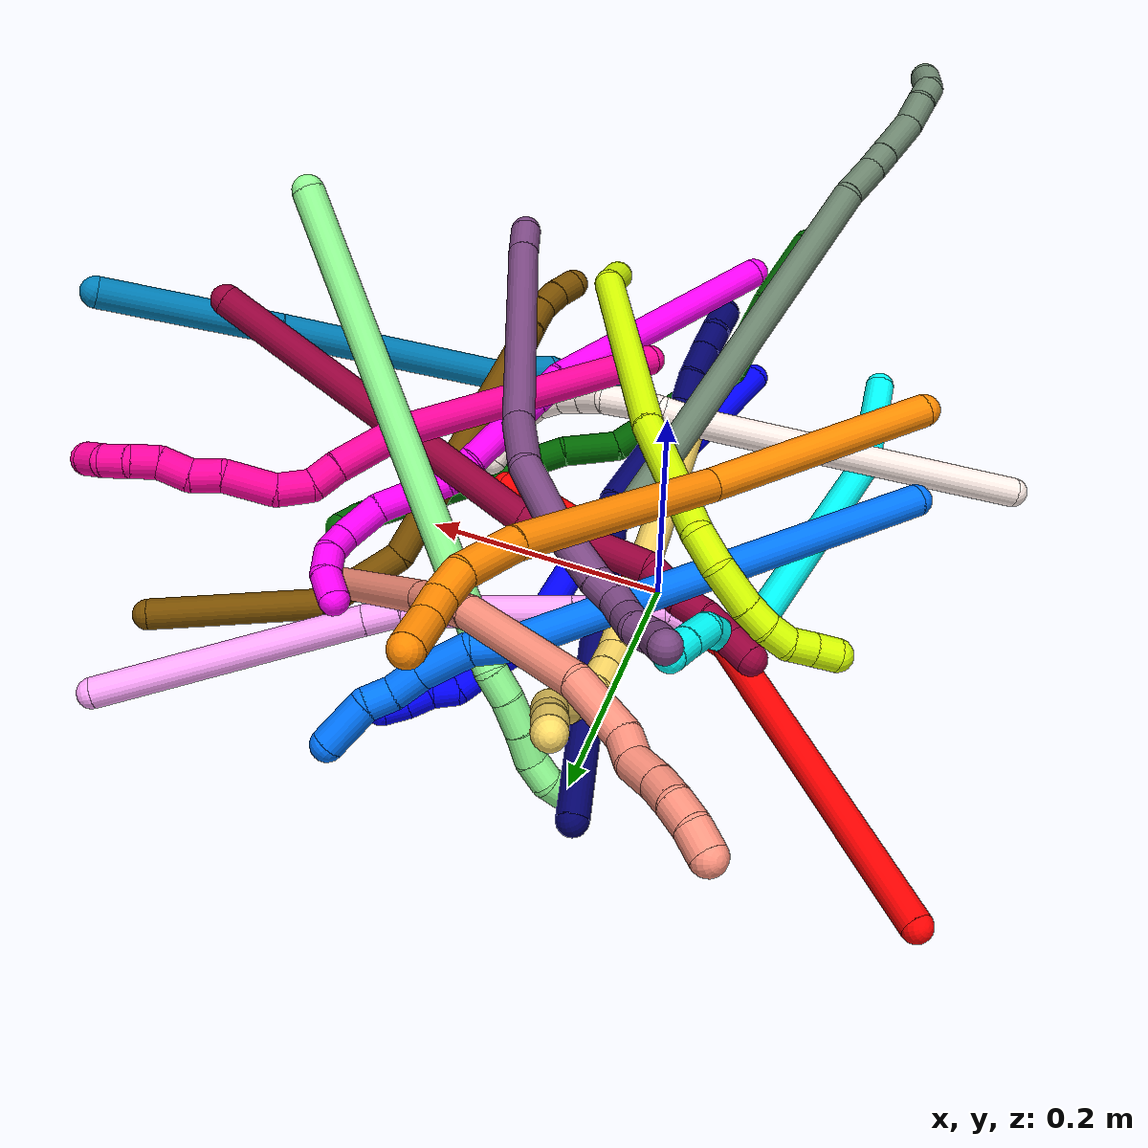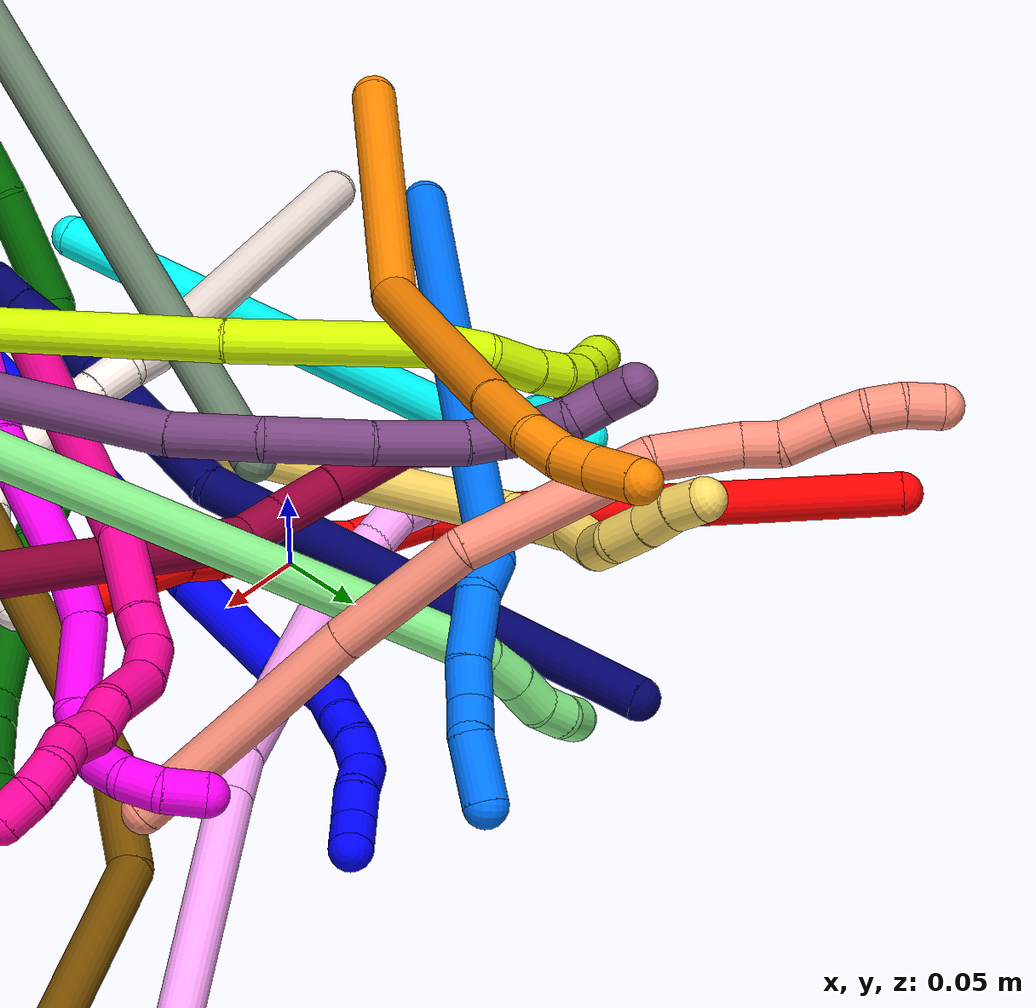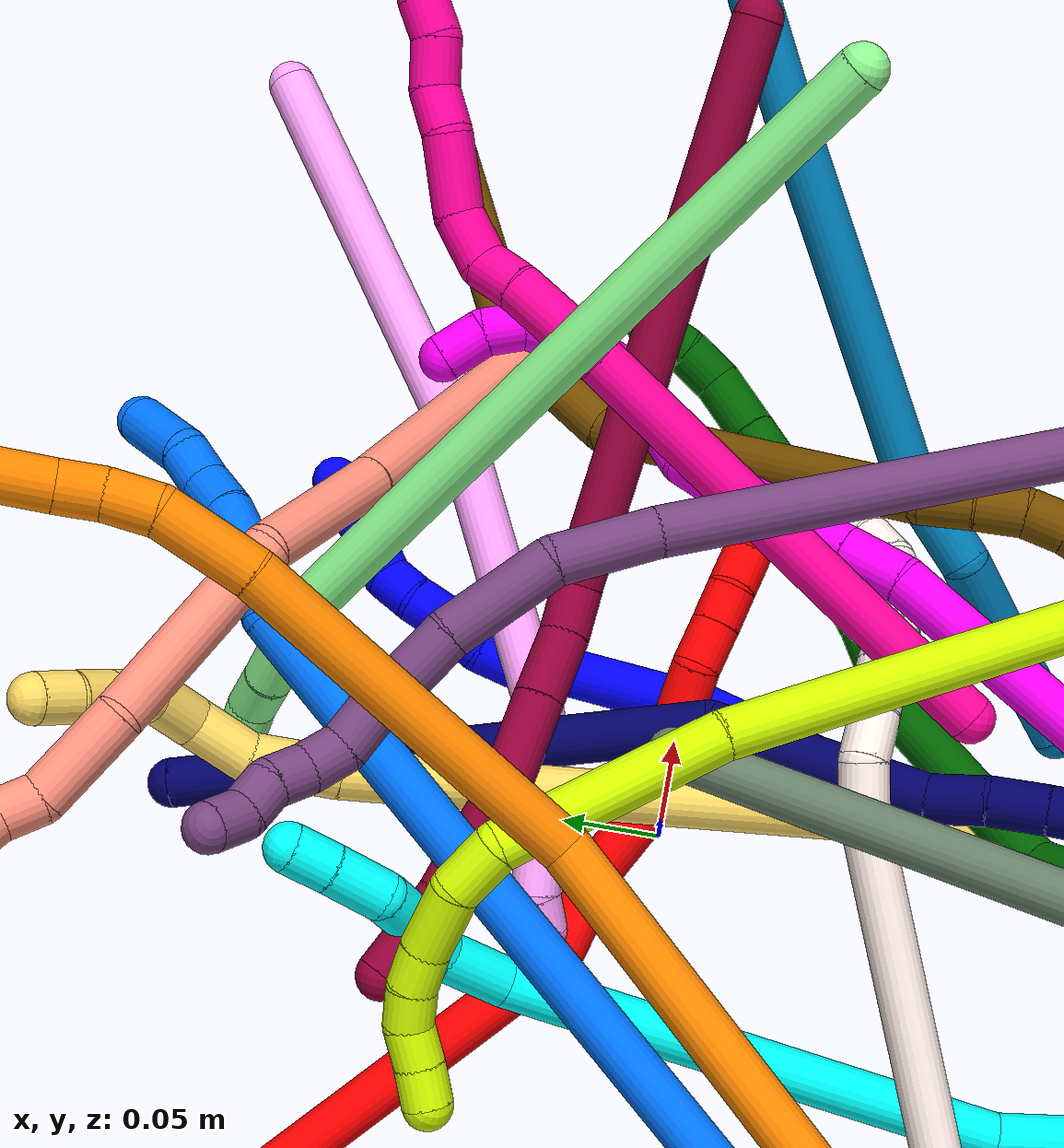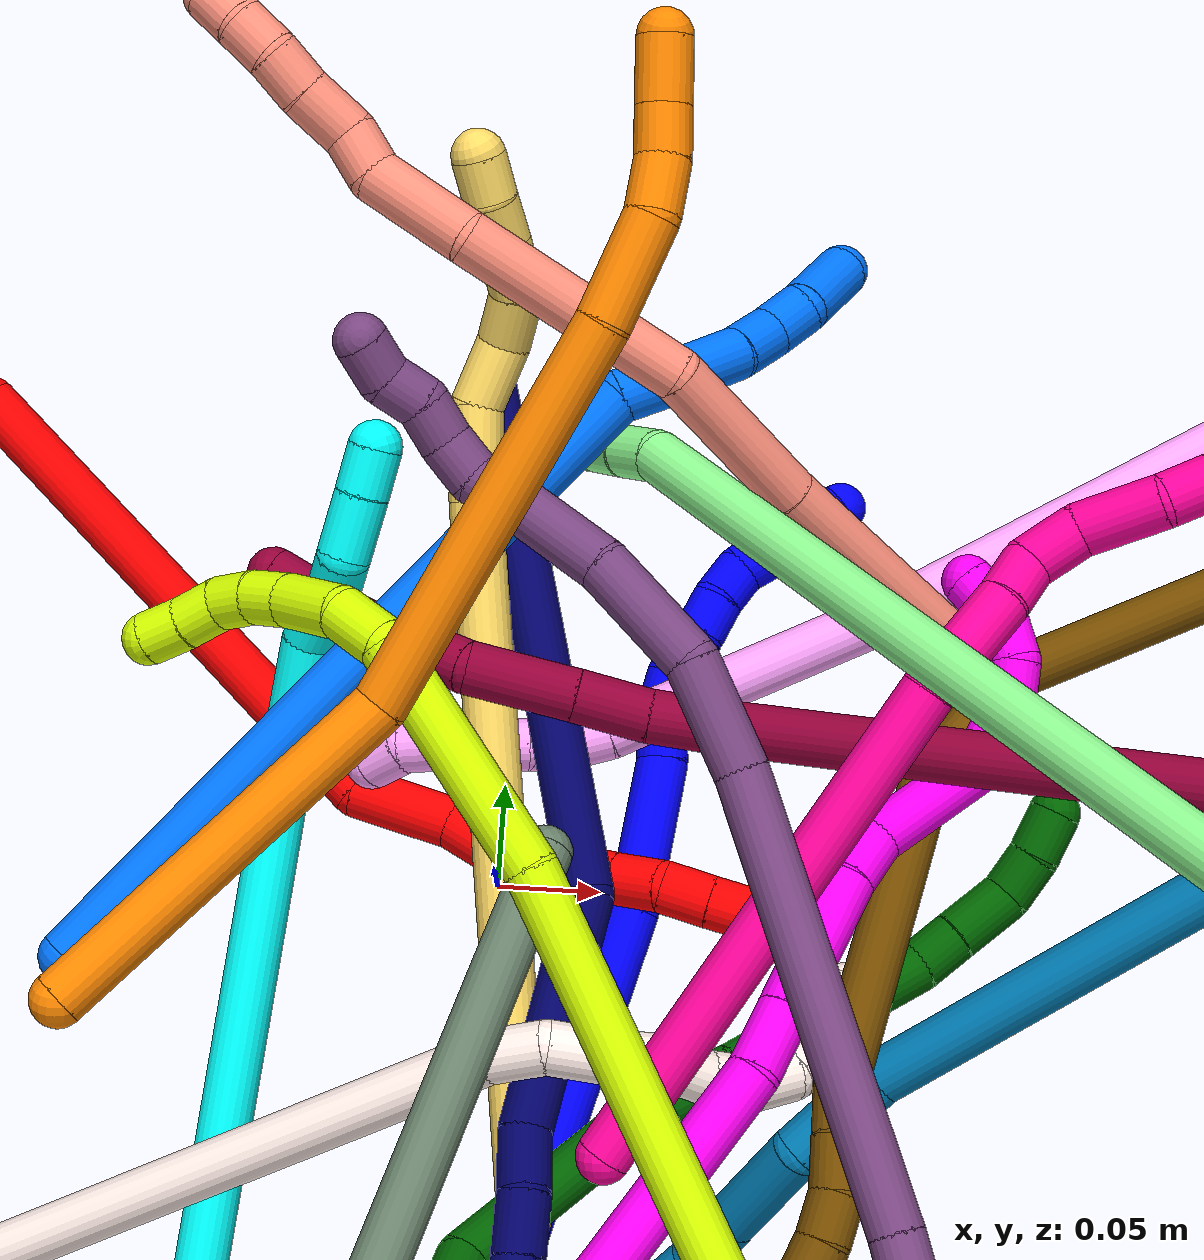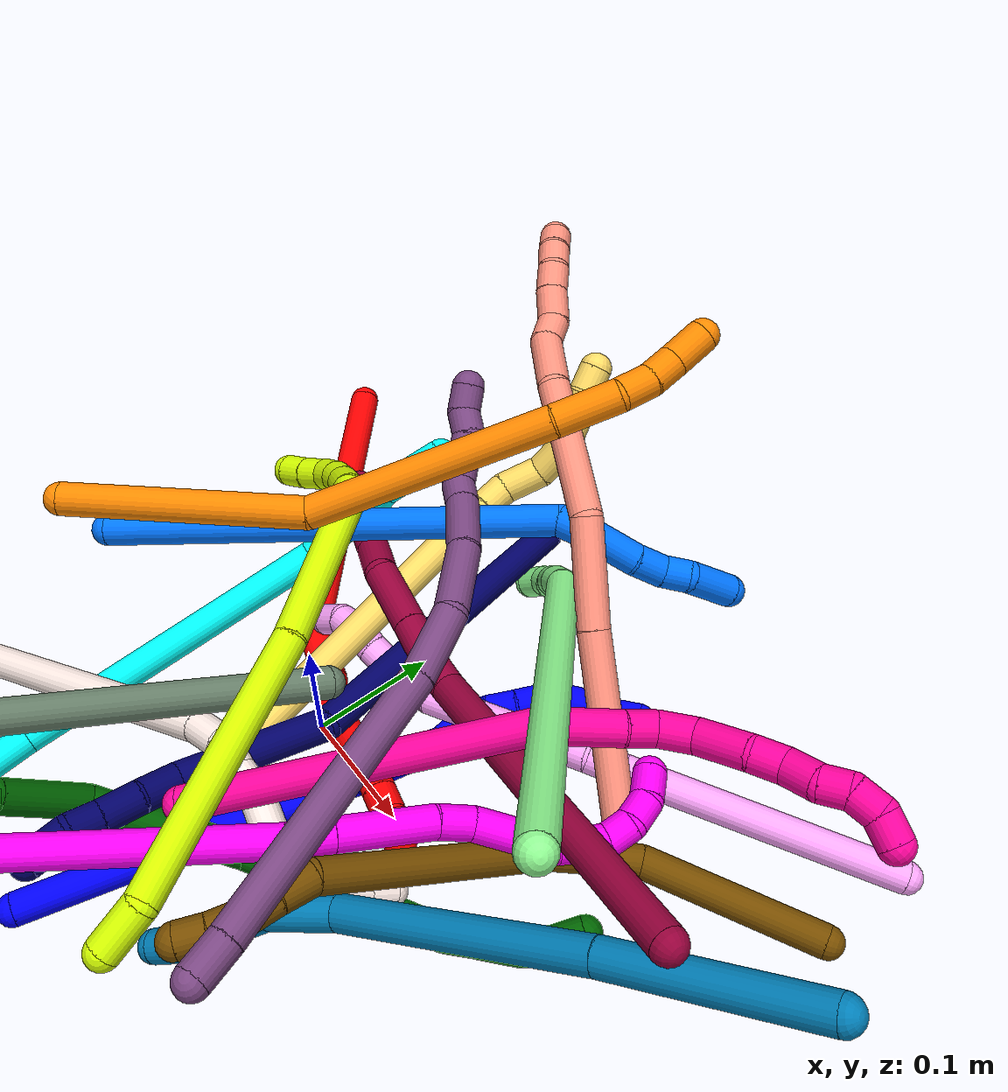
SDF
<sdf version="1.7">
 <world name="default">
  <plugin name="TubeGeneratorPlugin" filename="libtube_generator_plugin.so"/>
  <model name="photoneo_s_sensor">
   <static>1</static>
   <pose>0 0 2 1.57079 1.57079 3.14159</pose>
   <link name="link">
    <inertial><mass>0.1</mass></inertial>
    <sensor name="sensor" type="depth">
     <update_rate>30</update_rate>
     <camera>
      <horizontal_fov>1.22</horizontal_fov>
      <image><width>1920</width><height>1200</height><format>B8G8R8</format></image>
      <clip><near>0.1</near><far>4</far></clip>
      <depth_camera><output>points</output></depth_camera>
     </camera>
     <plugin name="camera_plugin" filename="libgazebo_ros_depth_camera.so">
      <baseline>0.2</baseline>
      <alwaysOn>1</alwaysOn>
      <updateRate>0.0</updateRate>
      <cameraName>camera_ir</cameraName>
      <imageTopicName>/camera/color/image_raw</imageTopicName>
      <cameraInfoTopicName>/camera/color/camera_info</cameraInfoTopicName>
      <depthImageTopicName>/camera/depth/image_raw</depthImageTopicName>
      <depthImageCameraInfoTopicName>/camera/depth/camera_info</depthImageCameraInfoTopicName>
      <pointCloudTopicName>/camera/depth/points</pointCloudTopicName>
      <frameName>fr_optical</frameName>
      <pointCloudCutoff>0.1</pointCloudCutoff>
      <pointCloudCutoffMax>2.0</pointCloudCutoffMax>
      <distortionK1>0</distortionK1>
      <distortionK2>0</distortionK2>
      <distortionK3>0</distortionK3>
      <distortionT1>0</distortionT1>
      <distortionT2>0</distortionT2>
      <CxPrime>0</CxPrime>
      <Cx>0</Cx>
      <Cy>0</Cy>
      <focalLength>0</focalLength>
      <hackBaseline>0</hackBaseline>
     </plugin>
    </sensor>
   </link>
  </model>
  <gravity>0 0 -9.8</gravity>
  <magnetic_field>6e-06 2.3e-05 -4.2e-05</magnetic_field>
  <atmosphere type="adiabatic"/>
  <physics name="default_physics" default="0" type="ode">
   <max_step_size>0.003</max_step_size>
   <real_time_factor>1</real_time_factor>
   <real_time_update_rate>1000</real_time_update_rate>
   <max_contacts>10000</max_contacts>
   <ode>
    <solver>
     <type>quick</type>
     <iters>100</iters>
     <sor>1.3</sor>
     <use_dynamic_moi_rescaling>0</use_dynamic_moi_rescaling>
    </solver>
    <constraints>
     <contact_max_correcting_vel>0</contact_max_correcting_vel>
     <contact_surface_layer>0.001</contact_surface_layer>
     <cfm>0</cfm>
     <erp>0.2</erp>
    </constraints>
   </ode>
  </physics>
  <scene><ambient>0.4 0.4 0.4 1</ambient><background>0.7 0.7 0.7 1</background><shadows>0</shadows></scene>
  <audio><device>default</device></audio>
  <spherical_coordinates>
   <surface_model>EARTH_WGS84</surface_model>
   <latitude_deg>0</latitude_deg>
   <longitude_deg>0</longitude_deg>
   <elevation>0</elevation>
   <heading_deg>0</heading_deg>
  </spherical_coordinates>
  <model name="bin">
   <static>1</static>
   <link name="bottom">
    <collision name="collision-bottom">
     <pose>0 0 -0.01 0 -0 0</pose>
     <geometry><box><size>0.8 0.6 0.02</size></box></geometry>
     <surface>
      <friction><ode><mu>100</mu><mu2>100</mu2></ode></friction>
      <contact><collide_bitmask>65535</collide_bitmask></contact>
     </surface>
    </collision>
   </link>
   <link name="west_wall">
    <collision name="collision-west_wall">
     <pose>-0.41 0 0.1 0 -0 0</pose>
     <geometry><box><size>0.02 0.6 0.2</size></box></geometry>
     <surface>
      <friction><ode><mu>100</mu><mu2>100</mu2></ode></friction>
      <contact><collide_bitmask>65535</collide_bitmask></contact>
     </surface>
    </collision>
   </link>
   <link name="east_wall">
    <collision name="collision-east_wall">
     <pose>0.41 0 0.1 0 -0 0</pose>
     <geometry><box><size>0.02 0.6 0.2</size></box></geometry>
     <surface>
      <friction><ode><mu>100</mu><mu2>100</mu2></ode></friction>
      <contact><collide_bitmask>65535</collide_bitmask></contact>
     </surface>
    </collision>
   </link>
   <link name="south_wall">
    <collision name="collision-south_wall">
     <pose>0 -0.31 0.1 0 -0 0</pose>
     <geometry><box><size>0.8 0.02 0.2</size></box></geometry>
     <surface>
      <friction><ode><mu>100</mu><mu2>100</mu2></ode></friction>
      <contact><collide_bitmask>65535</collide_bitmask></contact>
     </surface>
    </collision>
   </link>
   <link name="north_wall">
    <collision name="collision-north_wall">
     <pose>0 0.31 0.1 0 -0 0</pose>
     <geometry><box><size>0.8 0.02 0.2</size></box></geometry>
     <surface>
      <friction><ode><mu>100</mu><mu2>100</mu2></ode></friction>
      <contact><collide_bitmask>65535</collide_bitmask></contact>
     </surface>
    </collision>
   </link>
  </model>
  <model name="1">
   <static>0</static>
   <link name="1">
    <collision name="collision-cylinder-e_1_1_4">
     <pose>0.044026 0.105934 0.05769 -1.07212 0.349961 -0.209288</pose>
     <geometry><cylinder><radius>0.0125</radius><length>0.256816</length></cylinder></geometry>
     <surface>
      <friction><ode><mu>1.16</mu><mu2>1.16</mu2><slip1>0</slip1><slip2>0</slip2></ode></friction>
      <contact><ode><kp>1e+06</kp><kd>1</kd><max_vel>0</max_vel><min_depth>0.001</min_depth></ode></contact>
     </surface>
    </collision>
    <visual name="visual-cylinder-e_1_1_4">
     <pose>0.044026 0.105934 0.05769 -1.07212 0.349961 -0.209288</pose>
     <geometry><cylinder><radius>0.0125</radius><length>0.256816</length></cylinder></geometry>
     <material><ambient>0 0 1 1</ambient></material>
    </visual>
    <collision name="collision-cylinder-e_2_4_5">
     <pose>0.102269 0.246281 0.125098 -1.2956 0.378434 -0.287841</pose>
     <geometry><cylinder><radius>0.0125</radius><length>0.076962</length></cylinder></geometry>
     <surface>
      <friction><ode><mu>1.16</mu><mu2>1.16</mu2><slip1>0</slip1><slip2>0</slip2></ode></friction>
      <contact><ode><kp>1e+06</kp><kd>1</kd><max_vel>0</max_vel><min_depth>0.001</min_depth></ode></contact>
     </surface>
    </collision>
    <visual name="visual-cylinder-e_2_4_5">
     <pose>0.102269 0.246281 0.125098 -1.2956 0.378434 -0.287841</pose>
     <geometry><cylinder><radius>0.0125</radius><length>0.076962</length></cylinder></geometry>
     <material><ambient>0 0 1 1</ambient></material>
    </visual>
    <collision name="collision-cylinder-e_3_5_6">
     <pose>0.116732 0.290933 0.137765 -1.29019 0.023012 -0.017316</pose>
     <geometry><cylinder><radius>0.0125</radius><length>0.021317</length></cylinder></geometry>
     <surface>
      <friction><ode><mu>1.16</mu><mu2>1.16</mu2><slip1>0</slip1><slip2>0</slip2></ode></friction>
      <contact><ode><kp>1e+06</kp><kd>1</kd><max_vel>0</max_vel><min_depth>0.001</min_depth></ode></contact>
     </surface>
    </collision>
    <visual name="visual-cylinder-e_3_5_6">
     <pose>0.116732 0.290933 0.137765 -1.29019 0.023012 -0.017316</pose>
     <geometry><cylinder><radius>0.0125</radius><length>0.021317</length></cylinder></geometry>
     <material><ambient>0 0 1 1</ambient></material>
    </visual>
    <collision name="collision-cylinder-e_4_6_7">
     <pose>0.119586 0.31037 0.146283 -1.02653 0.238033 -0.134602</pose>
     <geometry><cylinder><radius>0.0125</radius><length>0.022126</length></cylinder></geometry>
     <surface>
      <friction><ode><mu>1.16</mu><mu2>1.16</mu2><slip1>0</slip1><slip2>0</slip2></ode></friction>
      <contact><ode><kp>1e+06</kp><kd>1</kd><max_vel>0</max_vel><min_depth>0.001</min_depth></ode></contact>
     </surface>
    </collision>
    <visual name="visual-cylinder-e_4_6_7">
     <pose>0.119586 0.31037 0.146283 -1.02653 0.238033 -0.134602</pose>
     <geometry><cylinder><radius>0.0125</radius><length>0.022126</length></cylinder></geometry>
     <material><ambient>0 0 1 1</ambient></material>
    </visual>
    <collision name="collision-cylinder-e_5_7_8">
     <pose>0.126632 0.326802 0.159311 -0.769912 0.403561 -0.165389</pose>
     <geometry><cylinder><radius>0.0125</radius><length>0.022601</length></cylinder></geometry>
     <surface>
      <friction><ode><mu>1.16</mu><mu2>1.16</mu2><slip1>0</slip1><slip2>0</slip2></ode></friction>
      <contact><ode><kp>1e+06</kp><kd>1</kd><max_vel>0</max_vel><min_depth>0.001</min_depth></ode></contact>
     </surface>
    </collision>
    <visual name="visual-cylinder-e_5_7_8">
     <pose>0.126632 0.326802 0.159311 -0.769912 0.403561 -0.165389</pose>
     <geometry><cylinder><radius>0.0125</radius><length>0.022601</length></cylinder></geometry>
     <material><ambient>0 0 1 1</ambient></material>
    </visual>
    <collision name="collision-cylinder-e_6_8_9">
     <pose>0.135444 0.341338 0.172107 -0.939927 0.450541 -0.231747</pose>
     <geometry><cylinder><radius>0.0125</radius><length>0.02009</length></cylinder></geometry>
     <surface>
      <friction><ode><mu>1.16</mu><mu2>1.16</mu2><slip1>0</slip1><slip2>0</slip2></ode></friction>
      <contact><ode><kp>1e+06</kp><kd>1</kd><max_vel>0</max_vel><min_depth>0.001</min_depth></ode></contact>
     </surface>
    </collision>
    <visual name="visual-cylinder-e_6_8_9">
     <pose>0.135444 0.341338 0.172107 -0.939927 0.450541 -0.231747</pose>
     <geometry><cylinder><radius>0.0125</radius><length>0.02009</length></cylinder></geometry>
     <material><ambient>0 0 1 1</ambient></material>
    </visual>
    <collision name="collision-cylinder-e_7_9_10">
     <pose>0.146221 0.35491 0.181914 -0.951097 0.693509 -0.367963</pose>
     <geometry><cylinder><radius>0.0125</radius><length>0.020032</length></cylinder></geometry>
     <surface>
      <friction><ode><mu>1.16</mu><mu2>1.16</mu2><slip1>0</slip1><slip2>0</slip2></ode></friction>
      <contact><ode><kp>1e+06</kp><kd>1</kd><max_vel>0</max_vel><min_depth>0.001</min_depth></ode></contact>
     </surface>
    </collision>
    <visual name="visual-cylinder-e_7_9_10">
     <pose>0.146221 0.35491 0.181914 -0.951097 0.693509 -0.367963</pose>
     <geometry><cylinder><radius>0.0125</radius><length>0.020032</length></cylinder></geometry>
     <material><ambient>0 0 1 1</ambient></material>
    </visual>
    <collision name="collision-cylinder-e_8_10_11">
     <pose>0.158653 0.363615 0.19401 -0.309266 0.64576 -0.104215</pose>
     <geometry><cylinder><radius>0.0125</radius><length>0.020038</length></cylinder></geometry>
     <surface>
      <friction><ode><mu>1.16</mu><mu2>1.16</mu2><slip1>0</slip1><slip2>0</slip2></ode></friction>
      <contact><ode><kp>1e+06</kp><kd>1</kd><max_vel>0</max_vel><min_depth>0.001</min_depth></ode></contact>
     </surface>
    </collision>
    <visual name="visual-cylinder-e_8_10_11">
     <pose>0.158653 0.363615 0.19401 -0.309266 0.64576 -0.104215</pose>
     <geometry><cylinder><radius>0.0125</radius><length>0.020038</length></cylinder></geometry>
     <material><ambient>0 0 1 1</ambient></material>
    </visual>
    <collision name="collision-cylinder-e_9_11_12">
     <pose>0.172929 0.36935 0.206242 -0.621224 0.96855 -0.334575</pose>
     <geometry><cylinder><radius>0.0125</radius><length>0.020015</length></cylinder></geometry>
     <surface>
      <friction><ode><mu>1.16</mu><mu2>1.16</mu2><slip1>0</slip1><slip2>0</slip2></ode></friction>
      <contact><ode><kp>1e+06</kp><kd>1</kd><max_vel>0</max_vel><min_depth>0.001</min_depth></ode></contact>
     </surface>
    </collision>
    <visual name="visual-cylinder-e_9_11_12">
     <pose>0.172929 0.36935 0.206242 -0.621224 0.96855 -0.334575</pose>
     <geometry><cylinder><radius>0.0125</radius><length>0.020015</length></cylinder></geometry>
     <material><ambient>0 0 1 1</ambient></material>
    </visual>
    <collision name="collision-cylinder-e_10_12_2">
     <pose>0.187566 0.376164 0.217696 -0.474324 0.693052 -0.174121</pose>
     <geometry><cylinder><radius>0.0125</radius><length>0.020003</length></cylinder></geometry>
     <surface>
      <friction><ode><mu>1.16</mu><mu2>1.16</mu2><slip1>0</slip1><slip2>0</slip2></ode></friction>
      <contact><ode><kp>1e+06</kp><kd>1</kd><max_vel>0</max_vel><min_depth>0.001</min_depth></ode></contact>
     </surface>
    </collision>
    <visual name="visual-cylinder-e_10_12_2">
     <pose>0.187566 0.376164 0.217696 -0.474324 0.693052 -0.174121</pose>
     <geometry><cylinder><radius>0.0125</radius><length>0.020003</length></cylinder></geometry>
     <material><ambient>0 0 1 1</ambient></material>
    </visual>
    <collision name="collision-sphere-2">
     <pose>0.193956 0.379678 0.224541 0 -0 0</pose>
     <geometry><sphere><radius>0.0125</radius></sphere></geometry>
     <surface>
      <friction><ode><mu>1.16</mu><mu2>1.16</mu2><slip1>0</slip1><slip2>0</slip2></ode></friction>
      <contact><ode><kp>1e+06</kp><kd>1</kd><max_vel>0</max_vel><min_depth>0.001</min_depth></ode></contact>
     </surface>
    </collision>
    <visual name="visual-sphere-2">
     <pose>0.193956 0.379678 0.224541 0 -0 0</pose>
     <geometry><sphere><radius>0.0125</radius></sphere></geometry>
     <material><ambient>0 0 1 1</ambient></material>
    </visual>
    <collision name="collision-sphere-12">
     <pose>0.181176 0.37265 0.210852 0 -0 0</pose>
     <geometry><sphere><radius>0.0125</radius></sphere></geometry>
     <surface>
      <friction><ode><mu>1.16</mu><mu2>1.16</mu2><slip1>0</slip1><slip2>0</slip2></ode></friction>
      <contact><ode><kp>1e+06</kp><kd>1</kd><max_vel>0</max_vel><min_depth>0.001</min_depth></ode></contact>
     </surface>
    </collision>
    <visual name="visual-sphere-12">
     <pose>0.181176 0.37265 0.210852 0 -0 0</pose>
     <geometry><sphere><radius>0.0125</radius></sphere></geometry>
     <material><ambient>0 0 1 1</ambient></material>
    </visual>
    <collision name="collision-sphere-11">
     <pose>0.164682 0.366051 0.201632 0 -0 0</pose>
     <geometry><sphere><radius>0.0125</radius></sphere></geometry>
     <surface>
      <friction><ode><mu>1.16</mu><mu2>1.16</mu2><slip1>0</slip1><slip2>0</slip2></ode></friction>
      <contact><ode><kp>1e+06</kp><kd>1</kd><max_vel>0</max_vel><min_depth>0.001</min_depth></ode></contact>
     </surface>
    </collision>
    <visual name="visual-sphere-11">
     <pose>0.164682 0.366051 0.201632 0 -0 0</pose>
     <geometry><sphere><radius>0.0125</radius></sphere></geometry>
     <material><ambient>0 0 1 1</ambient></material>
    </visual>
    <collision name="collision-sphere-10">
     <pose>0.152623 0.36118 0.186387 0 -0 0</pose>
     <geometry><sphere><radius>0.0125</radius></sphere></geometry>
     <surface>
      <friction><ode><mu>1.16</mu><mu2>1.16</mu2><slip1>0</slip1><slip2>0</slip2></ode></friction>
      <contact><ode><kp>1e+06</kp><kd>1</kd><max_vel>0</max_vel><min_depth>0.001</min_depth></ode></contact>
     </surface>
    </collision>
    <visual name="visual-sphere-10">
     <pose>0.152623 0.36118 0.186387 0 -0 0</pose>
     <geometry><sphere><radius>0.0125</radius></sphere></geometry>
     <material><ambient>0 0 1 1</ambient></material>
    </visual>
    <collision name="collision-sphere-9">
     <pose>0.139818 0.34864 0.177441 0 -0 0</pose>
     <geometry><sphere><radius>0.0125</radius></sphere></geometry>
     <surface>
      <friction><ode><mu>1.16</mu><mu2>1.16</mu2><slip1>0</slip1><slip2>0</slip2></ode></friction>
      <contact><ode><kp>1e+06</kp><kd>1</kd><max_vel>0</max_vel><min_depth>0.001</min_depth></ode></contact>
     </surface>
    </collision>
    <visual name="visual-sphere-9">
     <pose>0.139818 0.34864 0.177441 0 -0 0</pose>
     <geometry><sphere><radius>0.0125</radius></sphere></geometry>
     <material><ambient>0 0 1 1</ambient></material>
    </visual>
    <collision name="collision-sphere-4">
     <pose>0.088052 0.211869 0.115381 0 -0 0</pose>
     <geometry><sphere><radius>0.0125</radius></sphere></geometry>
     <surface>
      <friction><ode><mu>1.16</mu><mu2>1.16</mu2><slip1>0</slip1><slip2>0</slip2></ode></friction>
      <contact><ode><kp>1e+06</kp><kd>1</kd><max_vel>0</max_vel><min_depth>0.001</min_depth></ode></contact>
     </surface>
    </collision>
    <visual name="visual-sphere-4">
     <pose>0.088052 0.211869 0.115381 0 -0 0</pose>
     <geometry><sphere><radius>0.0125</radius></sphere></geometry>
     <material><ambient>0 0 1 1</ambient></material>
    </visual>
    <collision name="collision-sphere-1">
     <geometry><sphere><radius>0.0125</radius></sphere></geometry>
     <surface>
      <friction><ode><mu>1.16</mu><mu2>1.16</mu2><slip1>0</slip1><slip2>0</slip2></ode></friction>
      <contact><ode><kp>1e+06</kp><kd>1</kd><max_vel>0</max_vel><min_depth>0.001</min_depth></ode></contact>
     </surface>
    </collision>
    <visual name="visual-sphere-1">
     <geometry><sphere><radius>0.0125</radius></sphere></geometry>
     <material><ambient>0 0 1 1</ambient></material>
    </visual>
    <collision name="collision-sphere-8">
     <pose>0.13107 0.334036 0.166773 0 -0 0</pose>
     <geometry><sphere><radius>0.0125</radius></sphere></geometry>
     <surface>
      <friction><ode><mu>1.16</mu><mu2>1.16</mu2><slip1>0</slip1><slip2>0</slip2></ode></friction>
      <contact><ode><kp>1e+06</kp><kd>1</kd><max_vel>0</max_vel><min_depth>0.001</min_depth></ode></contact>
     </surface>
    </collision>
    <visual name="visual-sphere-8">
     <pose>0.13107 0.334036 0.166773 0 -0 0</pose>
     <geometry><sphere><radius>0.0125</radius></sphere></geometry>
     <material><ambient>0 0 1 1</ambient></material>
    </visual>
    <collision name="collision-sphere-5">
     <pose>0.116487 0.280694 0.134814 0 -0 0</pose>
     <geometry><sphere><radius>0.0125</radius></sphere></geometry>
     <surface>
      <friction><ode><mu>1.16</mu><mu2>1.16</mu2><slip1>0</slip1><slip2>0</slip2></ode></friction>
      <contact><ode><kp>1e+06</kp><kd>1</kd><max_vel>0</max_vel><min_depth>0.001</min_depth></ode></contact>
     </surface>
    </collision>
    <visual name="visual-sphere-5">
     <pose>0.116487 0.280694 0.134814 0 -0 0</pose>
     <geometry><sphere><radius>0.0125</radius></sphere></geometry>
     <material><ambient>0 0 1 1</ambient></material>
    </visual>
    <collision name="collision-sphere-6">
     <pose>0.116977 0.301172 0.140716 0 -0 0</pose>
     <geometry><sphere><radius>0.0125</radius></sphere></geometry>
     <surface>
      <friction><ode><mu>1.16</mu><mu2>1.16</mu2><slip1>0</slip1><slip2>0</slip2></ode></friction>
      <contact><ode><kp>1e+06</kp><kd>1</kd><max_vel>0</max_vel><min_depth>0.001</min_depth></ode></contact>
     </surface>
    </collision>
    <visual name="visual-sphere-6">
     <pose>0.116977 0.301172 0.140716 0 -0 0</pose>
     <geometry><sphere><radius>0.0125</radius></sphere></geometry>
     <material><ambient>0 0 1 1</ambient></material>
    </visual>
    <collision name="collision-sphere-7">
     <pose>0.122194 0.319567 0.15185 0 -0 0</pose>
     <geometry><sphere><radius>0.0125</radius></sphere></geometry>
     <surface>
      <friction><ode><mu>1.16</mu><mu2>1.16</mu2><slip1>0</slip1><slip2>0</slip2></ode></friction>
      <contact><ode><kp>1e+06</kp><kd>1</kd><max_vel>0</max_vel><min_depth>0.001</min_depth></ode></contact>
     </surface>
    </collision>
    <visual name="visual-sphere-7">
     <pose>0.122194 0.319567 0.15185 0 -0 0</pose>
     <geometry><sphere><radius>0.0125</radius></sphere></geometry>
     <material><ambient>0 0 1 1</ambient></material>
    </visual>
    <inertial>
     <pose>0.086432 0.20557 0.107379 0 -0 0</pose>
     <mass>0.5</mass>
     <inertia>
      <ixx>0.001078</ixx>
      <ixy>0</ixy>
      <ixz>0</ixz>
      <iyy>0.000517</iyy>
      <iyz>0</iyz>
      <izz>-0.001708</izz>
     </inertia>
    </inertial>
   </link>
   <pose>-0.000691 -0.259199 0.011489 -0.051712 0.800896 0.296354</pose>
  </model>
  <model name="2">
   <static>0</static>
   <link name="2">
    <collision name="collision-cylinder-e_1_1_4">
     <pose>0.047679 -0.09233 -0.086904 2.32593 0.359675 0.796586</pose>
     <geometry><cylinder><radius>0.0125</radius><length>0.270928</length></cylinder></geometry>
     <surface>
      <friction><ode><mu>1.16</mu><mu2>1.16</mu2><slip1>0</slip1><slip2>0</slip2></ode></friction>
      <contact><ode><kp>1e+06</kp><kd>1</kd><max_vel>0</max_vel><min_depth>0.001</min_depth></ode></contact>
     </surface>
    </collision>
    <visual name="visual-cylinder-e_1_1_4">
     <pose>0.047679 -0.09233 -0.086904 2.32593 0.359675 0.796586</pose>
     <geometry><cylinder><radius>0.0125</radius><length>0.270928</length></cylinder></geometry>
     <material><ambient>1 0 0 1</ambient></material>
    </visual>
    <collision name="collision-cylinder-e_2_4_5">
     <pose>0.112614 -0.193073 -0.190078 2.6644 0.755584 2.0419</pose>
     <geometry><cylinder><radius>0.0125</radius><length>0.050329</length></cylinder></geometry>
     <surface>
      <friction><ode><mu>1.16</mu><mu2>1.16</mu2><slip1>0</slip1><slip2>0</slip2></ode></friction>
      <contact><ode><kp>1e+06</kp><kd>1</kd><max_vel>0</max_vel><min_depth>0.001</min_depth></ode></contact>
     </surface>
    </collision>
    <visual name="visual-cylinder-e_2_4_5">
     <pose>0.112614 -0.193073 -0.190078 2.6644 0.755584 2.0419</pose>
     <geometry><cylinder><radius>0.0125</radius><length>0.050329</length></cylinder></geometry>
     <material><ambient>1 0 0 1</ambient></material>
    </visual>
    <collision name="collision-cylinder-e_3_5_6">
     <pose>0.142326 -0.212923 -0.216481 2.29581 0.683929 1.33835</pose>
     <geometry><cylinder><radius>0.0125</radius><length>0.039429</length></cylinder></geometry>
     <surface>
      <friction><ode><mu>1.16</mu><mu2>1.16</mu2><slip1>0</slip1><slip2>0</slip2></ode></friction>
      <contact><ode><kp>1e+06</kp><kd>1</kd><max_vel>0</max_vel><min_depth>0.001</min_depth></ode></contact>
     </surface>
    </collision>
    <visual name="visual-cylinder-e_3_5_6">
     <pose>0.142326 -0.212923 -0.216481 2.29581 0.683929 1.33835</pose>
     <geometry><cylinder><radius>0.0125</radius><length>0.039429</length></cylinder></geometry>
     <material><ambient>1 0 0 1</ambient></material>
    </visual>
    <collision name="collision-cylinder-e_4_6_7">
     <pose>0.165717 -0.227685 -0.231934 2.58296 1.04996 2.222</pose>
     <geometry><cylinder><radius>0.0125</radius><length>0.025211</length></cylinder></geometry>
     <surface>
      <friction><ode><mu>1.16</mu><mu2>1.16</mu2><slip1>0</slip1><slip2>0</slip2></ode></friction>
      <contact><ode><kp>1e+06</kp><kd>1</kd><max_vel>0</max_vel><min_depth>0.001</min_depth></ode></contact>
     </surface>
    </collision>
    <visual name="visual-cylinder-e_4_6_7">
     <pose>0.165717 -0.227685 -0.231934 2.58296 1.04996 2.222</pose>
     <geometry><cylinder><radius>0.0125</radius><length>0.025211</length></cylinder></geometry>
     <material><ambient>1 0 0 1</ambient></material>
    </visual>
    <collision name="collision-cylinder-e_5_7_8">
     <pose>0.187007 -0.234868 -0.243206 2.56662 0.97017 2.11915</pose>
     <geometry><cylinder><radius>0.0125</radius><length>0.025105</length></cylinder></geometry>
     <surface>
      <friction><ode><mu>1.16</mu><mu2>1.16</mu2><slip1>0</slip1><slip2>0</slip2></ode></friction>
      <contact><ode><kp>1e+06</kp><kd>1</kd><max_vel>0</max_vel><min_depth>0.001</min_depth></ode></contact>
     </surface>
    </collision>
    <visual name="visual-cylinder-e_5_7_8">
     <pose>0.187007 -0.234868 -0.243206 2.56662 0.97017 2.11915</pose>
     <geometry><cylinder><radius>0.0125</radius><length>0.025105</length></cylinder></geometry>
     <material><ambient>1 0 0 1</ambient></material>
    </visual>
    <collision name="collision-cylinder-e_6_8_9">
     <pose>0.208031 -0.242859 -0.253552 2.38653 1.05627 1.94764</pose>
     <geometry><cylinder><radius>0.0125</radius><length>0.024512</length></cylinder></geometry>
     <surface>
      <friction><ode><mu>1.16</mu><mu2>1.16</mu2><slip1>0</slip1><slip2>0</slip2></ode></friction>
      <contact><ode><kp>1e+06</kp><kd>1</kd><max_vel>0</max_vel><min_depth>0.001</min_depth></ode></contact>
     </surface>
    </collision>
    <visual name="visual-cylinder-e_6_8_9">
     <pose>0.208031 -0.242859 -0.253552 2.38653 1.05627 1.94764</pose>
     <geometry><cylinder><radius>0.0125</radius><length>0.024512</length></cylinder></geometry>
     <material><ambient>1 0 0 1</ambient></material>
    </visual>
    <collision name="collision-cylinder-e_7_9_10">
     <pose>0.226522 -0.250665 -0.265762 2.70253 0.735863 2.09218</pose>
     <geometry><cylinder><radius>0.0125</radius><length>0.023305</length></cylinder></geometry>
     <surface>
      <friction><ode><mu>1.16</mu><mu2>1.16</mu2><slip1>0</slip1><slip2>0</slip2></ode></friction>
      <contact><ode><kp>1e+06</kp><kd>1</kd><max_vel>0</max_vel><min_depth>0.001</min_depth></ode></contact>
     </surface>
    </collision>
    <visual name="visual-cylinder-e_7_9_10">
     <pose>0.226522 -0.250665 -0.265762 2.70253 0.735863 2.09218</pose>
     <geometry><cylinder><radius>0.0125</radius><length>0.023305</length></cylinder></geometry>
     <material><ambient>1 0 0 1</ambient></material>
    </visual>
    <collision name="collision-cylinder-e_8_10_11">
     <pose>0.24123 -0.257346 -0.280517 2.73222 0.738773 2.15722</pose>
     <geometry><cylinder><radius>0.0125</radius><length>0.020454</length></cylinder></geometry>
     <surface>
      <friction><ode><mu>1.16</mu><mu2>1.16</mu2><slip1>0</slip1><slip2>0</slip2></ode></friction>
      <contact><ode><kp>1e+06</kp><kd>1</kd><max_vel>0</max_vel><min_depth>0.001</min_depth></ode></contact>
     </surface>
    </collision>
    <visual name="visual-cylinder-e_8_10_11">
     <pose>0.24123 -0.257346 -0.280517 2.73222 0.738773 2.15722</pose>
     <geometry><cylinder><radius>0.0125</radius><length>0.020454</length></cylinder></geometry>
     <material><ambient>1 0 0 1</ambient></material>
    </visual>
    <collision name="collision-cylinder-e_9_11_2">
     <pose>0.253608 -0.262601 -0.29595 2.88318 0.558485 2.29066</pose>
     <geometry><cylinder><radius>0.0125</radius><length>0.020727</length></cylinder></geometry>
     <surface>
      <friction><ode><mu>1.16</mu><mu2>1.16</mu2><slip1>0</slip1><slip2>0</slip2></ode></friction>
      <contact><ode><kp>1e+06</kp><kd>1</kd><max_vel>0</max_vel><min_depth>0.001</min_depth></ode></contact>
     </surface>
    </collision>
    <visual name="visual-cylinder-e_9_11_2">
     <pose>0.253608 -0.262601 -0.29595 2.88318 0.558485 2.29066</pose>
     <geometry><cylinder><radius>0.0125</radius><length>0.020727</length></cylinder></geometry>
     <material><ambient>1 0 0 1</ambient></material>
    </visual>
    <collision name="collision-sphere-2">
     <pose>0.2591 -0.264847 -0.304447 0 -0 0</pose>
     <geometry><sphere><radius>0.0125</radius></sphere></geometry>
     <surface>
      <friction><ode><mu>1.16</mu><mu2>1.16</mu2><slip1>0</slip1><slip2>0</slip2></ode></friction>
      <contact><ode><kp>1e+06</kp><kd>1</kd><max_vel>0</max_vel><min_depth>0.001</min_depth></ode></contact>
     </surface>
    </collision>
    <visual name="visual-sphere-2">
     <pose>0.2591 -0.264847 -0.304447 0 -0 0</pose>
     <geometry><sphere><radius>0.0125</radius></sphere></geometry>
     <material><ambient>1 0 0 1</ambient></material>
    </visual>
    <collision name="collision-sphere-11">
     <pose>0.248117 -0.260355 -0.287453 0 -0 0</pose>
     <geometry><sphere><radius>0.0125</radius></sphere></geometry>
     <surface>
      <friction><ode><mu>1.16</mu><mu2>1.16</mu2><slip1>0</slip1><slip2>0</slip2></ode></friction>
      <contact><ode><kp>1e+06</kp><kd>1</kd><max_vel>0</max_vel><min_depth>0.001</min_depth></ode></contact>
     </surface>
    </collision>
    <visual name="visual-sphere-11">
     <pose>0.248117 -0.260355 -0.287453 0 -0 0</pose>
     <geometry><sphere><radius>0.0125</radius></sphere></geometry>
     <material><ambient>1 0 0 1</ambient></material>
    </visual>
    <collision name="collision-sphere-10">
     <pose>0.234343 -0.254336 -0.273581 0 -0 0</pose>
     <geometry><sphere><radius>0.0125</radius></sphere></geometry>
     <surface>
      <friction><ode><mu>1.16</mu><mu2>1.16</mu2><slip1>0</slip1><slip2>0</slip2></ode></friction>
      <contact><ode><kp>1e+06</kp><kd>1</kd><max_vel>0</max_vel><min_depth>0.001</min_depth></ode></contact>
     </surface>
    </collision>
    <visual name="visual-sphere-10">
     <pose>0.234343 -0.254336 -0.273581 0 -0 0</pose>
     <geometry><sphere><radius>0.0125</radius></sphere></geometry>
     <material><ambient>1 0 0 1</ambient></material>
    </visual>
    <collision name="collision-sphere-9">
     <pose>0.2187 -0.246993 -0.257944 0 -0 0</pose>
     <geometry><sphere><radius>0.0125</radius></sphere></geometry>
     <surface>
      <friction><ode><mu>1.16</mu><mu2>1.16</mu2><slip1>0</slip1><slip2>0</slip2></ode></friction>
      <contact><ode><kp>1e+06</kp><kd>1</kd><max_vel>0</max_vel><min_depth>0.001</min_depth></ode></contact>
     </surface>
    </collision>
    <visual name="visual-sphere-9">
     <pose>0.2187 -0.246993 -0.257944 0 -0 0</pose>
     <geometry><sphere><radius>0.0125</radius></sphere></geometry>
     <material><ambient>1 0 0 1</ambient></material>
    </visual>
    <collision name="collision-sphere-4">
     <pose>0.095359 -0.184661 -0.173808 0 -0 0</pose>
     <geometry><sphere><radius>0.0125</radius></sphere></geometry>
     <surface>
      <friction><ode><mu>1.16</mu><mu2>1.16</mu2><slip1>0</slip1><slip2>0</slip2></ode></friction>
      <contact><ode><kp>1e+06</kp><kd>1</kd><max_vel>0</max_vel><min_depth>0.001</min_depth></ode></contact>
     </surface>
    </collision>
    <visual name="visual-sphere-4">
     <pose>0.095359 -0.184661 -0.173808 0 -0 0</pose>
     <geometry><sphere><radius>0.0125</radius></sphere></geometry>
     <material><ambient>1 0 0 1</ambient></material>
    </visual>
    <collision name="collision-sphere-1">
     <geometry><sphere><radius>0.0125</radius></sphere></geometry>
     <surface>
      <friction><ode><mu>1.16</mu><mu2>1.16</mu2><slip1>0</slip1><slip2>0</slip2></ode></friction>
      <contact><ode><kp>1e+06</kp><kd>1</kd><max_vel>0</max_vel><min_depth>0.001</min_depth></ode></contact>
     </surface>
    </collision>
    <visual name="visual-sphere-1">
     <geometry><sphere><radius>0.0125</radius></sphere></geometry>
     <material><ambient>1 0 0 1</ambient></material>
    </visual>
    <collision name="collision-sphere-8">
     <pose>0.197362 -0.238726 -0.24916 0 -0 0</pose>
     <geometry><sphere><radius>0.0125</radius></sphere></geometry>
     <surface>
      <friction><ode><mu>1.16</mu><mu2>1.16</mu2><slip1>0</slip1><slip2>0</slip2></ode></friction>
      <contact><ode><kp>1e+06</kp><kd>1</kd><max_vel>0</max_vel><min_depth>0.001</min_depth></ode></contact>
     </surface>
    </collision>
    <visual name="visual-sphere-8">
     <pose>0.197362 -0.238726 -0.24916 0 -0 0</pose>
     <geometry><sphere><radius>0.0125</radius></sphere></geometry>
     <material><ambient>1 0 0 1</ambient></material>
    </visual>
    <collision name="collision-sphere-5">
     <pose>0.12987 -0.201486 -0.206348 0 -0 0</pose>
     <geometry><sphere><radius>0.0125</radius></sphere></geometry>
     <surface>
      <friction><ode><mu>1.16</mu><mu2>1.16</mu2><slip1>0</slip1><slip2>0</slip2></ode></friction>
      <contact><ode><kp>1e+06</kp><kd>1</kd><max_vel>0</max_vel><min_depth>0.001</min_depth></ode></contact>
     </surface>
    </collision>
    <visual name="visual-sphere-5">
     <pose>0.12987 -0.201486 -0.206348 0 -0 0</pose>
     <geometry><sphere><radius>0.0125</radius></sphere></geometry>
     <material><ambient>1 0 0 1</ambient></material>
    </visual>
    <collision name="collision-sphere-6">
     <pose>0.154783 -0.224361 -0.226615 0 -0 0</pose>
     <geometry><sphere><radius>0.0125</radius></sphere></geometry>
     <surface>
      <friction><ode><mu>1.16</mu><mu2>1.16</mu2><slip1>0</slip1><slip2>0</slip2></ode></friction>
      <contact><ode><kp>1e+06</kp><kd>1</kd><max_vel>0</max_vel><min_depth>0.001</min_depth></ode></contact>
     </surface>
    </collision>
    <visual name="visual-sphere-6">
     <pose>0.154783 -0.224361 -0.226615 0 -0 0</pose>
     <geometry><sphere><radius>0.0125</radius></sphere></geometry>
     <material><ambient>1 0 0 1</ambient></material>
    </visual>
    <collision name="collision-sphere-7">
     <pose>0.176651 -0.23101 -0.237253 0 -0 0</pose>
     <geometry><sphere><radius>0.0125</radius></sphere></geometry>
     <surface>
      <friction><ode><mu>1.16</mu><mu2>1.16</mu2><slip1>0</slip1><slip2>0</slip2></ode></friction>
      <contact><ode><kp>1e+06</kp><kd>1</kd><max_vel>0</max_vel><min_depth>0.001</min_depth></ode></contact>
     </surface>
    </collision>
    <visual name="visual-sphere-7">
     <pose>0.176651 -0.23101 -0.237253 0 -0 0</pose>
     <geometry><sphere><radius>0.0125</radius></sphere></geometry>
     <material><ambient>1 0 0 1</ambient></material>
    </visual>
    <inertial>
     <pose>0.107278 -0.154531 -0.155761 0 -0 0</pose>
     <mass>0.5</mass>
     <inertia>
      <ixx>0.00224</ixx>
      <ixy>0</ixy>
      <ixz>0</ixz>
      <iyy>0.000641</iyy>
      <iyz>0</iyz>
      <izz>0.000516</izz>
     </inertia>
    </inertial>
   </link>
   <pose>-0.268617 0.224963 0.013084 -0.43029 -0.694621 0.33839</pose>
  </model>
  <model name="3">
   <static>0</static>
   <link name="3">
    <collision name="collision-cylinder-e_1_1_4">
     <pose>-0.019067 0.040838 -0.02015 -2.02916 -0.396524 0.625123</pose>
     <geometry><cylinder><radius>0.0125</radius><length>0.098738</length></cylinder></geometry>
     <surface>
      <friction><ode><mu>1.16</mu><mu2>1.16</mu2><slip1>0</slip1><slip2>0</slip2></ode></friction>
      <contact><ode><kp>1e+06</kp><kd>1</kd><max_vel>0</max_vel><min_depth>0.001</min_depth></ode></contact>
     </surface>
    </collision>
    <visual name="visual-cylinder-e_1_1_4">
     <pose>-0.019067 0.040838 -0.02015 -2.02916 -0.396524 0.625123</pose>
     <geometry><cylinder><radius>0.0125</radius><length>0.098738</length></cylinder></geometry>
     <material><ambient>0.003922 1 0.996078 1</ambient></material>
    </visual>
    <collision name="collision-cylinder-e_2_4_5">
     <pose>-0.046374 0.202755 -0.087063 -1.93936 -0.063398 0.092413</pose>
     <geometry><cylinder><radius>0.0125</radius><length>0.260113</length></cylinder></geometry>
     <surface>
      <friction><ode><mu>1.16</mu><mu2>1.16</mu2><slip1>0</slip1><slip2>0</slip2></ode></friction>
      <contact><ode><kp>1e+06</kp><kd>1</kd><max_vel>0</max_vel><min_depth>0.001</min_depth></ode></contact>
     </surface>
    </collision>
    <visual name="visual-cylinder-e_2_4_5">
     <pose>-0.046374 0.202755 -0.087063 -1.93936 -0.063398 0.092413</pose>
     <geometry><cylinder><radius>0.0125</radius><length>0.260113</length></cylinder></geometry>
     <material><ambient>0.003922 1 0.996078 1</ambient></material>
    </visual>
    <collision name="collision-cylinder-e_3_5_6">
     <pose>-0.05177 0.34192 -0.136184 -1.70048 0.154667 -0.176042</pose>
     <geometry><cylinder><radius>0.0125</radius><length>0.03692</length></cylinder></geometry>
     <surface>
      <friction><ode><mu>1.16</mu><mu2>1.16</mu2><slip1>0</slip1><slip2>0</slip2></ode></friction>
      <contact><ode><kp>1e+06</kp><kd>1</kd><max_vel>0</max_vel><min_depth>0.001</min_depth></ode></contact>
     </surface>
    </collision>
    <visual name="visual-cylinder-e_3_5_6">
     <pose>-0.05177 0.34192 -0.136184 -1.70048 0.154667 -0.176042</pose>
     <geometry><cylinder><radius>0.0125</radius><length>0.03692</length></cylinder></geometry>
     <material><ambient>0.003922 1 0.996078 1</ambient></material>
    </visual>
    <collision name="collision-cylinder-e_4_6_7">
     <pose>-0.040688 0.373733 -0.1384 -1.56046 0.540523 -0.535227</pose>
     <geometry><cylinder><radius>0.0125</radius><length>0.032021</length></cylinder></geometry>
     <surface>
      <friction><ode><mu>1.16</mu><mu2>1.16</mu2><slip1>0</slip1><slip2>0</slip2></ode></friction>
      <contact><ode><kp>1e+06</kp><kd>1</kd><max_vel>0</max_vel><min_depth>0.001</min_depth></ode></contact>
     </surface>
    </collision>
    <visual name="visual-cylinder-e_4_6_7">
     <pose>-0.040688 0.373733 -0.1384 -1.56046 0.540523 -0.535227</pose>
     <geometry><cylinder><radius>0.0125</radius><length>0.032021</length></cylinder></geometry>
     <material><ambient>0.003922 1 0.996078 1</ambient></material>
    </visual>
    <collision name="collision-cylinder-e_5_7_8">
     <pose>-0.02798 0.396386 -0.13677 -1.40552 0.458734 -0.390477</pose>
     <geometry><cylinder><radius>0.0125</radius><length>0.020183</length></cylinder></geometry>
     <surface>
      <friction><ode><mu>1.16</mu><mu2>1.16</mu2><slip1>0</slip1><slip2>0</slip2></ode></friction>
      <contact><ode><kp>1e+06</kp><kd>1</kd><max_vel>0</max_vel><min_depth>0.001</min_depth></ode></contact>
     </surface>
    </collision>
    <visual name="visual-cylinder-e_5_7_8">
     <pose>-0.02798 0.396386 -0.13677 -1.40552 0.458734 -0.390477</pose>
     <geometry><cylinder><radius>0.0125</radius><length>0.020183</length></cylinder></geometry>
     <material><ambient>0.003922 1 0.996078 1</ambient></material>
    </visual>
    <collision name="collision-cylinder-e_6_8_9">
     <pose>-0.021178 0.419371 -0.139355 -1.85282 0.158102 -0.210078</pose>
     <geometry><cylinder><radius>0.0125</radius><length>0.029648</length></cylinder></geometry>
     <surface>
      <friction><ode><mu>1.16</mu><mu2>1.16</mu2><slip1>0</slip1><slip2>0</slip2></ode></friction>
      <contact><ode><kp>1e+06</kp><kd>1</kd><max_vel>0</max_vel><min_depth>0.001</min_depth></ode></contact>
     </surface>
    </collision>
    <visual name="visual-cylinder-e_6_8_9">
     <pose>-0.021178 0.419371 -0.139355 -1.85282 0.158102 -0.210078</pose>
     <geometry><cylinder><radius>0.0125</radius><length>0.029648</length></cylinder></geometry>
     <material><ambient>0.003922 1 0.996078 1</ambient></material>
    </visual>
    <collision name="collision-cylinder-e_7_9_2">
     <pose>-0.017539 0.444005 -0.146849 -1.88357 0.116841 -0.160423</pose>
     <geometry><cylinder><radius>0.0125</radius><length>0.022377</length></cylinder></geometry>
     <surface>
      <friction><ode><mu>1.16</mu><mu2>1.16</mu2><slip1>0</slip1><slip2>0</slip2></ode></friction>
      <contact><ode><kp>1e+06</kp><kd>1</kd><max_vel>0</max_vel><min_depth>0.001</min_depth></ode></contact>
     </surface>
    </collision>
    <visual name="visual-cylinder-e_7_9_2">
     <pose>-0.017539 0.444005 -0.146849 -1.88357 0.116841 -0.160423</pose>
     <geometry><cylinder><radius>0.0125</radius><length>0.022377</length></cylinder></geometry>
     <material><ambient>0.003922 1 0.996078 1</ambient></material>
    </visual>
    <collision name="collision-sphere-2">
     <pose>-0.016235 0.454578 -0.150268 0 -0 0</pose>
     <geometry><sphere><radius>0.0125</radius></sphere></geometry>
     <surface>
      <friction><ode><mu>1.16</mu><mu2>1.16</mu2><slip1>0</slip1><slip2>0</slip2></ode></friction>
      <contact><ode><kp>1e+06</kp><kd>1</kd><max_vel>0</max_vel><min_depth>0.001</min_depth></ode></contact>
     </surface>
    </collision>
    <visual name="visual-sphere-2">
     <pose>-0.016235 0.454578 -0.150268 0 -0 0</pose>
     <geometry><sphere><radius>0.0125</radius></sphere></geometry>
     <material><ambient>0.003922 1 0.996078 1</ambient></material>
    </visual>
    <collision name="collision-sphere-9">
     <pose>-0.018844 0.433432 -0.143429 0 -0 0</pose>
     <geometry><sphere><radius>0.0125</radius></sphere></geometry>
     <surface>
      <friction><ode><mu>1.16</mu><mu2>1.16</mu2><slip1>0</slip1><slip2>0</slip2></ode></friction>
      <contact><ode><kp>1e+06</kp><kd>1</kd><max_vel>0</max_vel><min_depth>0.001</min_depth></ode></contact>
     </surface>
    </collision>
    <visual name="visual-sphere-9">
     <pose>-0.018844 0.433432 -0.143429 0 -0 0</pose>
     <geometry><sphere><radius>0.0125</radius></sphere></geometry>
     <material><ambient>0.003922 1 0.996078 1</ambient></material>
    </visual>
    <collision name="collision-sphere-4">
     <pose>-0.038134 0.081676 -0.0403 0 -0 0</pose>
     <geometry><sphere><radius>0.0125</radius></sphere></geometry>
     <surface>
      <friction><ode><mu>1.16</mu><mu2>1.16</mu2><slip1>0</slip1><slip2>0</slip2></ode></friction>
      <contact><ode><kp>1e+06</kp><kd>1</kd><max_vel>0</max_vel><min_depth>0.001</min_depth></ode></contact>
     </surface>
    </collision>
    <visual name="visual-sphere-4">
     <pose>-0.038134 0.081676 -0.0403 0 -0 0</pose>
     <geometry><sphere><radius>0.0125</radius></sphere></geometry>
     <material><ambient>0.003922 1 0.996078 1</ambient></material>
    </visual>
    <collision name="collision-sphere-1">
     <geometry><sphere><radius>0.0125</radius></sphere></geometry>
     <surface>
      <friction><ode><mu>1.16</mu><mu2>1.16</mu2><slip1>0</slip1><slip2>0</slip2></ode></friction>
      <contact><ode><kp>1e+06</kp><kd>1</kd><max_vel>0</max_vel><min_depth>0.001</min_depth></ode></contact>
     </surface>
    </collision>
    <visual name="visual-sphere-1">
     <geometry><sphere><radius>0.0125</radius></sphere></geometry>
     <material><ambient>0.003922 1 0.996078 1</ambient></material>
    </visual>
    <collision name="collision-sphere-8">
     <pose>-0.023511 0.40531 -0.135281 0 -0 0</pose>
     <geometry><sphere><radius>0.0125</radius></sphere></geometry>
     <surface>
      <friction><ode><mu>1.16</mu><mu2>1.16</mu2><slip1>0</slip1><slip2>0</slip2></ode></friction>
      <contact><ode><kp>1e+06</kp><kd>1</kd><max_vel>0</max_vel><min_depth>0.001</min_depth></ode></contact>
     </surface>
    </collision>
    <visual name="visual-sphere-8">
     <pose>-0.023511 0.40531 -0.135281 0 -0 0</pose>
     <geometry><sphere><radius>0.0125</radius></sphere></geometry>
     <material><ambient>0.003922 1 0.996078 1</ambient></material>
    </visual>
    <collision name="collision-sphere-5">
     <pose>-0.054614 0.323833 -0.133825 0 -0 0</pose>
     <geometry><sphere><radius>0.0125</radius></sphere></geometry>
     <surface>
      <friction><ode><mu>1.16</mu><mu2>1.16</mu2><slip1>0</slip1><slip2>0</slip2></ode></friction>
      <contact><ode><kp>1e+06</kp><kd>1</kd><max_vel>0</max_vel><min_depth>0.001</min_depth></ode></contact>
     </surface>
    </collision>
    <visual name="visual-sphere-5">
     <pose>-0.054614 0.323833 -0.133825 0 -0 0</pose>
     <geometry><sphere><radius>0.0125</radius></sphere></geometry>
     <material><ambient>0.003922 1 0.996078 1</ambient></material>
    </visual>
    <collision name="collision-sphere-6">
     <pose>-0.048926 0.360006 -0.138542 0 -0 0</pose>
     <geometry><sphere><radius>0.0125</radius></sphere></geometry>
     <surface>
      <friction><ode><mu>1.16</mu><mu2>1.16</mu2><slip1>0</slip1><slip2>0</slip2></ode></friction>
      <contact><ode><kp>1e+06</kp><kd>1</kd><max_vel>0</max_vel><min_depth>0.001</min_depth></ode></contact>
     </surface>
    </collision>
    <visual name="visual-sphere-6">
     <pose>-0.048926 0.360006 -0.138542 0 -0 0</pose>
     <geometry><sphere><radius>0.0125</radius></sphere></geometry>
     <material><ambient>0.003922 1 0.996078 1</ambient></material>
    </visual>
    <collision name="collision-sphere-7">
     <pose>-0.032449 0.387461 -0.138258 0 -0 0</pose>
     <geometry><sphere><radius>0.0125</radius></sphere></geometry>
     <surface>
      <friction><ode><mu>1.16</mu><mu2>1.16</mu2><slip1>0</slip1><slip2>0</slip2></ode></friction>
      <contact><ode><kp>1e+06</kp><kd>1</kd><max_vel>0</max_vel><min_depth>0.001</min_depth></ode></contact>
     </surface>
    </collision>
    <visual name="visual-sphere-7">
     <pose>-0.032449 0.387461 -0.138258 0 -0 0</pose>
     <geometry><sphere><radius>0.0125</radius></sphere></geometry>
     <material><ambient>0.003922 1 0.996078 1</ambient></material>
    </visual>
    <inertial>
     <pose>-0.037489 0.223463 -0.088547 0 -0 0</pose>
     <mass>0.5</mass>
     <inertia>
      <ixx>0.001721</ixx>
      <ixy>0</ixy>
      <ixz>0</ixz>
      <iyy>-0.000322</iyy>
      <iyz>0</iyz>
      <izz>-0.001349</izz>
     </inertia>
    </inertial>
   </link>
   <pose>-0.111068 -0.28748 0.013923 0.681851 -0.521368 -0.322937</pose>
  </model>
  <model name="4">
   <static>0</static>
   <link name="4">
    <collision name="collision-cylinder-e_1_1_4">
     <pose>-0.015209 0.010615 -0.106325 -3.04209 -0.141389 1.91589</pose>
     <geometry><cylinder><radius>0.0125</radius><length>0.215861</length></cylinder></geometry>
     <surface>
      <friction><ode><mu>1.16</mu><mu2>1.16</mu2><slip1>0</slip1><slip2>0</slip2></ode></friction>
      <contact><ode><kp>1e+06</kp><kd>1</kd><max_vel>0</max_vel><min_depth>0.001</min_depth></ode></contact>
     </surface>
    </collision>
    <visual name="visual-cylinder-e_1_1_4">
     <pose>-0.015209 0.010615 -0.106325 -3.04209 -0.141389 1.91589</pose>
     <geometry><cylinder><radius>0.0125</radius><length>0.215861</length></cylinder></geometry>
     <material><ambient>1 0.65098 0.996078 1</ambient></material>
    </visual>
    <collision name="collision-cylinder-e_2_4_5">
     <pose>-0.032494 0.0223 -0.22663 -3.06519 -0.14695 2.18376</pose>
     <geometry><cylinder><radius>0.0125</radius><length>0.028347</length></cylinder></geometry>
     <surface>
      <friction><ode><mu>1.16</mu><mu2>1.16</mu2><slip1>0</slip1><slip2>0</slip2></ode></friction>
      <contact><ode><kp>1e+06</kp><kd>1</kd><max_vel>0</max_vel><min_depth>0.001</min_depth></ode></contact>
     </surface>
    </collision>
    <visual name="visual-cylinder-e_2_4_5">
     <pose>-0.032494 0.0223 -0.22663 -3.06519 -0.14695 2.18376</pose>
     <geometry><cylinder><radius>0.0125</radius><length>0.028347</length></cylinder></geometry>
     <material><ambient>1 0.65098 0.996078 1</ambient></material>
    </visual>
    <collision name="collision-cylinder-e_3_5_6">
     <pose>-0.058975 0.019294 -0.302964 3.07631 -0.372346 -2.79831</pose>
     <geometry><cylinder><radius>0.0125</radius><length>0.134167</length></cylinder></geometry>
     <surface>
      <friction><ode><mu>1.16</mu><mu2>1.16</mu2><slip1>0</slip1><slip2>0</slip2></ode></friction>
      <contact><ode><kp>1e+06</kp><kd>1</kd><max_vel>0</max_vel><min_depth>0.001</min_depth></ode></contact>
     </surface>
    </collision>
    <visual name="visual-cylinder-e_3_5_6">
     <pose>-0.058975 0.019294 -0.302964 3.07631 -0.372346 -2.79831</pose>
     <geometry><cylinder><radius>0.0125</radius><length>0.134167</length></cylinder></geometry>
     <material><ambient>1 0.65098 0.996078 1</ambient></material>
    </visual>
    <collision name="collision-cylinder-e_4_6_7">
     <pose>-0.086289 0.013185 -0.375494 2.9444 -0.273342 -1.89453</pose>
     <geometry><cylinder><radius>0.0125</radius><length>0.021556</length></cylinder></geometry>
     <surface>
      <friction><ode><mu>1.16</mu><mu2>1.16</mu2><slip1>0</slip1><slip2>0</slip2></ode></friction>
      <contact><ode><kp>1e+06</kp><kd>1</kd><max_vel>0</max_vel><min_depth>0.001</min_depth></ode></contact>
     </surface>
    </collision>
    <visual name="visual-cylinder-e_4_6_7">
     <pose>-0.086289 0.013185 -0.375494 2.9444 -0.273342 -1.89453</pose>
     <geometry><cylinder><radius>0.0125</radius><length>0.021556</length></cylinder></geometry>
     <material><ambient>1 0.65098 0.996078 1</ambient></material>
    </visual>
    <collision name="collision-cylinder-e_5_7_8">
     <pose>-0.087031 0.008907 -0.395172 2.90968 0.218465 1.51058</pose>
     <geometry><cylinder><radius>0.0125</radius><length>0.020001</length></cylinder></geometry>
     <surface>
      <friction><ode><mu>1.16</mu><mu2>1.16</mu2><slip1>0</slip1><slip2>0</slip2></ode></friction>
      <contact><ode><kp>1e+06</kp><kd>1</kd><max_vel>0</max_vel><min_depth>0.001</min_depth></ode></contact>
     </surface>
    </collision>
    <visual name="visual-cylinder-e_5_7_8">
     <pose>-0.087031 0.008907 -0.395172 2.90968 0.218465 1.51058</pose>
     <geometry><cylinder><radius>0.0125</radius><length>0.020001</length></cylinder></geometry>
     <material><ambient>1 0.65098 0.996078 1</ambient></material>
    </visual>
    <collision name="collision-cylinder-e_6_8_9">
     <pose>-0.085838 0.003002 -0.413952 2.76569 -0.097326 -0.501348</pose>
     <geometry><cylinder><radius>0.0125</radius><length>0.020043</length></cylinder></geometry>
     <surface>
      <friction><ode><mu>1.16</mu><mu2>1.16</mu2><slip1>0</slip1><slip2>0</slip2></ode></friction>
      <contact><ode><kp>1e+06</kp><kd>1</kd><max_vel>0</max_vel><min_depth>0.001</min_depth></ode></contact>
     </surface>
    </collision>
    <visual name="visual-cylinder-e_6_8_9">
     <pose>-0.085838 0.003002 -0.413952 2.76569 -0.097326 -0.501348</pose>
     <geometry><cylinder><radius>0.0125</radius><length>0.020043</length></cylinder></geometry>
     <material><ambient>1 0.65098 0.996078 1</ambient></material>
    </visual>
    <collision name="collision-cylinder-e_7_9_10">
     <pose>-0.086684 -0.004316 -0.43254 2.76738 0.012739 0.067262</pose>
     <geometry><cylinder><radius>0.0125</radius><length>0.020006</length></cylinder></geometry>
     <surface>
      <friction><ode><mu>1.16</mu><mu2>1.16</mu2><slip1>0</slip1><slip2>0</slip2></ode></friction>
      <contact><ode><kp>1e+06</kp><kd>1</kd><max_vel>0</max_vel><min_depth>0.001</min_depth></ode></contact>
     </surface>
    </collision>
    <visual name="visual-cylinder-e_7_9_10">
     <pose>-0.086684 -0.004316 -0.43254 2.76738 0.012739 0.067262</pose>
     <geometry><cylinder><radius>0.0125</radius><length>0.020006</length></cylinder></geometry>
     <material><ambient>1 0.65098 0.996078 1</ambient></material>
    </visual>
    <collision name="collision-cylinder-e_8_10_11">
     <pose>-0.09111 -0.012345 -0.449609 2.62838 -0.472578 -1.48498</pose>
     <geometry><cylinder><radius>0.0125</radius><length>0.020005</length></cylinder></geometry>
     <surface>
      <friction><ode><mu>1.16</mu><mu2>1.16</mu2><slip1>0</slip1><slip2>0</slip2></ode></friction>
      <contact><ode><kp>1e+06</kp><kd>1</kd><max_vel>0</max_vel><min_depth>0.001</min_depth></ode></contact>
     </surface>
    </collision>
    <visual name="visual-cylinder-e_8_10_11">
     <pose>-0.09111 -0.012345 -0.449609 2.62838 -0.472578 -1.48498</pose>
     <geometry><cylinder><radius>0.0125</radius><length>0.020005</length></cylinder></geometry>
     <material><ambient>1 0.65098 0.996078 1</ambient></material>
    </visual>
    <collision name="collision-cylinder-e_9_11_2">
     <pose>-0.103234 -0.018376 -0.463696 2.88539 -0.858163 -2.59273</pose>
     <geometry><cylinder><radius>0.0125</radius><length>0.020012</length></cylinder></geometry>
     <surface>
      <friction><ode><mu>1.16</mu><mu2>1.16</mu2><slip1>0</slip1><slip2>0</slip2></ode></friction>
      <contact><ode><kp>1e+06</kp><kd>1</kd><max_vel>0</max_vel><min_depth>0.001</min_depth></ode></contact>
     </surface>
    </collision>
    <visual name="visual-cylinder-e_9_11_2">
     <pose>-0.103234 -0.018376 -0.463696 2.88539 -0.858163 -2.59273</pose>
     <geometry><cylinder><radius>0.0125</radius><length>0.020012</length></cylinder></geometry>
     <material><ambient>1 0.65098 0.996078 1</ambient></material>
    </visual>
    <collision name="collision-sphere-2">
     <pose>-0.110805 -0.020034 -0.470025 0 -0 0</pose>
     <geometry><sphere><radius>0.0125</radius></sphere></geometry>
     <surface>
      <friction><ode><mu>1.16</mu><mu2>1.16</mu2><slip1>0</slip1><slip2>0</slip2></ode></friction>
      <contact><ode><kp>1e+06</kp><kd>1</kd><max_vel>0</max_vel><min_depth>0.001</min_depth></ode></contact>
     </surface>
    </collision>
    <visual name="visual-sphere-2">
     <pose>-0.110805 -0.020034 -0.470025 0 -0 0</pose>
     <geometry><sphere><radius>0.0125</radius></sphere></geometry>
     <material><ambient>1 0.65098 0.996078 1</ambient></material>
    </visual>
    <collision name="collision-sphere-11">
     <pose>-0.095663 -0.016718 -0.457368 0 -0 0</pose>
     <geometry><sphere><radius>0.0125</radius></sphere></geometry>
     <surface>
      <friction><ode><mu>1.16</mu><mu2>1.16</mu2><slip1>0</slip1><slip2>0</slip2></ode></friction>
      <contact><ode><kp>1e+06</kp><kd>1</kd><max_vel>0</max_vel><min_depth>0.001</min_depth></ode></contact>
     </surface>
    </collision>
    <visual name="visual-sphere-11">
     <pose>-0.095663 -0.016718 -0.457368 0 -0 0</pose>
     <geometry><sphere><radius>0.0125</radius></sphere></geometry>
     <material><ambient>1 0.65098 0.996078 1</ambient></material>
    </visual>
    <collision name="collision-sphere-10">
     <pose>-0.086557 -0.007972 -0.44185 0 -0 0</pose>
     <geometry><sphere><radius>0.0125</radius></sphere></geometry>
     <surface>
      <friction><ode><mu>1.16</mu><mu2>1.16</mu2><slip1>0</slip1><slip2>0</slip2></ode></friction>
      <contact><ode><kp>1e+06</kp><kd>1</kd><max_vel>0</max_vel><min_depth>0.001</min_depth></ode></contact>
     </surface>
    </collision>
    <visual name="visual-sphere-10">
     <pose>-0.086557 -0.007972 -0.44185 0 -0 0</pose>
     <geometry><sphere><radius>0.0125</radius></sphere></geometry>
     <material><ambient>1 0.65098 0.996078 1</ambient></material>
    </visual>
    <collision name="collision-sphere-9">
     <pose>-0.086811 -0.00066 -0.423229 0 -0 0</pose>
     <geometry><sphere><radius>0.0125</radius></sphere></geometry>
     <surface>
      <friction><ode><mu>1.16</mu><mu2>1.16</mu2><slip1>0</slip1><slip2>0</slip2></ode></friction>
      <contact><ode><kp>1e+06</kp><kd>1</kd><max_vel>0</max_vel><min_depth>0.001</min_depth></ode></contact>
     </surface>
    </collision>
    <visual name="visual-sphere-9">
     <pose>-0.086811 -0.00066 -0.423229 0 -0 0</pose>
     <geometry><sphere><radius>0.0125</radius></sphere></geometry>
     <material><ambient>1 0.65098 0.996078 1</ambient></material>
    </visual>
    <collision name="collision-sphere-4">
     <pose>-0.030419 0.02123 -0.21265 0 -0 0</pose>
     <geometry><sphere><radius>0.0125</radius></sphere></geometry>
     <surface>
      <friction><ode><mu>1.16</mu><mu2>1.16</mu2><slip1>0</slip1><slip2>0</slip2></ode></friction>
      <contact><ode><kp>1e+06</kp><kd>1</kd><max_vel>0</max_vel><min_depth>0.001</min_depth></ode></contact>
     </surface>
    </collision>
    <visual name="visual-sphere-4">
     <pose>-0.030419 0.02123 -0.21265 0 -0 0</pose>
     <geometry><sphere><radius>0.0125</radius></sphere></geometry>
     <material><ambient>1 0.65098 0.996078 1</ambient></material>
    </visual>
    <collision name="collision-sphere-1">
     <geometry><sphere><radius>0.0125</radius></sphere></geometry>
     <surface>
      <friction><ode><mu>1.16</mu><mu2>1.16</mu2><slip1>0</slip1><slip2>0</slip2></ode></friction>
      <contact><ode><kp>1e+06</kp><kd>1</kd><max_vel>0</max_vel><min_depth>0.001</min_depth></ode></contact>
     </surface>
    </collision>
    <visual name="visual-sphere-1">
     <geometry><sphere><radius>0.0125</radius></sphere></geometry>
     <material><ambient>1 0.65098 0.996078 1</ambient></material>
    </visual>
    <collision name="collision-sphere-8">
     <pose>-0.084864 0.006664 -0.404674 0 -0 0</pose>
     <geometry><sphere><radius>0.0125</radius></sphere></geometry>
     <surface>
      <friction><ode><mu>1.16</mu><mu2>1.16</mu2><slip1>0</slip1><slip2>0</slip2></ode></friction>
      <contact><ode><kp>1e+06</kp><kd>1</kd><max_vel>0</max_vel><min_depth>0.001</min_depth></ode></contact>
     </surface>
    </collision>
    <visual name="visual-sphere-8">
     <pose>-0.084864 0.006664 -0.404674 0 -0 0</pose>
     <geometry><sphere><radius>0.0125</radius></sphere></geometry>
     <material><ambient>1 0.65098 0.996078 1</ambient></material>
    </visual>
    <collision name="collision-sphere-5">
     <pose>-0.034569 0.02337 -0.24061 0 -0 0</pose>
     <geometry><sphere><radius>0.0125</radius></sphere></geometry>
     <surface>
      <friction><ode><mu>1.16</mu><mu2>1.16</mu2><slip1>0</slip1><slip2>0</slip2></ode></friction>
      <contact><ode><kp>1e+06</kp><kd>1</kd><max_vel>0</max_vel><min_depth>0.001</min_depth></ode></contact>
     </surface>
    </collision>
    <visual name="visual-sphere-5">
     <pose>-0.034569 0.02337 -0.24061 0 -0 0</pose>
     <geometry><sphere><radius>0.0125</radius></sphere></geometry>
     <material><ambient>1 0.65098 0.996078 1</ambient></material>
    </visual>
    <collision name="collision-sphere-6">
     <pose>-0.08338 0.015218 -0.365317 0 -0 0</pose>
     <geometry><sphere><radius>0.0125</radius></sphere></geometry>
     <surface>
      <friction><ode><mu>1.16</mu><mu2>1.16</mu2><slip1>0</slip1><slip2>0</slip2></ode></friction>
      <contact><ode><kp>1e+06</kp><kd>1</kd><max_vel>0</max_vel><min_depth>0.001</min_depth></ode></contact>
     </surface>
    </collision>
    <visual name="visual-sphere-6">
     <pose>-0.08338 0.015218 -0.365317 0 -0 0</pose>
     <geometry><sphere><radius>0.0125</radius></sphere></geometry>
     <material><ambient>1 0.65098 0.996078 1</ambient></material>
    </visual>
    <collision name="collision-sphere-7">
     <pose>-0.089199 0.011151 -0.385671 0 -0 0</pose>
     <geometry><sphere><radius>0.0125</radius></sphere></geometry>
     <surface>
      <friction><ode><mu>1.16</mu><mu2>1.16</mu2><slip1>0</slip1><slip2>0</slip2></ode></friction>
      <contact><ode><kp>1e+06</kp><kd>1</kd><max_vel>0</max_vel><min_depth>0.001</min_depth></ode></contact>
     </surface>
    </collision>
    <visual name="visual-sphere-7">
     <pose>-0.089199 0.011151 -0.385671 0 -0 0</pose>
     <geometry><sphere><radius>0.0125</radius></sphere></geometry>
     <material><ambient>1 0.65098 0.996078 1</ambient></material>
    </visual>
    <inertial>
     <pose>-0.046122 0.010667 -0.242493 0 -0 0</pose>
     <mass>0.5</mass>
     <inertia>
      <ixx>0.000251</ixx>
      <ixy>0</ixy>
      <ixz>0</ixz>
      <iyy>0.001216</iyy>
      <iyz>0</iyz>
      <izz>9.2e-05</izz>
     </inertia>
    </inertial>
   </link>
   <pose>0.37061 0.262694 0.012287 2.7239 -1.26305 0.90536</pose>
  </model>
  <model name="5">
   <static>0</static>
   <link name="5">
    <collision name="collision-cylinder-e_1_1_4">
     <pose>-0.021983 0.085017 0.140486 -0.544211 -0.133081 0.037184</pose>
     <geometry><cylinder><radius>0.0125</radius><length>0.331345</length></cylinder></geometry>
     <surface>
      <friction><ode><mu>1.16</mu><mu2>1.16</mu2><slip1>0</slip1><slip2>0</slip2></ode></friction>
      <contact><ode><kp>1e+06</kp><kd>1</kd><max_vel>0</max_vel><min_depth>0.001</min_depth></ode></contact>
     </surface>
    </collision>
    <visual name="visual-cylinder-e_1_1_4">
     <pose>-0.021983 0.085017 0.140486 -0.544211 -0.133081 0.037184</pose>
     <geometry><cylinder><radius>0.0125</radius><length>0.331345</length></cylinder></geometry>
     <material><ambient>1 0.858824 0.4 1</ambient></material>
    </visual>
    <collision name="collision-cylinder-e_2_4_5">
     <pose>-0.044197 0.175738 0.290455 -0.54145 -0.020875 0.005794</pose>
     <geometry><cylinder><radius>0.0125</radius><length>0.022138</length></cylinder></geometry>
     <surface>
      <friction><ode><mu>1.16</mu><mu2>1.16</mu2><slip1>0</slip1><slip2>0</slip2></ode></friction>
      <contact><ode><kp>1e+06</kp><kd>1</kd><max_vel>0</max_vel><min_depth>0.001</min_depth></ode></contact>
     </surface>
    </collision>
    <visual name="visual-cylinder-e_2_4_5">
     <pose>-0.044197 0.175738 0.290455 -0.54145 -0.020875 0.005794</pose>
     <geometry><cylinder><radius>0.0125</radius><length>0.022138</length></cylinder></geometry>
     <material><ambient>1 0.858824 0.4 1</ambient></material>
    </visual>
    <collision name="collision-cylinder-e_3_5_6">
     <pose>-0.045002 0.187333 0.309037 -0.574632 -0.052904 0.015636</pose>
     <geometry><cylinder><radius>0.0125</radius><length>0.02171</length></cylinder></geometry>
     <surface>
      <friction><ode><mu>1.16</mu><mu2>1.16</mu2><slip1>0</slip1><slip2>0</slip2></ode></friction>
      <contact><ode><kp>1e+06</kp><kd>1</kd><max_vel>0</max_vel><min_depth>0.001</min_depth></ode></contact>
     </surface>
    </collision>
    <visual name="visual-cylinder-e_3_5_6">
     <pose>-0.045002 0.187333 0.309037 -0.574632 -0.052904 0.015636</pose>
     <geometry><cylinder><radius>0.0125</radius><length>0.02171</length></cylinder></geometry>
     <material><ambient>1 0.858824 0.4 1</ambient></material>
    </visual>
    <collision name="collision-cylinder-e_4_6_7">
     <pose>-0.040975 0.203872 0.328898 -0.780062 0.295048 -0.122027</pose>
     <geometry><cylinder><radius>0.0125</radius><length>0.031643</length></cylinder></geometry>
     <surface>
      <friction><ode><mu>1.16</mu><mu2>1.16</mu2><slip1>0</slip1><slip2>0</slip2></ode></friction>
      <contact><ode><kp>1e+06</kp><kd>1</kd><max_vel>0</max_vel><min_depth>0.001</min_depth></ode></contact>
     </surface>
    </collision>
    <visual name="visual-cylinder-e_4_6_7">
     <pose>-0.040975 0.203872 0.328898 -0.780062 0.295048 -0.122027</pose>
     <geometry><cylinder><radius>0.0125</radius><length>0.031643</length></cylinder></geometry>
     <material><ambient>1 0.858824 0.4 1</ambient></material>
    </visual>
    <collision name="collision-cylinder-e_5_7_8">
     <pose>-0.029995 0.217935 0.35076 -0.298519 0.502261 -0.07712</pose>
     <geometry><cylinder><radius>0.0125</radius><length>0.026503</length></cylinder></geometry>
     <surface>
      <friction><ode><mu>1.16</mu><mu2>1.16</mu2><slip1>0</slip1><slip2>0</slip2></ode></friction>
      <contact><ode><kp>1e+06</kp><kd>1</kd><max_vel>0</max_vel><min_depth>0.001</min_depth></ode></contact>
     </surface>
    </collision>
    <visual name="visual-cylinder-e_5_7_8">
     <pose>-0.029995 0.217935 0.35076 -0.298519 0.502261 -0.07712</pose>
     <geometry><cylinder><radius>0.0125</radius><length>0.026503</length></cylinder></geometry>
     <material><ambient>1 0.858824 0.4 1</ambient></material>
    </visual>
    <collision name="collision-cylinder-e_6_8_9">
     <pose>-0.022573 0.222054 0.374343 -0.056239 0.083176 -0.002341</pose>
     <geometry><cylinder><radius>0.0125</radius><length>0.025089</length></cylinder></geometry>
     <surface>
      <friction><ode><mu>1.16</mu><mu2>1.16</mu2><slip1>0</slip1><slip2>0</slip2></ode></friction>
      <contact><ode><kp>1e+06</kp><kd>1</kd><max_vel>0</max_vel><min_depth>0.001</min_depth></ode></contact>
     </surface>
    </collision>
    <visual name="visual-cylinder-e_6_8_9">
     <pose>-0.022573 0.222054 0.374343 -0.056239 0.083176 -0.002341</pose>
     <geometry><cylinder><radius>0.0125</radius><length>0.025089</length></cylinder></geometry>
     <material><ambient>1 0.858824 0.4 1</ambient></material>
    </visual>
    <collision name="collision-cylinder-e_7_9_10">
     <pose>-0.020378 0.222497 0.397372 0.024594 0.108865 0.00134</pose>
     <geometry><cylinder><radius>0.0125</radius><length>0.021227</length></cylinder></geometry>
     <surface>
      <friction><ode><mu>1.16</mu><mu2>1.16</mu2><slip1>0</slip1><slip2>0</slip2></ode></friction>
      <contact><ode><kp>1e+06</kp><kd>1</kd><max_vel>0</max_vel><min_depth>0.001</min_depth></ode></contact>
     </surface>
    </collision>
    <visual name="visual-cylinder-e_7_9_10">
     <pose>-0.020378 0.222497 0.397372 0.024594 0.108865 0.00134</pose>
     <geometry><cylinder><radius>0.0125</radius><length>0.021227</length></cylinder></geometry>
     <material><ambient>1 0.858824 0.4 1</ambient></material>
    </visual>
    <collision name="collision-cylinder-e_8_10_2">
     <pose>-0.019337 0.223555 0.418005 -0.129876 -0.011082 0.000721</pose>
     <geometry><cylinder><radius>0.0125</radius><length>0.020343</length></cylinder></geometry>
     <surface>
      <friction><ode><mu>1.16</mu><mu2>1.16</mu2><slip1>0</slip1><slip2>0</slip2></ode></friction>
      <contact><ode><kp>1e+06</kp><kd>1</kd><max_vel>0</max_vel><min_depth>0.001</min_depth></ode></contact>
     </surface>
    </collision>
    <visual name="visual-cylinder-e_8_10_2">
     <pose>-0.019337 0.223555 0.418005 -0.129876 -0.011082 0.000721</pose>
     <geometry><cylinder><radius>0.0125</radius><length>0.020343</length></cylinder></geometry>
     <material><ambient>1 0.858824 0.4 1</ambient></material>
    </visual>
    <collision name="collision-sphere-2">
     <pose>-0.01945 0.224872 0.42809 0 -0 0</pose>
     <geometry><sphere><radius>0.0125</radius></sphere></geometry>
     <surface>
      <friction><ode><mu>1.16</mu><mu2>1.16</mu2><slip1>0</slip1><slip2>0</slip2></ode></friction>
      <contact><ode><kp>1e+06</kp><kd>1</kd><max_vel>0</max_vel><min_depth>0.001</min_depth></ode></contact>
     </surface>
    </collision>
    <visual name="visual-sphere-2">
     <pose>-0.01945 0.224872 0.42809 0 -0 0</pose>
     <geometry><sphere><radius>0.0125</radius></sphere></geometry>
     <material><ambient>1 0.858824 0.4 1</ambient></material>
    </visual>
    <collision name="collision-sphere-10">
     <pose>-0.019225 0.222238 0.40792 0 -0 0</pose>
     <geometry><sphere><radius>0.0125</radius></sphere></geometry>
     <surface>
      <friction><ode><mu>1.16</mu><mu2>1.16</mu2><slip1>0</slip1><slip2>0</slip2></ode></friction>
      <contact><ode><kp>1e+06</kp><kd>1</kd><max_vel>0</max_vel><min_depth>0.001</min_depth></ode></contact>
     </surface>
    </collision>
    <visual name="visual-sphere-10">
     <pose>-0.019225 0.222238 0.40792 0 -0 0</pose>
     <geometry><sphere><radius>0.0125</radius></sphere></geometry>
     <material><ambient>1 0.858824 0.4 1</ambient></material>
    </visual>
    <collision name="collision-sphere-9">
     <pose>-0.021531 0.222757 0.386825 0 -0 0</pose>
     <geometry><sphere><radius>0.0125</radius></sphere></geometry>
     <surface>
      <friction><ode><mu>1.16</mu><mu2>1.16</mu2><slip1>0</slip1><slip2>0</slip2></ode></friction>
      <contact><ode><kp>1e+06</kp><kd>1</kd><max_vel>0</max_vel><min_depth>0.001</min_depth></ode></contact>
     </surface>
    </collision>
    <visual name="visual-sphere-9">
     <pose>-0.021531 0.222757 0.386825 0 -0 0</pose>
     <geometry><sphere><radius>0.0125</radius></sphere></geometry>
     <material><ambient>1 0.858824 0.4 1</ambient></material>
    </visual>
    <collision name="collision-sphere-4">
     <pose>-0.043966 0.170035 0.280971 0 -0 0</pose>
     <geometry><sphere><radius>0.0125</radius></sphere></geometry>
     <surface>
      <friction><ode><mu>1.16</mu><mu2>1.16</mu2><slip1>0</slip1><slip2>0</slip2></ode></friction>
      <contact><ode><kp>1e+06</kp><kd>1</kd><max_vel>0</max_vel><min_depth>0.001</min_depth></ode></contact>
     </surface>
    </collision>
    <visual name="visual-sphere-4">
     <pose>-0.043966 0.170035 0.280971 0 -0 0</pose>
     <geometry><sphere><radius>0.0125</radius></sphere></geometry>
     <material><ambient>1 0.858824 0.4 1</ambient></material>
    </visual>
    <collision name="collision-sphere-1">
     <geometry><sphere><radius>0.0125</radius></sphere></geometry>
     <surface>
      <friction><ode><mu>1.16</mu><mu2>1.16</mu2><slip1>0</slip1><slip2>0</slip2></ode></friction>
      <contact><ode><kp>1e+06</kp><kd>1</kd><max_vel>0</max_vel><min_depth>0.001</min_depth></ode></contact>
     </surface>
    </collision>
    <visual name="visual-sphere-1">
     <geometry><sphere><radius>0.0125</radius></sphere></geometry>
     <material><ambient>1 0.858824 0.4 1</ambient></material>
    </visual>
    <collision name="collision-sphere-8">
     <pose>-0.023616 0.221351 0.361862 0 -0 0</pose>
     <geometry><sphere><radius>0.0125</radius></sphere></geometry>
     <surface>
      <friction><ode><mu>1.16</mu><mu2>1.16</mu2><slip1>0</slip1><slip2>0</slip2></ode></friction>
      <contact><ode><kp>1e+06</kp><kd>1</kd><max_vel>0</max_vel><min_depth>0.001</min_depth></ode></contact>
     </surface>
    </collision>
    <visual name="visual-sphere-8">
     <pose>-0.023616 0.221351 0.361862 0 -0 0</pose>
     <geometry><sphere><radius>0.0125</radius></sphere></geometry>
     <material><ambient>1 0.858824 0.4 1</ambient></material>
    </visual>
    <collision name="collision-sphere-5">
     <pose>-0.044428 0.181442 0.299938 0 -0 0</pose>
     <geometry><sphere><radius>0.0125</radius></sphere></geometry>
     <surface>
      <friction><ode><mu>1.16</mu><mu2>1.16</mu2><slip1>0</slip1><slip2>0</slip2></ode></friction>
      <contact><ode><kp>1e+06</kp><kd>1</kd><max_vel>0</max_vel><min_depth>0.001</min_depth></ode></contact>
     </surface>
    </collision>
    <visual name="visual-sphere-5">
     <pose>-0.044428 0.181442 0.299938 0 -0 0</pose>
     <geometry><sphere><radius>0.0125</radius></sphere></geometry>
     <material><ambient>1 0.858824 0.4 1</ambient></material>
    </visual>
    <collision name="collision-sphere-6">
     <pose>-0.045576 0.193225 0.318136 0 -0 0</pose>
     <geometry><sphere><radius>0.0125</radius></sphere></geometry>
     <surface>
      <friction><ode><mu>1.16</mu><mu2>1.16</mu2><slip1>0</slip1><slip2>0</slip2></ode></friction>
      <contact><ode><kp>1e+06</kp><kd>1</kd><max_vel>0</max_vel><min_depth>0.001</min_depth></ode></contact>
     </surface>
    </collision>
    <visual name="visual-sphere-6">
     <pose>-0.045576 0.193225 0.318136 0 -0 0</pose>
     <geometry><sphere><radius>0.0125</radius></sphere></geometry>
     <material><ambient>1 0.858824 0.4 1</ambient></material>
    </visual>
    <collision name="collision-sphere-7">
     <pose>-0.036374 0.214519 0.339659 0 -0 0</pose>
     <geometry><sphere><radius>0.0125</radius></sphere></geometry>
     <surface>
      <friction><ode><mu>1.16</mu><mu2>1.16</mu2><slip1>0</slip1><slip2>0</slip2></ode></friction>
      <contact><ode><kp>1e+06</kp><kd>1</kd><max_vel>0</max_vel><min_depth>0.001</min_depth></ode></contact>
     </surface>
    </collision>
    <visual name="visual-sphere-7">
     <pose>-0.036374 0.214519 0.339659 0 -0 0</pose>
     <geometry><sphere><radius>0.0125</radius></sphere></geometry>
     <material><ambient>1 0.858824 0.4 1</ambient></material>
    </visual>
    <inertial>
     <pose>-0.025446 0.126394 0.211446 0 -0 0</pose>
     <mass>0.5</mass>
     <inertia>
      <ixx>0.00314</ixx>
      <ixy>0</ixy>
      <ixz>0</ixz>
      <iyy>0.002753</iyy>
      <iyz>0</iyz>
      <izz>-0.001133</izz>
     </inertia>
    </inertial>
   </link>
   <pose>0.025701 -0.162548 0.039095 -0.594375 -0.680208 -0.249578</pose>
  </model>
  <model name="6">
   <static>0</static>
   <link name="6">
    <collision name="collision-cylinder-e_1_1_4">
     <pose>0.015183 -0.001931 -0.027075 3.07041 0.50999 2.87007</pose>
     <geometry><cylinder><radius>0.0125</radius><length>0.062204</length></cylinder></geometry>
     <surface>
      <friction><ode><mu>1.16</mu><mu2>1.16</mu2><slip1>0</slip1><slip2>0</slip2></ode></friction>
      <contact><ode><kp>1e+06</kp><kd>1</kd><max_vel>0</max_vel><min_depth>0.001</min_depth></ode></contact>
     </surface>
    </collision>
    <visual name="visual-cylinder-e_1_1_4">
     <pose>0.015183 -0.001931 -0.027075 3.07041 0.50999 2.87007</pose>
     <geometry><cylinder><radius>0.0125</radius><length>0.062204</length></cylinder></geometry>
     <material><ambient>0 0.392157 0.003922 1</ambient></material>
    </visual>
    <collision name="collision-cylinder-e_2_4_5">
     <pose>0.04787 -0.014077 -0.080611 2.77314 0.552916 1.97937</pose>
     <geometry><cylinder><radius>0.0125</radius><length>0.066661</length></cylinder></geometry>
     <surface>
      <friction><ode><mu>1.16</mu><mu2>1.16</mu2><slip1>0</slip1><slip2>0</slip2></ode></friction>
      <contact><ode><kp>1e+06</kp><kd>1</kd><max_vel>0</max_vel><min_depth>0.001</min_depth></ode></contact>
     </surface>
    </collision>
    <visual name="visual-cylinder-e_2_4_5">
     <pose>0.04787 -0.014077 -0.080611 2.77314 0.552916 1.97937</pose>
     <geometry><cylinder><radius>0.0125</radius><length>0.066661</length></cylinder></geometry>
     <material><ambient>0 0.392157 0.003922 1</ambient></material>
    </visual>
    <collision name="collision-cylinder-e_3_5_6">
     <pose>0.112523 -0.0208 -0.141629 -3.04085 0.935876 -2.94274</pose>
     <geometry><cylinder><radius>0.0125</radius><length>0.117123</length></cylinder></geometry>
     <surface>
      <friction><ode><mu>1.16</mu><mu2>1.16</mu2><slip1>0</slip1><slip2>0</slip2></ode></friction>
      <contact><ode><kp>1e+06</kp><kd>1</kd><max_vel>0</max_vel><min_depth>0.001</min_depth></ode></contact>
     </surface>
    </collision>
    <visual name="visual-cylinder-e_3_5_6">
     <pose>0.112523 -0.0208 -0.141629 -3.04085 0.935876 -2.94274</pose>
     <geometry><cylinder><radius>0.0125</radius><length>0.117123</length></cylinder></geometry>
     <material><ambient>0 0.392157 0.003922 1</ambient></material>
    </visual>
    <collision name="collision-cylinder-e_4_6_7">
     <pose>0.178137 -0.005523 -0.184362 -2.17732 0.910448 -1.50405</pose>
     <geometry><cylinder><radius>0.0125</radius><length>0.046761</length></cylinder></geometry>
     <surface>
      <friction><ode><mu>1.16</mu><mu2>1.16</mu2><slip1>0</slip1><slip2>0</slip2></ode></friction>
      <contact><ode><kp>1e+06</kp><kd>1</kd><max_vel>0</max_vel><min_depth>0.001</min_depth></ode></contact>
     </surface>
    </collision>
    <visual name="visual-cylinder-e_4_6_7">
     <pose>0.178137 -0.005523 -0.184362 -2.17732 0.910448 -1.50405</pose>
     <geometry><cylinder><radius>0.0125</radius><length>0.046761</length></cylinder></geometry>
     <material><ambient>0 0.392157 0.003922 1</ambient></material>
    </visual>
    <collision name="collision-cylinder-e_5_7_8">
     <pose>0.241915 0.020792 -0.216151 -2.58995 1.02166 -2.20629</pose>
     <geometry><cylinder><radius>0.0125</radius><length>0.106246</length></cylinder></geometry>
     <surface>
      <friction><ode><mu>1.16</mu><mu2>1.16</mu2><slip1>0</slip1><slip2>0</slip2></ode></friction>
      <contact><ode><kp>1e+06</kp><kd>1</kd><max_vel>0</max_vel><min_depth>0.001</min_depth></ode></contact>
     </surface>
    </collision>
    <visual name="visual-cylinder-e_5_7_8">
     <pose>0.241915 0.020792 -0.216151 -2.58995 1.02166 -2.20629</pose>
     <geometry><cylinder><radius>0.0125</radius><length>0.106246</length></cylinder></geometry>
     <material><ambient>0 0.392157 0.003922 1</ambient></material>
    </visual>
    <collision name="collision-cylinder-e_6_8_9">
     <pose>0.295092 0.040582 -0.245946 -2.43662 0.769639 -1.66689</pose>
     <geometry><cylinder><radius>0.0125</radius><length>0.022602</length></cylinder></geometry>
     <surface>
      <friction><ode><mu>1.16</mu><mu2>1.16</mu2><slip1>0</slip1><slip2>0</slip2></ode></friction>
      <contact><ode><kp>1e+06</kp><kd>1</kd><max_vel>0</max_vel><min_depth>0.001</min_depth></ode></contact>
     </surface>
    </collision>
    <visual name="visual-cylinder-e_6_8_9">
     <pose>0.295092 0.040582 -0.245946 -2.43662 0.769639 -1.66689</pose>
     <geometry><cylinder><radius>0.0125</radius><length>0.022602</length></cylinder></geometry>
     <material><ambient>0 0.392157 0.003922 1</ambient></material>
    </visual>
    <collision name="collision-cylinder-e_7_9_10">
     <pose>0.314616 0.052696 -0.260982 -2.48284 0.805611 -1.7894</pose>
     <geometry><cylinder><radius>0.0125</radius><length>0.032333</length></cylinder></geometry>
     <surface>
      <friction><ode><mu>1.16</mu><mu2>1.16</mu2><slip1>0</slip1><slip2>0</slip2></ode></friction>
      <contact><ode><kp>1e+06</kp><kd>1</kd><max_vel>0</max_vel><min_depth>0.001</min_depth></ode></contact>
     </surface>
    </collision>
    <visual name="visual-cylinder-e_7_9_10">
     <pose>0.314616 0.052696 -0.260982 -2.48284 0.805611 -1.7894</pose>
     <geometry><cylinder><radius>0.0125</radius><length>0.032333</length></cylinder></geometry>
     <material><ambient>0 0.392157 0.003922 1</ambient></material>
    </visual>
    <collision name="collision-cylinder-e_8_10_11">
     <pose>0.330778 0.066719 -0.277541 -2.39223 0.404251 -0.960764</pose>
     <geometry><cylinder><radius>0.0125</radius><length>0.022891</length></cylinder></geometry>
     <surface>
      <friction><ode><mu>1.16</mu><mu2>1.16</mu2><slip1>0</slip1><slip2>0</slip2></ode></friction>
      <contact><ode><kp>1e+06</kp><kd>1</kd><max_vel>0</max_vel><min_depth>0.001</min_depth></ode></contact>
     </surface>
    </collision>
    <visual name="visual-cylinder-e_8_10_11">
     <pose>0.330778 0.066719 -0.277541 -2.39223 0.404251 -0.960764</pose>
     <geometry><cylinder><radius>0.0125</radius><length>0.022891</length></cylinder></geometry>
     <material><ambient>0 0.392157 0.003922 1</ambient></material>
    </visual>
    <collision name="collision-cylinder-e_9_11_2">
     <pose>0.338865 0.079985 -0.294427 -2.55532 0.314461 -0.967294</pose>
     <geometry><cylinder><radius>0.0125</radius><length>0.023181</length></cylinder></geometry>
     <surface>
      <friction><ode><mu>1.16</mu><mu2>1.16</mu2><slip1>0</slip1><slip2>0</slip2></ode></friction>
      <contact><ode><kp>1e+06</kp><kd>1</kd><max_vel>0</max_vel><min_depth>0.001</min_depth></ode></contact>
     </surface>
    </collision>
    <visual name="visual-cylinder-e_9_11_2">
     <pose>0.338865 0.079985 -0.294427 -2.55532 0.314461 -0.967294</pose>
     <geometry><cylinder><radius>0.0125</radius><length>0.023181</length></cylinder></geometry>
     <material><ambient>0 0.392157 0.003922 1</ambient></material>
    </visual>
    <collision name="collision-sphere-2">
     <pose>0.34245 0.086083 -0.303608 0 -0 0</pose>
     <geometry><sphere><radius>0.0125</radius></sphere></geometry>
     <surface>
      <friction><ode><mu>1.16</mu><mu2>1.16</mu2><slip1>0</slip1><slip2>0</slip2></ode></friction>
      <contact><ode><kp>1e+06</kp><kd>1</kd><max_vel>0</max_vel><min_depth>0.001</min_depth></ode></contact>
     </surface>
    </collision>
    <visual name="visual-sphere-2">
     <pose>0.34245 0.086083 -0.303608 0 -0 0</pose>
     <geometry><sphere><radius>0.0125</radius></sphere></geometry>
     <material><ambient>0 0.392157 0.003922 1</ambient></material>
    </visual>
    <collision name="collision-sphere-11">
     <pose>0.33528 0.073887 -0.285246 0 -0 0</pose>
     <geometry><sphere><radius>0.0125</radius></sphere></geometry>
     <surface>
      <friction><ode><mu>1.16</mu><mu2>1.16</mu2><slip1>0</slip1><slip2>0</slip2></ode></friction>
      <contact><ode><kp>1e+06</kp><kd>1</kd><max_vel>0</max_vel><min_depth>0.001</min_depth></ode></contact>
     </surface>
    </collision>
    <visual name="visual-sphere-11">
     <pose>0.33528 0.073887 -0.285246 0 -0 0</pose>
     <geometry><sphere><radius>0.0125</radius></sphere></geometry>
     <material><ambient>0 0.392157 0.003922 1</ambient></material>
    </visual>
    <collision name="collision-sphere-10">
     <pose>0.326276 0.059551 -0.269837 0 -0 0</pose>
     <geometry><sphere><radius>0.0125</radius></sphere></geometry>
     <surface>
      <friction><ode><mu>1.16</mu><mu2>1.16</mu2><slip1>0</slip1><slip2>0</slip2></ode></friction>
      <contact><ode><kp>1e+06</kp><kd>1</kd><max_vel>0</max_vel><min_depth>0.001</min_depth></ode></contact>
     </surface>
    </collision>
    <visual name="visual-sphere-10">
     <pose>0.326276 0.059551 -0.269837 0 -0 0</pose>
     <geometry><sphere><radius>0.0125</radius></sphere></geometry>
     <material><ambient>0 0.392157 0.003922 1</ambient></material>
    </visual>
    <collision name="collision-sphere-9">
     <pose>0.302956 0.045842 -0.252128 0 -0 0</pose>
     <geometry><sphere><radius>0.0125</radius></sphere></geometry>
     <surface>
      <friction><ode><mu>1.16</mu><mu2>1.16</mu2><slip1>0</slip1><slip2>0</slip2></ode></friction>
      <contact><ode><kp>1e+06</kp><kd>1</kd><max_vel>0</max_vel><min_depth>0.001</min_depth></ode></contact>
     </surface>
    </collision>
    <visual name="visual-sphere-9">
     <pose>0.302956 0.045842 -0.252128 0 -0 0</pose>
     <geometry><sphere><radius>0.0125</radius></sphere></geometry>
     <material><ambient>0 0.392157 0.003922 1</ambient></material>
    </visual>
    <collision name="collision-sphere-4">
     <pose>0.030366 -0.003861 -0.054151 0 -0 0</pose>
     <geometry><sphere><radius>0.0125</radius></sphere></geometry>
     <surface>
      <friction><ode><mu>1.16</mu><mu2>1.16</mu2><slip1>0</slip1><slip2>0</slip2></ode></friction>
      <contact><ode><kp>1e+06</kp><kd>1</kd><max_vel>0</max_vel><min_depth>0.001</min_depth></ode></contact>
     </surface>
    </collision>
    <visual name="visual-sphere-4">
     <pose>0.030366 -0.003861 -0.054151 0 -0 0</pose>
     <geometry><sphere><radius>0.0125</radius></sphere></geometry>
     <material><ambient>0 0.392157 0.003922 1</ambient></material>
    </visual>
    <collision name="collision-sphere-1">
     <geometry><sphere><radius>0.0125</radius></sphere></geometry>
     <surface>
      <friction><ode><mu>1.16</mu><mu2>1.16</mu2><slip1>0</slip1><slip2>0</slip2></ode></friction>
      <contact><ode><kp>1e+06</kp><kd>1</kd><max_vel>0</max_vel><min_depth>0.001</min_depth></ode></contact>
     </surface>
    </collision>
    <visual name="visual-sphere-1">
     <geometry><sphere><radius>0.0125</radius></sphere></geometry>
     <material><ambient>0 0.392157 0.003922 1</ambient></material>
    </visual>
    <collision name="collision-sphere-8">
     <pose>0.287228 0.035323 -0.239765 0 -0 0</pose>
     <geometry><sphere><radius>0.0125</radius></sphere></geometry>
     <surface>
      <friction><ode><mu>1.16</mu><mu2>1.16</mu2><slip1>0</slip1><slip2>0</slip2></ode></friction>
      <contact><ode><kp>1e+06</kp><kd>1</kd><max_vel>0</max_vel><min_depth>0.001</min_depth></ode></contact>
     </surface>
    </collision>
    <visual name="visual-sphere-8">
     <pose>0.287228 0.035323 -0.239765 0 -0 0</pose>
     <geometry><sphere><radius>0.0125</radius></sphere></geometry>
     <material><ambient>0 0.392157 0.003922 1</ambient></material>
    </visual>
    <collision name="collision-sphere-5">
     <pose>0.065374 -0.024293 -0.107072 0 -0 0</pose>
     <geometry><sphere><radius>0.0125</radius></sphere></geometry>
     <surface>
      <friction><ode><mu>1.16</mu><mu2>1.16</mu2><slip1>0</slip1><slip2>0</slip2></ode></friction>
      <contact><ode><kp>1e+06</kp><kd>1</kd><max_vel>0</max_vel><min_depth>0.001</min_depth></ode></contact>
     </surface>
    </collision>
    <visual name="visual-sphere-5">
     <pose>0.065374 -0.024293 -0.107072 0 -0 0</pose>
     <geometry><sphere><radius>0.0125</radius></sphere></geometry>
     <material><ambient>0 0.392157 0.003922 1</ambient></material>
    </visual>
    <collision name="collision-sphere-6">
     <pose>0.159672 -0.017307 -0.176187 0 -0 0</pose>
     <geometry><sphere><radius>0.0125</radius></sphere></geometry>
     <surface>
      <friction><ode><mu>1.16</mu><mu2>1.16</mu2><slip1>0</slip1><slip2>0</slip2></ode></friction>
      <contact><ode><kp>1e+06</kp><kd>1</kd><max_vel>0</max_vel><min_depth>0.001</min_depth></ode></contact>
     </surface>
    </collision>
    <visual name="visual-sphere-6">
     <pose>0.159672 -0.017307 -0.176187 0 -0 0</pose>
     <geometry><sphere><radius>0.0125</radius></sphere></geometry>
     <material><ambient>0 0.392157 0.003922 1</ambient></material>
    </visual>
    <collision name="collision-sphere-7">
     <pose>0.196603 0.00626 -0.192536 0 -0 0</pose>
     <geometry><sphere><radius>0.0125</radius></sphere></geometry>
     <surface>
      <friction><ode><mu>1.16</mu><mu2>1.16</mu2><slip1>0</slip1><slip2>0</slip2></ode></friction>
      <contact><ode><kp>1e+06</kp><kd>1</kd><max_vel>0</max_vel><min_depth>0.001</min_depth></ode></contact>
     </surface>
    </collision>
    <visual name="visual-sphere-7">
     <pose>0.196603 0.00626 -0.192536 0 -0 0</pose>
     <geometry><sphere><radius>0.0125</radius></sphere></geometry>
     <material><ambient>0 0.392157 0.003922 1</ambient></material>
    </visual>
    <inertial>
     <pose>0.167231 0.008917 -0.164814 0 -0 0</pose>
     <mass>0.5</mass>
     <inertia>
      <ixx>-0.000159</ixx>
      <ixy>0</ixy>
      <ixz>0</ixz>
      <iyy>0.000233</iyy>
      <iyz>0</iyz>
      <izz>-0.0003</izz>
     </inertia>
    </inertial>
   </link>
   <pose>-0.028865 -0.287124 0.15634 1.38522 0.484507 0.071581</pose>
  </model>
  <model name="7">
   <static>0</static>
   <link name="7">
    <collision name="collision-cylinder-e_1_1_4">
     <pose>-0.003607 -0.127611 -0.048316 1.93274 -0.026429 -0.038263</pose>
     <geometry><cylinder><radius>0.0125</radius><length>0.272999</length></cylinder></geometry>
     <surface>
      <friction><ode><mu>1.16</mu><mu2>1.16</mu2><slip1>0</slip1><slip2>0</slip2></ode></friction>
      <contact><ode><kp>1e+06</kp><kd>1</kd><max_vel>0</max_vel><min_depth>0.001</min_depth></ode></contact>
     </surface>
    </collision>
    <visual name="visual-cylinder-e_1_1_4">
     <pose>-0.003607 -0.127611 -0.048316 1.93274 -0.026429 -0.038263</pose>
     <geometry><cylinder><radius>0.0125</radius><length>0.272999</length></cylinder></geometry>
     <material><ambient>0.003922 0 0.403922 1</ambient></material>
    </visual>
    <collision name="collision-cylinder-e_2_4_5">
     <pose>0.011721 -0.308112 -0.103712 1.70388 0.340986 0.388533</pose>
     <geometry><cylinder><radius>0.0125</radius><length>0.113241</length></cylinder></geometry>
     <surface>
      <friction><ode><mu>1.16</mu><mu2>1.16</mu2><slip1>0</slip1><slip2>0</slip2></ode></friction>
      <contact><ode><kp>1e+06</kp><kd>1</kd><max_vel>0</max_vel><min_depth>0.001</min_depth></ode></contact>
     </surface>
    </collision>
    <visual name="visual-cylinder-e_2_4_5">
     <pose>0.011721 -0.308112 -0.103712 1.70388 0.340986 0.388533</pose>
     <geometry><cylinder><radius>0.0125</radius><length>0.113241</length></cylinder></geometry>
     <material><ambient>0.003922 0 0.403922 1</ambient></material>
    </visual>
    <collision name="collision-cylinder-e_3_5_6">
     <pose>0.033586 -0.37424 -0.117072 2.01369 0.197365 0.310554</pose>
     <geometry><cylinder><radius>0.0125</radius><length>0.029886</length></cylinder></geometry>
     <surface>
      <friction><ode><mu>1.16</mu><mu2>1.16</mu2><slip1>0</slip1><slip2>0</slip2></ode></friction>
      <contact><ode><kp>1e+06</kp><kd>1</kd><max_vel>0</max_vel><min_depth>0.001</min_depth></ode></contact>
     </surface>
    </collision>
    <visual name="visual-cylinder-e_3_5_6">
     <pose>0.033586 -0.37424 -0.117072 2.01369 0.197365 0.310554</pose>
     <geometry><cylinder><radius>0.0125</radius><length>0.029886</length></cylinder></geometry>
     <material><ambient>0.003922 0 0.403922 1</ambient></material>
    </visual>
    <collision name="collision-cylinder-e_4_6_7">
     <pose>0.039547 -0.401564 -0.126826 1.81262 0.205966 0.26236</pose>
     <geometry><cylinder><radius>0.0125</radius><length>0.02964</length></cylinder></geometry>
     <surface>
      <friction><ode><mu>1.16</mu><mu2>1.16</mu2><slip1>0</slip1><slip2>0</slip2></ode></friction>
      <contact><ode><kp>1e+06</kp><kd>1</kd><max_vel>0</max_vel><min_depth>0.001</min_depth></ode></contact>
     </surface>
    </collision>
    <visual name="visual-cylinder-e_4_6_7">
     <pose>0.039547 -0.401564 -0.126826 1.81262 0.205966 0.26236</pose>
     <geometry><cylinder><radius>0.0125</radius><length>0.02964</length></cylinder></geometry>
     <material><ambient>0.003922 0 0.403922 1</ambient></material>
    </visual>
    <collision name="collision-cylinder-e_5_7_8">
     <pose>0.045604 -0.426234 -0.133173 1.83582 0.269236 0.350558</pose>
     <geometry><cylinder><radius>0.0125</radius><length>0.022758</length></cylinder></geometry>
     <surface>
      <friction><ode><mu>1.16</mu><mu2>1.16</mu2><slip1>0</slip1><slip2>0</slip2></ode></friction>
      <contact><ode><kp>1e+06</kp><kd>1</kd><max_vel>0</max_vel><min_depth>0.001</min_depth></ode></contact>
     </surface>
    </collision>
    <visual name="visual-cylinder-e_5_7_8">
     <pose>0.045604 -0.426234 -0.133173 1.83582 0.269236 0.350558</pose>
     <geometry><cylinder><radius>0.0125</radius><length>0.022758</length></cylinder></geometry>
     <material><ambient>0.003922 0 0.403922 1</ambient></material>
    </visual>
    <collision name="collision-cylinder-e_6_8_2">
     <pose>0.049389 -0.452537 -0.135764 1.55285 0.048173 0.047316</pose>
     <geometry><cylinder><radius>0.0125</radius><length>0.031476</length></cylinder></geometry>
     <surface>
      <friction><ode><mu>1.16</mu><mu2>1.16</mu2><slip1>0</slip1><slip2>0</slip2></ode></friction>
      <contact><ode><kp>1e+06</kp><kd>1</kd><max_vel>0</max_vel><min_depth>0.001</min_depth></ode></contact>
     </surface>
    </collision>
    <visual name="visual-cylinder-e_6_8_2">
     <pose>0.049389 -0.452537 -0.135764 1.55285 0.048173 0.047316</pose>
     <geometry><cylinder><radius>0.0125</radius><length>0.031476</length></cylinder></geometry>
     <material><ambient>0.003922 0 0.403922 1</ambient></material>
    </visual>
    <collision name="collision-sphere-2">
     <pose>0.050147 -0.468254 -0.135482 0 -0 0</pose>
     <geometry><sphere><radius>0.0125</radius></sphere></geometry>
     <surface>
      <friction><ode><mu>1.16</mu><mu2>1.16</mu2><slip1>0</slip1><slip2>0</slip2></ode></friction>
      <contact><ode><kp>1e+06</kp><kd>1</kd><max_vel>0</max_vel><min_depth>0.001</min_depth></ode></contact>
     </surface>
    </collision>
    <visual name="visual-sphere-2">
     <pose>0.050147 -0.468254 -0.135482 0 -0 0</pose>
     <geometry><sphere><radius>0.0125</radius></sphere></geometry>
     <material><ambient>0.003922 0 0.403922 1</ambient></material>
    </visual>
    <collision name="collision-sphere-4">
     <pose>-0.007214 -0.255223 -0.096632 0 -0 0</pose>
     <geometry><sphere><radius>0.0125</radius></sphere></geometry>
     <surface>
      <friction><ode><mu>1.16</mu><mu2>1.16</mu2><slip1>0</slip1><slip2>0</slip2></ode></friction>
      <contact><ode><kp>1e+06</kp><kd>1</kd><max_vel>0</max_vel><min_depth>0.001</min_depth></ode></contact>
     </surface>
    </collision>
    <visual name="visual-sphere-4">
     <pose>-0.007214 -0.255223 -0.096632 0 -0 0</pose>
     <geometry><sphere><radius>0.0125</radius></sphere></geometry>
     <material><ambient>0.003922 0 0.403922 1</ambient></material>
    </visual>
    <collision name="collision-sphere-1">
     <geometry><sphere><radius>0.0125</radius></sphere></geometry>
     <surface>
      <friction><ode><mu>1.16</mu><mu2>1.16</mu2><slip1>0</slip1><slip2>0</slip2></ode></friction>
      <contact><ode><kp>1e+06</kp><kd>1</kd><max_vel>0</max_vel><min_depth>0.001</min_depth></ode></contact>
     </surface>
    </collision>
    <visual name="visual-sphere-1">
     <geometry><sphere><radius>0.0125</radius></sphere></geometry>
     <material><ambient>0.003922 0 0.403922 1</ambient></material>
    </visual>
    <collision name="collision-sphere-8">
     <pose>0.048631 -0.43682 -0.136047 0 -0 0</pose>
     <geometry><sphere><radius>0.0125</radius></sphere></geometry>
     <surface>
      <friction><ode><mu>1.16</mu><mu2>1.16</mu2><slip1>0</slip1><slip2>0</slip2></ode></friction>
      <contact><ode><kp>1e+06</kp><kd>1</kd><max_vel>0</max_vel><min_depth>0.001</min_depth></ode></contact>
     </surface>
    </collision>
    <visual name="visual-sphere-8">
     <pose>0.048631 -0.43682 -0.136047 0 -0 0</pose>
     <geometry><sphere><radius>0.0125</radius></sphere></geometry>
     <material><ambient>0.003922 0 0.403922 1</ambient></material>
    </visual>
    <collision name="collision-sphere-5">
     <pose>0.030656 -0.361001 -0.110793 0 -0 0</pose>
     <geometry><sphere><radius>0.0125</radius></sphere></geometry>
     <surface>
      <friction><ode><mu>1.16</mu><mu2>1.16</mu2><slip1>0</slip1><slip2>0</slip2></ode></friction>
      <contact><ode><kp>1e+06</kp><kd>1</kd><max_vel>0</max_vel><min_depth>0.001</min_depth></ode></contact>
     </surface>
    </collision>
    <visual name="visual-sphere-5">
     <pose>0.030656 -0.361001 -0.110793 0 -0 0</pose>
     <geometry><sphere><radius>0.0125</radius></sphere></geometry>
     <material><ambient>0.003922 0 0.403922 1</ambient></material>
    </visual>
    <collision name="collision-sphere-6">
     <pose>0.036516 -0.387479 -0.123352 0 -0 0</pose>
     <geometry><sphere><radius>0.0125</radius></sphere></geometry>
     <surface>
      <friction><ode><mu>1.16</mu><mu2>1.16</mu2><slip1>0</slip1><slip2>0</slip2></ode></friction>
      <contact><ode><kp>1e+06</kp><kd>1</kd><max_vel>0</max_vel><min_depth>0.001</min_depth></ode></contact>
     </surface>
    </collision>
    <visual name="visual-sphere-6">
     <pose>0.036516 -0.387479 -0.123352 0 -0 0</pose>
     <geometry><sphere><radius>0.0125</radius></sphere></geometry>
     <material><ambient>0.003922 0 0.403922 1</ambient></material>
    </visual>
    <collision name="collision-sphere-7">
     <pose>0.042578 -0.415649 -0.1303 0 -0 0</pose>
     <geometry><sphere><radius>0.0125</radius></sphere></geometry>
     <surface>
      <friction><ode><mu>1.16</mu><mu2>1.16</mu2><slip1>0</slip1><slip2>0</slip2></ode></friction>
      <contact><ode><kp>1e+06</kp><kd>1</kd><max_vel>0</max_vel><min_depth>0.001</min_depth></ode></contact>
     </surface>
    </collision>
    <visual name="visual-sphere-7">
     <pose>0.042578 -0.415649 -0.1303 0 -0 0</pose>
     <geometry><sphere><radius>0.0125</radius></sphere></geometry>
     <material><ambient>0.003922 0 0.403922 1</ambient></material>
    </visual>
    <inertial>
     <pose>0.010222 -0.23352 -0.078994 0 -0 0</pose>
     <mass>0.5</mass>
     <inertia>
      <ixx>0.001812</ixx>
      <ixy>0</ixy>
      <ixz>0</ixz>
      <iyy>-0.000658</iyy>
      <iyz>0</iyz>
      <izz>0.001715</izz>
     </inertia>
    </inertial>
   </link>
   <pose>-0.021129 0.246187 0.035967 2.96012 -0.404952 -2.98997</pose>
  </model>
  <model name="8">
   <static>0</static>
   <link name="8">
    <collision name="collision-cylinder-e_1_1_4">
     <pose>0.010021 0.007315 -0.142008 -3.09013 0.070355 -1.87864</pose>
     <geometry><cylinder><radius>0.0125</radius><length>0.285098</length></cylinder></geometry>
     <surface>
      <friction><ode><mu>1.16</mu><mu2>1.16</mu2><slip1>0</slip1><slip2>0</slip2></ode></friction>
      <contact><ode><kp>1e+06</kp><kd>1</kd><max_vel>0</max_vel><min_depth>0.001</min_depth></ode></contact>
     </surface>
    </collision>
    <visual name="visual-cylinder-e_1_1_4">
     <pose>0.010021 0.007315 -0.142008 -3.09013 0.070355 -1.87864</pose>
     <geometry><cylinder><radius>0.0125</radius><length>0.285098</length></cylinder></geometry>
     <material><ambient>0.584314 0 0.227451 1</ambient></material>
    </visual>
    <collision name="collision-cylinder-e_2_4_5">
     <pose>0.015808 0.015663 -0.296211 -3.05707 -0.333031 2.64865</pose>
     <geometry><cylinder><radius>0.0125</radius><length>0.025901</length></cylinder></geometry>
     <surface>
      <friction><ode><mu>1.16</mu><mu2>1.16</mu2><slip1>0</slip1><slip2>0</slip2></ode></friction>
      <contact><ode><kp>1e+06</kp><kd>1</kd><max_vel>0</max_vel><min_depth>0.001</min_depth></ode></contact>
     </surface>
    </collision>
    <visual name="visual-cylinder-e_2_4_5">
     <pose>0.015808 0.015663 -0.296211 -3.05707 -0.333031 2.64865</pose>
     <geometry><cylinder><radius>0.0125</radius><length>0.025901</length></cylinder></geometry>
     <material><ambient>0.584314 0 0.227451 1</ambient></material>
    </visual>
    <collision name="collision-cylinder-e_3_5_6">
     <pose>0.005284 0.020031 -0.324064 -2.93175 -0.374417 2.12683</pose>
     <geometry><cylinder><radius>0.0125</radius><length>0.034401</length></cylinder></geometry>
     <surface>
      <friction><ode><mu>1.16</mu><mu2>1.16</mu2><slip1>0</slip1><slip2>0</slip2></ode></friction>
      <contact><ode><kp>1e+06</kp><kd>1</kd><max_vel>0</max_vel><min_depth>0.001</min_depth></ode></contact>
     </surface>
    </collision>
    <visual name="visual-cylinder-e_3_5_6">
     <pose>0.005284 0.020031 -0.324064 -2.93175 -0.374417 2.12683</pose>
     <geometry><cylinder><radius>0.0125</radius><length>0.034401</length></cylinder></geometry>
     <material><ambient>0.584314 0 0.227451 1</ambient></material>
    </visual>
    <collision name="collision-cylinder-e_4_6_7">
     <pose>-0.009896 0.027849 -0.363132 -2.95237 -0.356931 2.17304</pose>
     <geometry><cylinder><radius>0.0125</radius><length>0.050878</length></cylinder></geometry>
     <surface>
      <friction><ode><mu>1.16</mu><mu2>1.16</mu2><slip1>0</slip1><slip2>0</slip2></ode></friction>
      <contact><ode><kp>1e+06</kp><kd>1</kd><max_vel>0</max_vel><min_depth>0.001</min_depth></ode></contact>
     </surface>
    </collision>
    <visual name="visual-cylinder-e_4_6_7">
     <pose>-0.009896 0.027849 -0.363132 -2.95237 -0.356931 2.17304</pose>
     <geometry><cylinder><radius>0.0125</radius><length>0.050878</length></cylinder></geometry>
     <material><ambient>0.584314 0 0.227451 1</ambient></material>
    </visual>
    <collision name="collision-cylinder-e_5_7_8">
     <pose>-0.017481 0.037193 -0.402684 -2.84915 0.077148 -0.512571</pose>
     <geometry><cylinder><radius>0.0125</radius><length>0.033817</length></cylinder></geometry>
     <surface>
      <friction><ode><mu>1.16</mu><mu2>1.16</mu2><slip1>0</slip1><slip2>0</slip2></ode></friction>
      <contact><ode><kp>1e+06</kp><kd>1</kd><max_vel>0</max_vel><min_depth>0.001</min_depth></ode></contact>
     </surface>
    </collision>
    <visual name="visual-cylinder-e_5_7_8">
     <pose>-0.017481 0.037193 -0.402684 -2.84915 0.077148 -0.512571</pose>
     <geometry><cylinder><radius>0.0125</radius><length>0.033817</length></cylinder></geometry>
     <material><ambient>0.584314 0 0.227451 1</ambient></material>
    </visual>
    <collision name="collision-cylinder-e_6_8_9">
     <pose>-0.018984 0.045475 -0.42913 -2.82092 -0.25297 1.33267</pose>
     <geometry><cylinder><radius>0.0125</radius><length>0.022428</length></cylinder></geometry>
     <surface>
      <friction><ode><mu>1.16</mu><mu2>1.16</mu2><slip1>0</slip1><slip2>0</slip2></ode></friction>
      <contact><ode><kp>1e+06</kp><kd>1</kd><max_vel>0</max_vel><min_depth>0.001</min_depth></ode></contact>
     </surface>
    </collision>
    <visual name="visual-cylinder-e_6_8_9">
     <pose>-0.018984 0.045475 -0.42913 -2.82092 -0.25297 1.33267</pose>
     <geometry><cylinder><radius>0.0125</radius><length>0.022428</length></cylinder></geometry>
     <material><ambient>0.584314 0 0.227451 1</ambient></material>
    </visual>
    <collision name="collision-cylinder-e_7_9_10">
     <pose>-0.023056 0.054462 -0.451499 -2.70944 -0.094914 0.426156</pose>
     <geometry><cylinder><radius>0.0125</radius><length>0.026693</length></cylinder></geometry>
     <surface>
      <friction><ode><mu>1.16</mu><mu2>1.16</mu2><slip1>0</slip1><slip2>0</slip2></ode></friction>
      <contact><ode><kp>1e+06</kp><kd>1</kd><max_vel>0</max_vel><min_depth>0.001</min_depth></ode></contact>
     </surface>
    </collision>
    <visual name="visual-cylinder-e_7_9_10">
     <pose>-0.023056 0.054462 -0.451499 -2.70944 -0.094914 0.426156</pose>
     <geometry><cylinder><radius>0.0125</radius><length>0.026693</length></cylinder></geometry>
     <material><ambient>0.584314 0 0.227451 1</ambient></material>
    </visual>
    <collision name="collision-cylinder-e_8_10_2">
     <pose>-0.025618 0.064548 -0.472831 -2.68771 -0.125113 0.529762</pose>
     <geometry><cylinder><radius>0.0125</radius><length>0.020785</length></cylinder></geometry>
     <surface>
      <friction><ode><mu>1.16</mu><mu2>1.16</mu2><slip1>0</slip1><slip2>0</slip2></ode></friction>
      <contact><ode><kp>1e+06</kp><kd>1</kd><max_vel>0</max_vel><min_depth>0.001</min_depth></ode></contact>
     </surface>
    </collision>
    <visual name="visual-cylinder-e_8_10_2">
     <pose>-0.025618 0.064548 -0.472831 -2.68771 -0.125113 0.529762</pose>
     <geometry><cylinder><radius>0.0125</radius><length>0.020785</length></cylinder></geometry>
     <material><ambient>0.584314 0 0.227451 1</ambient></material>
    </visual>
    <collision name="collision-sphere-2">
     <pose>-0.026914 0.069069 -0.482098 0 -0 0</pose>
     <geometry><sphere><radius>0.0125</radius></sphere></geometry>
     <surface>
      <friction><ode><mu>1.16</mu><mu2>1.16</mu2><slip1>0</slip1><slip2>0</slip2></ode></friction>
      <contact><ode><kp>1e+06</kp><kd>1</kd><max_vel>0</max_vel><min_depth>0.001</min_depth></ode></contact>
     </surface>
    </collision>
    <visual name="visual-sphere-2">
     <pose>-0.026914 0.069069 -0.482098 0 -0 0</pose>
     <geometry><sphere><radius>0.0125</radius></sphere></geometry>
     <material><ambient>0.584314 0 0.227451 1</ambient></material>
    </visual>
    <collision name="collision-sphere-10">
     <pose>-0.024321 0.060027 -0.463564 0 -0 0</pose>
     <geometry><sphere><radius>0.0125</radius></sphere></geometry>
     <surface>
      <friction><ode><mu>1.16</mu><mu2>1.16</mu2><slip1>0</slip1><slip2>0</slip2></ode></friction>
      <contact><ode><kp>1e+06</kp><kd>1</kd><max_vel>0</max_vel><min_depth>0.001</min_depth></ode></contact>
     </surface>
    </collision>
    <visual name="visual-sphere-10">
     <pose>-0.024321 0.060027 -0.463564 0 -0 0</pose>
     <geometry><sphere><radius>0.0125</radius></sphere></geometry>
     <material><ambient>0.584314 0 0.227451 1</ambient></material>
    </visual>
    <collision name="collision-sphere-9">
     <pose>-0.021791 0.048897 -0.439434 0 -0 0</pose>
     <geometry><sphere><radius>0.0125</radius></sphere></geometry>
     <surface>
      <friction><ode><mu>1.16</mu><mu2>1.16</mu2><slip1>0</slip1><slip2>0</slip2></ode></friction>
      <contact><ode><kp>1e+06</kp><kd>1</kd><max_vel>0</max_vel><min_depth>0.001</min_depth></ode></contact>
     </surface>
    </collision>
    <visual name="visual-sphere-9">
     <pose>-0.021791 0.048897 -0.439434 0 -0 0</pose>
     <geometry><sphere><radius>0.0125</radius></sphere></geometry>
     <material><ambient>0.584314 0 0.227451 1</ambient></material>
    </visual>
    <collision name="collision-sphere-4">
     <pose>0.020041 0.01463 -0.284016 0 -0 0</pose>
     <geometry><sphere><radius>0.0125</radius></sphere></geometry>
     <surface>
      <friction><ode><mu>1.16</mu><mu2>1.16</mu2><slip1>0</slip1><slip2>0</slip2></ode></friction>
      <contact><ode><kp>1e+06</kp><kd>1</kd><max_vel>0</max_vel><min_depth>0.001</min_depth></ode></contact>
     </surface>
    </collision>
    <visual name="visual-sphere-4">
     <pose>0.020041 0.01463 -0.284016 0 -0 0</pose>
     <geometry><sphere><radius>0.0125</radius></sphere></geometry>
     <material><ambient>0.584314 0 0.227451 1</ambient></material>
    </visual>
    <collision name="collision-sphere-1">
     <geometry><sphere><radius>0.0125</radius></sphere></geometry>
     <surface>
      <friction><ode><mu>1.16</mu><mu2>1.16</mu2><slip1>0</slip1><slip2>0</slip2></ode></friction>
      <contact><ode><kp>1e+06</kp><kd>1</kd><max_vel>0</max_vel><min_depth>0.001</min_depth></ode></contact>
     </surface>
    </collision>
    <visual name="visual-sphere-1">
     <geometry><sphere><radius>0.0125</radius></sphere></geometry>
     <material><ambient>0.584314 0 0.227451 1</ambient></material>
    </visual>
    <collision name="collision-sphere-8">
     <pose>-0.016178 0.042053 -0.418827 0 -0 0</pose>
     <geometry><sphere><radius>0.0125</radius></sphere></geometry>
     <surface>
      <friction><ode><mu>1.16</mu><mu2>1.16</mu2><slip1>0</slip1><slip2>0</slip2></ode></friction>
      <contact><ode><kp>1e+06</kp><kd>1</kd><max_vel>0</max_vel><min_depth>0.001</min_depth></ode></contact>
     </surface>
    </collision>
    <visual name="visual-sphere-8">
     <pose>-0.016178 0.042053 -0.418827 0 -0 0</pose>
     <geometry><sphere><radius>0.0125</radius></sphere></geometry>
     <material><ambient>0.584314 0 0.227451 1</ambient></material>
    </visual>
    <collision name="collision-sphere-5">
     <pose>0.011574 0.016696 -0.308406 0 -0 0</pose>
     <geometry><sphere><radius>0.0125</radius></sphere></geometry>
     <surface>
      <friction><ode><mu>1.16</mu><mu2>1.16</mu2><slip1>0</slip1><slip2>0</slip2></ode></friction>
      <contact><ode><kp>1e+06</kp><kd>1</kd><max_vel>0</max_vel><min_depth>0.001</min_depth></ode></contact>
     </surface>
    </collision>
    <visual name="visual-sphere-5">
     <pose>0.011574 0.016696 -0.308406 0 -0 0</pose>
     <geometry><sphere><radius>0.0125</radius></sphere></geometry>
     <material><ambient>0.584314 0 0.227451 1</ambient></material>
    </visual>
    <collision name="collision-sphere-6">
     <pose>-0.001007 0.023366 -0.339721 0 -0 0</pose>
     <geometry><sphere><radius>0.0125</radius></sphere></geometry>
     <surface>
      <friction><ode><mu>1.16</mu><mu2>1.16</mu2><slip1>0</slip1><slip2>0</slip2></ode></friction>
      <contact><ode><kp>1e+06</kp><kd>1</kd><max_vel>0</max_vel><min_depth>0.001</min_depth></ode></contact>
     </surface>
    </collision>
    <visual name="visual-sphere-6">
     <pose>-0.001007 0.023366 -0.339721 0 -0 0</pose>
     <geometry><sphere><radius>0.0125</radius></sphere></geometry>
     <material><ambient>0.584314 0 0.227451 1</ambient></material>
    </visual>
    <collision name="collision-sphere-7">
     <pose>-0.018784 0.032332 -0.386542 0 -0 0</pose>
     <geometry><sphere><radius>0.0125</radius></sphere></geometry>
     <surface>
      <friction><ode><mu>1.16</mu><mu2>1.16</mu2><slip1>0</slip1><slip2>0</slip2></ode></friction>
      <contact><ode><kp>1e+06</kp><kd>1</kd><max_vel>0</max_vel><min_depth>0.001</min_depth></ode></contact>
     </surface>
    </collision>
    <visual name="visual-sphere-7">
     <pose>-0.018784 0.032332 -0.386542 0 -0 0</pose>
     <geometry><sphere><radius>0.0125</radius></sphere></geometry>
     <material><ambient>0.584314 0 0.227451 1</ambient></material>
    </visual>
    <inertial>
     <pose>0.00156 0.01934 -0.245807 0 -0 0</pose>
     <mass>0.5</mass>
     <inertia>
      <ixx>-0.002422</ixx>
      <ixy>0</ixy>
      <ixz>0</ixz>
      <iyy>-0.001225</iyy>
      <iyz>0</iyz>
      <izz>-0.000273</izz>
     </inertia>
    </inertial>
   </link>
   <pose>0.356409 0.017487 0.218425 0.610709 1.18371 0.561844</pose>
  </model>
  <model name="9">
   <static>0</static>
   <link name="9">
    <collision name="collision-cylinder-e_1_1_4">
     <pose>-0.02236 -0.004384 -0.068407 3.0776 -0.31532 -2.74421</pose>
     <geometry><cylinder><radius>0.0125</radius><length>0.144204</length></cylinder></geometry>
     <surface>
      <friction><ode><mu>1.16</mu><mu2>1.16</mu2><slip1>0</slip1><slip2>0</slip2></ode></friction>
      <contact><ode><kp>1e+06</kp><kd>1</kd><max_vel>0</max_vel><min_depth>0.001</min_depth></ode></contact>
     </surface>
    </collision>
    <visual name="visual-cylinder-e_1_1_4">
     <pose>-0.02236 -0.004384 -0.068407 3.0776 -0.31532 -2.74421</pose>
     <geometry><cylinder><radius>0.0125</radius><length>0.144204</length></cylinder></geometry>
     <material><ambient>0 0.490196 0.709804 1</ambient></material>
    </visual>
    <collision name="collision-cylinder-e_2_4_5">
     <pose>-0.069618 -0.018275 -0.227054 3.03662 -0.267787 -2.39786</pose>
     <geometry><cylinder><radius>0.0125</radius><length>0.188188</length></cylinder></geometry>
     <surface>
      <friction><ode><mu>1.16</mu><mu2>1.16</mu2><slip1>0</slip1><slip2>0</slip2></ode></friction>
      <contact><ode><kp>1e+06</kp><kd>1</kd><max_vel>0</max_vel><min_depth>0.001</min_depth></ode></contact>
     </surface>
    </collision>
    <visual name="visual-cylinder-e_2_4_5">
     <pose>-0.069618 -0.018275 -0.227054 3.03662 -0.267787 -2.39786</pose>
     <geometry><cylinder><radius>0.0125</radius><length>0.188188</length></cylinder></geometry>
     <material><ambient>0 0.490196 0.709804 1</ambient></material>
    </visual>
    <collision name="collision-cylinder-e_3_5_6">
     <pose>-0.104604 -0.035633 -0.338676 2.78974 -0.416999 -1.74404</pose>
     <geometry><cylinder><radius>0.0125</radius><length>0.049823</length></cylinder></geometry>
     <surface>
      <friction><ode><mu>1.16</mu><mu2>1.16</mu2><slip1>0</slip1><slip2>0</slip2></ode></friction>
      <contact><ode><kp>1e+06</kp><kd>1</kd><max_vel>0</max_vel><min_depth>0.001</min_depth></ode></contact>
     </surface>
    </collision>
    <visual name="visual-cylinder-e_3_5_6">
     <pose>-0.104604 -0.035633 -0.338676 2.78974 -0.416999 -1.74404</pose>
     <geometry><cylinder><radius>0.0125</radius><length>0.049823</length></cylinder></geometry>
     <material><ambient>0 0.490196 0.709804 1</ambient></material>
    </visual>
    <collision name="collision-cylinder-e_4_6_7">
     <pose>-0.112146 -0.051475 -0.385508 2.83732 0.095235 0.602677</pose>
     <geometry><cylinder><radius>0.0125</radius><length>0.053594</length></cylinder></geometry>
     <surface>
      <friction><ode><mu>1.16</mu><mu2>1.16</mu2><slip1>0</slip1><slip2>0</slip2></ode></friction>
      <contact><ode><kp>1e+06</kp><kd>1</kd><max_vel>0</max_vel><min_depth>0.001</min_depth></ode></contact>
     </surface>
    </collision>
    <visual name="visual-cylinder-e_4_6_7">
     <pose>-0.112146 -0.051475 -0.385508 2.83732 0.095235 0.602677</pose>
     <geometry><cylinder><radius>0.0125</radius><length>0.053594</length></cylinder></geometry>
     <material><ambient>0 0.490196 0.709804 1</ambient></material>
    </visual>
    <collision name="collision-cylinder-e_5_7_8">
     <pose>-0.107772 -0.064979 -0.42704 2.81141 0.106956 0.621738</pose>
     <geometry><cylinder><radius>0.0125</radius><length>0.034194</length></cylinder></geometry>
     <surface>
      <friction><ode><mu>1.16</mu><mu2>1.16</mu2><slip1>0</slip1><slip2>0</slip2></ode></friction>
      <contact><ode><kp>1e+06</kp><kd>1</kd><max_vel>0</max_vel><min_depth>0.001</min_depth></ode></contact>
     </surface>
    </collision>
    <visual name="visual-cylinder-e_5_7_8">
     <pose>-0.107772 -0.064979 -0.42704 2.81141 0.106956 0.621738</pose>
     <geometry><cylinder><radius>0.0125</radius><length>0.034194</length></cylinder></geometry>
     <material><ambient>0 0.490196 0.709804 1</ambient></material>
    </visual>
    <collision name="collision-cylinder-e_6_8_2">
     <pose>-0.108839 -0.074643 -0.45724 2.85552 -0.194034 -1.18855</pose>
     <geometry><cylinder><radius>0.0125</radius><length>0.029997</length></cylinder></geometry>
     <surface>
      <friction><ode><mu>1.16</mu><mu2>1.16</mu2><slip1>0</slip1><slip2>0</slip2></ode></friction>
      <contact><ode><kp>1e+06</kp><kd>1</kd><max_vel>0</max_vel><min_depth>0.001</min_depth></ode></contact>
     </surface>
    </collision>
    <visual name="visual-cylinder-e_6_8_2">
     <pose>-0.108839 -0.074643 -0.45724 2.85552 -0.194034 -1.18855</pose>
     <geometry><cylinder><radius>0.0125</radius><length>0.029997</length></cylinder></geometry>
     <material><ambient>0 0.490196 0.709804 1</ambient></material>
    </visual>
    <collision name="collision-sphere-2">
     <pose>-0.111731 -0.078796 -0.471359 0 -0 0</pose>
     <geometry><sphere><radius>0.0125</radius></sphere></geometry>
     <surface>
      <friction><ode><mu>1.16</mu><mu2>1.16</mu2><slip1>0</slip1><slip2>0</slip2></ode></friction>
      <contact><ode><kp>1e+06</kp><kd>1</kd><max_vel>0</max_vel><min_depth>0.001</min_depth></ode></contact>
     </surface>
    </collision>
    <visual name="visual-sphere-2">
     <pose>-0.111731 -0.078796 -0.471359 0 -0 0</pose>
     <geometry><sphere><radius>0.0125</radius></sphere></geometry>
     <material><ambient>0 0.490196 0.709804 1</ambient></material>
    </visual>
    <collision name="collision-sphere-4">
     <pose>-0.04472 -0.008768 -0.136813 0 -0 0</pose>
     <geometry><sphere><radius>0.0125</radius></sphere></geometry>
     <surface>
      <friction><ode><mu>1.16</mu><mu2>1.16</mu2><slip1>0</slip1><slip2>0</slip2></ode></friction>
      <contact><ode><kp>1e+06</kp><kd>1</kd><max_vel>0</max_vel><min_depth>0.001</min_depth></ode></contact>
     </surface>
    </collision>
    <visual name="visual-sphere-4">
     <pose>-0.04472 -0.008768 -0.136813 0 -0 0</pose>
     <geometry><sphere><radius>0.0125</radius></sphere></geometry>
     <material><ambient>0 0.490196 0.709804 1</ambient></material>
    </visual>
    <collision name="collision-sphere-1">
     <geometry><sphere><radius>0.0125</radius></sphere></geometry>
     <surface>
      <friction><ode><mu>1.16</mu><mu2>1.16</mu2><slip1>0</slip1><slip2>0</slip2></ode></friction>
      <contact><ode><kp>1e+06</kp><kd>1</kd><max_vel>0</max_vel><min_depth>0.001</min_depth></ode></contact>
     </surface>
    </collision>
    <visual name="visual-sphere-1">
     <geometry><sphere><radius>0.0125</radius></sphere></geometry>
     <material><ambient>0 0.490196 0.709804 1</ambient></material>
    </visual>
    <collision name="collision-sphere-8">
     <pose>-0.105947 -0.07049 -0.443121 0 -0 0</pose>
     <geometry><sphere><radius>0.0125</radius></sphere></geometry>
     <surface>
      <friction><ode><mu>1.16</mu><mu2>1.16</mu2><slip1>0</slip1><slip2>0</slip2></ode></friction>
      <contact><ode><kp>1e+06</kp><kd>1</kd><max_vel>0</max_vel><min_depth>0.001</min_depth></ode></contact>
     </surface>
    </collision>
    <visual name="visual-sphere-8">
     <pose>-0.105947 -0.07049 -0.443121 0 -0 0</pose>
     <geometry><sphere><radius>0.0125</radius></sphere></geometry>
     <material><ambient>0 0.490196 0.709804 1</ambient></material>
    </visual>
    <collision name="collision-sphere-5">
     <pose>-0.094515 -0.027783 -0.317295 0 -0 0</pose>
     <geometry><sphere><radius>0.0125</radius></sphere></geometry>
     <surface>
      <friction><ode><mu>1.16</mu><mu2>1.16</mu2><slip1>0</slip1><slip2>0</slip2></ode></friction>
      <contact><ode><kp>1e+06</kp><kd>1</kd><max_vel>0</max_vel><min_depth>0.001</min_depth></ode></contact>
     </surface>
    </collision>
    <visual name="visual-sphere-5">
     <pose>-0.094515 -0.027783 -0.317295 0 -0 0</pose>
     <geometry><sphere><radius>0.0125</radius></sphere></geometry>
     <material><ambient>0 0.490196 0.709804 1</ambient></material>
    </visual>
    <collision name="collision-sphere-6">
     <pose>-0.114694 -0.043483 -0.360058 0 -0 0</pose>
     <geometry><sphere><radius>0.0125</radius></sphere></geometry>
     <surface>
      <friction><ode><mu>1.16</mu><mu2>1.16</mu2><slip1>0</slip1><slip2>0</slip2></ode></friction>
      <contact><ode><kp>1e+06</kp><kd>1</kd><max_vel>0</max_vel><min_depth>0.001</min_depth></ode></contact>
     </surface>
    </collision>
    <visual name="visual-sphere-6">
     <pose>-0.114694 -0.043483 -0.360058 0 -0 0</pose>
     <geometry><sphere><radius>0.0125</radius></sphere></geometry>
     <material><ambient>0 0.490196 0.709804 1</ambient></material>
    </visual>
    <collision name="collision-sphere-7">
     <pose>-0.109597 -0.059467 -0.410958 0 -0 0</pose>
     <geometry><sphere><radius>0.0125</radius></sphere></geometry>
     <surface>
      <friction><ode><mu>1.16</mu><mu2>1.16</mu2><slip1>0</slip1><slip2>0</slip2></ode></friction>
      <contact><ode><kp>1e+06</kp><kd>1</kd><max_vel>0</max_vel><min_depth>0.001</min_depth></ode></contact>
     </surface>
    </collision>
    <visual name="visual-sphere-7">
     <pose>-0.109597 -0.059467 -0.410958 0 -0 0</pose>
     <geometry><sphere><radius>0.0125</radius></sphere></geometry>
     <material><ambient>0 0.490196 0.709804 1</ambient></material>
    </visual>
    <inertial>
     <pose>-0.068995 -0.026133 -0.236893 0 -0 0</pose>
     <mass>0.5</mass>
     <inertia>
      <ixx>-0.001081</ixx>
      <ixy>0</ixy>
      <ixz>0</ixz>
      <iyy>0.000177</iyy>
      <iyz>0</iyz>
      <izz>0.000278</izz>
     </inertia>
    </inertial>
   </link>
   <pose>0.444076 0.059376 0.232823 0.091816 0.872377 0.530914</pose>
  </model>
  <model name="10">
   <static>0</static>
   <link name="10">
    <collision name="collision-cylinder-e_1_1_4">
     <pose>0.036241 0.049067 0.082611 -0.535959 0.360676 -0.10004</pose>
     <geometry><cylinder><radius>0.0125</radius><length>0.205383</length></cylinder></geometry>
     <surface>
      <friction><ode><mu>1.16</mu><mu2>1.16</mu2><slip1>0</slip1><slip2>0</slip2></ode></friction>
      <contact><ode><kp>1e+06</kp><kd>1</kd><max_vel>0</max_vel><min_depth>0.001</min_depth></ode></contact>
     </surface>
    </collision>
    <visual name="visual-cylinder-e_1_1_4">
     <pose>0.036241 0.049067 0.082611 -0.535959 0.360676 -0.10004</pose>
     <geometry><cylinder><radius>0.0125</radius><length>0.205383</length></cylinder></geometry>
     <material><ambient>1 0 0.964706 1</ambient></material>
    </visual>
    <collision name="collision-cylinder-e_2_4_5">
     <pose>0.074531 0.107385 0.178401 -0.612077 0.12664 -0.040062</pose>
     <geometry><cylinder><radius>0.0125</radius><length>0.032463</length></cylinder></geometry>
     <surface>
      <friction><ode><mu>1.16</mu><mu2>1.16</mu2><slip1>0</slip1><slip2>0</slip2></ode></friction>
      <contact><ode><kp>1e+06</kp><kd>1</kd><max_vel>0</max_vel><min_depth>0.001</min_depth></ode></contact>
     </surface>
    </collision>
    <visual name="visual-cylinder-e_2_4_5">
     <pose>0.074531 0.107385 0.178401 -0.612077 0.12664 -0.040062</pose>
     <geometry><cylinder><radius>0.0125</radius><length>0.032463</length></cylinder></geometry>
     <material><ambient>1 0 0.964706 1</ambient></material>
    </visual>
    <collision name="collision-cylinder-e_3_5_6">
     <pose>0.080934 0.137305 0.220343 -0.623064 0.122279 -0.03942</pose>
     <geometry><cylinder><radius>0.0125</radius><length>0.07137</length></cylinder></geometry>
     <surface>
      <friction><ode><mu>1.16</mu><mu2>1.16</mu2><slip1>0</slip1><slip2>0</slip2></ode></friction>
      <contact><ode><kp>1e+06</kp><kd>1</kd><max_vel>0</max_vel><min_depth>0.001</min_depth></ode></contact>
     </surface>
    </collision>
    <visual name="visual-cylinder-e_3_5_6">
     <pose>0.080934 0.137305 0.220343 -0.623064 0.122279 -0.03942</pose>
     <geometry><cylinder><radius>0.0125</radius><length>0.07137</length></cylinder></geometry>
     <material><ambient>1 0 0.964706 1</ambient></material>
    </visual>
    <collision name="collision-cylinder-e_4_6_7">
     <pose>0.087788 0.167219 0.258486 -0.778268 0.187699 -0.077153</pose>
     <geometry><cylinder><radius>0.0125</radius><length>0.026813</length></cylinder></geometry>
     <surface>
      <friction><ode><mu>1.16</mu><mu2>1.16</mu2><slip1>0</slip1><slip2>0</slip2></ode></friction>
      <contact><ode><kp>1e+06</kp><kd>1</kd><max_vel>0</max_vel><min_depth>0.001</min_depth></ode></contact>
     </surface>
    </collision>
    <visual name="visual-cylinder-e_4_6_7">
     <pose>0.087788 0.167219 0.258486 -0.778268 0.187699 -0.077153</pose>
     <geometry><cylinder><radius>0.0125</radius><length>0.026813</length></cylinder></geometry>
     <material><ambient>1 0 0.964706 1</ambient></material>
    </visual>
    <collision name="collision-cylinder-e_5_7_8">
     <pose>0.106011 0.194669 0.285492 -0.801469 0.555318 -0.24034</pose>
     <geometry><cylinder><radius>0.0125</radius><length>0.05964</length></cylinder></geometry>
     <surface>
      <friction><ode><mu>1.16</mu><mu2>1.16</mu2><slip1>0</slip1><slip2>0</slip2></ode></friction>
      <contact><ode><kp>1e+06</kp><kd>1</kd><max_vel>0</max_vel><min_depth>0.001</min_depth></ode></contact>
     </surface>
    </collision>
    <visual name="visual-cylinder-e_5_7_8">
     <pose>0.106011 0.194669 0.285492 -0.801469 0.555318 -0.24034</pose>
     <geometry><cylinder><radius>0.0125</radius><length>0.05964</length></cylinder></geometry>
     <material><ambient>1 0 0.964706 1</ambient></material>
    </visual>
    <collision name="collision-cylinder-e_6_8_9">
     <pose>0.125082 0.222943 0.317853 -0.599632 0.185507 -0.057496</pose>
     <geometry><cylinder><radius>0.0125</radius><length>0.036317</length></cylinder></geometry>
     <surface>
      <friction><ode><mu>1.16</mu><mu2>1.16</mu2><slip1>0</slip1><slip2>0</slip2></ode></friction>
      <contact><ode><kp>1e+06</kp><kd>1</kd><max_vel>0</max_vel><min_depth>0.001</min_depth></ode></contact>
     </surface>
    </collision>
    <visual name="visual-cylinder-e_6_8_9">
     <pose>0.125082 0.222943 0.317853 -0.599632 0.185507 -0.057496</pose>
     <geometry><cylinder><radius>0.0125</radius><length>0.036317</length></cylinder></geometry>
     <material><ambient>1 0 0.964706 1</ambient></material>
    </visual>
    <collision name="collision-cylinder-e_7_9_10">
     <pose>0.127987 0.234627 0.343277 -0.149619 -0.04107 0.003079</pose>
     <geometry><cylinder><radius>0.0125</radius><length>0.021642</length></cylinder></geometry>
     <surface>
      <friction><ode><mu>1.16</mu><mu2>1.16</mu2><slip1>0</slip1><slip2>0</slip2></ode></friction>
      <contact><ode><kp>1e+06</kp><kd>1</kd><max_vel>0</max_vel><min_depth>0.001</min_depth></ode></contact>
     </surface>
    </collision>
    <visual name="visual-cylinder-e_7_9_10">
     <pose>0.127987 0.234627 0.343277 -0.149619 -0.04107 0.003079</pose>
     <geometry><cylinder><radius>0.0125</radius><length>0.021642</length></cylinder></geometry>
     <material><ambient>1 0 0.964706 1</ambient></material>
    </visual>
    <collision name="collision-cylinder-e_8_10_11">
     <pose>0.122477 0.238007 0.36352 -0.183148 -0.4807 0.045006</pose>
     <geometry><cylinder><radius>0.0125</radius><length>0.021912</length></cylinder></geometry>
     <surface>
      <friction><ode><mu>1.16</mu><mu2>1.16</mu2><slip1>0</slip1><slip2>0</slip2></ode></friction>
      <contact><ode><kp>1e+06</kp><kd>1</kd><max_vel>0</max_vel><min_depth>0.001</min_depth></ode></contact>
     </surface>
    </collision>
    <visual name="visual-cylinder-e_8_10_11">
     <pose>0.122477 0.238007 0.36352 -0.183148 -0.4807 0.045006</pose>
     <geometry><cylinder><radius>0.0125</radius><length>0.021912</length></cylinder></geometry>
     <material><ambient>1 0 0.964706 1</ambient></material>
    </visual>
    <collision name="collision-cylinder-e_9_11_2">
     <pose>0.107937 0.240551 0.380767 -0.100259 -0.886165 0.047609</pose>
     <geometry><cylinder><radius>0.0125</radius><length>0.02446</length></cylinder></geometry>
     <surface>
      <friction><ode><mu>1.16</mu><mu2>1.16</mu2><slip1>0</slip1><slip2>0</slip2></ode></friction>
      <contact><ode><kp>1e+06</kp><kd>1</kd><max_vel>0</max_vel><min_depth>0.001</min_depth></ode></contact>
     </surface>
    </collision>
    <visual name="visual-cylinder-e_9_11_2">
     <pose>0.107937 0.240551 0.380767 -0.100259 -0.886165 0.047609</pose>
     <geometry><cylinder><radius>0.0125</radius><length>0.02446</length></cylinder></geometry>
     <material><ambient>1 0 0.964706 1</ambient></material>
    </visual>
    <collision name="collision-sphere-2">
     <pose>0.098463 0.241325 0.388462 0 -0 0</pose>
     <geometry><sphere><radius>0.0125</radius></sphere></geometry>
     <surface>
      <friction><ode><mu>1.16</mu><mu2>1.16</mu2><slip1>0</slip1><slip2>0</slip2></ode></friction>
      <contact><ode><kp>1e+06</kp><kd>1</kd><max_vel>0</max_vel><min_depth>0.001</min_depth></ode></contact>
     </surface>
    </collision>
    <visual name="visual-sphere-2">
     <pose>0.098463 0.241325 0.388462 0 -0 0</pose>
     <geometry><sphere><radius>0.0125</radius></sphere></geometry>
     <material><ambient>1 0 0.964706 1</ambient></material>
    </visual>
    <collision name="collision-sphere-11">
     <pose>0.11741 0.239777 0.373072 0 -0 0</pose>
     <geometry><sphere><radius>0.0125</radius></sphere></geometry>
     <surface>
      <friction><ode><mu>1.16</mu><mu2>1.16</mu2><slip1>0</slip1><slip2>0</slip2></ode></friction>
      <contact><ode><kp>1e+06</kp><kd>1</kd><max_vel>0</max_vel><min_depth>0.001</min_depth></ode></contact>
     </surface>
    </collision>
    <visual name="visual-sphere-11">
     <pose>0.11741 0.239777 0.373072 0 -0 0</pose>
     <geometry><sphere><radius>0.0125</radius></sphere></geometry>
     <material><ambient>1 0 0.964706 1</ambient></material>
    </visual>
    <collision name="collision-sphere-10">
     <pose>0.127543 0.236238 0.353968 0 -0 0</pose>
     <geometry><sphere><radius>0.0125</radius></sphere></geometry>
     <surface>
      <friction><ode><mu>1.16</mu><mu2>1.16</mu2><slip1>0</slip1><slip2>0</slip2></ode></friction>
      <contact><ode><kp>1e+06</kp><kd>1</kd><max_vel>0</max_vel><min_depth>0.001</min_depth></ode></contact>
     </surface>
    </collision>
    <visual name="visual-sphere-10">
     <pose>0.127543 0.236238 0.353968 0 -0 0</pose>
     <geometry><sphere><radius>0.0125</radius></sphere></geometry>
     <material><ambient>1 0 0.964706 1</ambient></material>
    </visual>
    <collision name="collision-sphere-9">
     <pose>0.128431 0.233015 0.332586 0 -0 0</pose>
     <geometry><sphere><radius>0.0125</radius></sphere></geometry>
     <surface>
      <friction><ode><mu>1.16</mu><mu2>1.16</mu2><slip1>0</slip1><slip2>0</slip2></ode></friction>
      <contact><ode><kp>1e+06</kp><kd>1</kd><max_vel>0</max_vel><min_depth>0.001</min_depth></ode></contact>
     </surface>
    </collision>
    <visual name="visual-sphere-9">
     <pose>0.128431 0.233015 0.332586 0 -0 0</pose>
     <geometry><sphere><radius>0.0125</radius></sphere></geometry>
     <material><ambient>1 0 0.964706 1</ambient></material>
    </visual>
    <collision name="collision-sphere-4">
     <pose>0.072481 0.098134 0.165222 0 -0 0</pose>
     <geometry><sphere><radius>0.0125</radius></sphere></geometry>
     <surface>
      <friction><ode><mu>1.16</mu><mu2>1.16</mu2><slip1>0</slip1><slip2>0</slip2></ode></friction>
      <contact><ode><kp>1e+06</kp><kd>1</kd><max_vel>0</max_vel><min_depth>0.001</min_depth></ode></contact>
     </surface>
    </collision>
    <visual name="visual-sphere-4">
     <pose>0.072481 0.098134 0.165222 0 -0 0</pose>
     <geometry><sphere><radius>0.0125</radius></sphere></geometry>
     <material><ambient>1 0 0.964706 1</ambient></material>
    </visual>
    <collision name="collision-sphere-1">
     <geometry><sphere><radius>0.0125</radius></sphere></geometry>
     <surface>
      <friction><ode><mu>1.16</mu><mu2>1.16</mu2><slip1>0</slip1><slip2>0</slip2></ode></friction>
      <contact><ode><kp>1e+06</kp><kd>1</kd><max_vel>0</max_vel><min_depth>0.001</min_depth></ode></contact>
     </surface>
    </collision>
    <visual name="visual-sphere-1">
     <geometry><sphere><radius>0.0125</radius></sphere></geometry>
     <material><ambient>1 0 0.964706 1</ambient></material>
    </visual>
    <collision name="collision-sphere-8">
     <pose>0.121733 0.212871 0.303119 0 -0 0</pose>
     <geometry><sphere><radius>0.0125</radius></sphere></geometry>
     <surface>
      <friction><ode><mu>1.16</mu><mu2>1.16</mu2><slip1>0</slip1><slip2>0</slip2></ode></friction>
      <contact><ode><kp>1e+06</kp><kd>1</kd><max_vel>0</max_vel><min_depth>0.001</min_depth></ode></contact>
     </surface>
    </collision>
    <visual name="visual-sphere-8">
     <pose>0.121733 0.212871 0.303119 0 -0 0</pose>
     <geometry><sphere><radius>0.0125</radius></sphere></geometry>
     <material><ambient>1 0 0.964706 1</ambient></material>
    </visual>
    <collision name="collision-sphere-5">
     <pose>0.076581 0.116637 0.19158 0 -0 0</pose>
     <geometry><sphere><radius>0.0125</radius></sphere></geometry>
     <surface>
      <friction><ode><mu>1.16</mu><mu2>1.16</mu2><slip1>0</slip1><slip2>0</slip2></ode></friction>
      <contact><ode><kp>1e+06</kp><kd>1</kd><max_vel>0</max_vel><min_depth>0.001</min_depth></ode></contact>
     </surface>
    </collision>
    <visual name="visual-sphere-5">
     <pose>0.076581 0.116637 0.19158 0 -0 0</pose>
     <geometry><sphere><radius>0.0125</radius></sphere></geometry>
     <material><ambient>1 0 0.964706 1</ambient></material>
    </visual>
    <collision name="collision-sphere-6">
     <pose>0.085287 0.157972 0.249106 0 -0 0</pose>
     <geometry><sphere><radius>0.0125</radius></sphere></geometry>
     <surface>
      <friction><ode><mu>1.16</mu><mu2>1.16</mu2><slip1>0</slip1><slip2>0</slip2></ode></friction>
      <contact><ode><kp>1e+06</kp><kd>1</kd><max_vel>0</max_vel><min_depth>0.001</min_depth></ode></contact>
     </surface>
    </collision>
    <visual name="visual-sphere-6">
     <pose>0.085287 0.157972 0.249106 0 -0 0</pose>
     <geometry><sphere><radius>0.0125</radius></sphere></geometry>
     <material><ambient>1 0 0.964706 1</ambient></material>
    </visual>
    <collision name="collision-sphere-7">
     <pose>0.09029 0.176466 0.267865 0 -0 0</pose>
     <geometry><sphere><radius>0.0125</radius></sphere></geometry>
     <surface>
      <friction><ode><mu>1.16</mu><mu2>1.16</mu2><slip1>0</slip1><slip2>0</slip2></ode></friction>
      <contact><ode><kp>1e+06</kp><kd>1</kd><max_vel>0</max_vel><min_depth>0.001</min_depth></ode></contact>
     </surface>
    </collision>
    <visual name="visual-sphere-7">
     <pose>0.09029 0.176466 0.267865 0 -0 0</pose>
     <geometry><sphere><radius>0.0125</radius></sphere></geometry>
     <material><ambient>1 0 0.964706 1</ambient></material>
    </visual>
    <inertial>
     <pose>0.073903 0.12746 0.197387 0 -0 0</pose>
     <mass>0.5</mass>
     <inertia>
      <ixx>0.000679</ixx>
      <ixy>0</ixy>
      <ixz>0</ixz>
      <iyy>0.00064</iyy>
      <iyz>0</iyz>
      <izz>-0.000629</izz>
     </inertia>
    </inertial>
   </link>
   <pose>0.01124 -0.268069 0.126143 -1.23543 -0.347479 -0.176337</pose>
  </model>
  <model name="11">
   <static>0</static>
   <link name="11">
    <collision name="collision-cylinder-e_1_1_4">
     <pose>0.107671 0.06979 -0.070346 -2.36016 0.826866 -1.63385</pose>
     <geometry><cylinder><radius>0.0125</radius><length>0.292659</length></cylinder></geometry>
     <surface>
      <friction><ode><mu>1.16</mu><mu2>1.16</mu2><slip1>0</slip1><slip2>0</slip2></ode></friction>
      <contact><ode><kp>1e+06</kp><kd>1</kd><max_vel>0</max_vel><min_depth>0.001</min_depth></ode></contact>
     </surface>
    </collision>
    <visual name="visual-cylinder-e_1_1_4">
     <pose>0.107671 0.06979 -0.070346 -2.36016 0.826866 -1.63385</pose>
     <geometry><cylinder><radius>0.0125</radius><length>0.292659</length></cylinder></geometry>
     <material><ambient>1 0.933333 0.909804 1</ambient></material>
    </visual>
    <collision name="collision-cylinder-e_2_4_5">
     <pose>0.226957 0.146006 -0.144892 -2.14973 0.986804 -1.56474</pose>
     <geometry><cylinder><radius>0.0125</radius><length>0.027843</length></cylinder></geometry>
     <surface>
      <friction><ode><mu>1.16</mu><mu2>1.16</mu2><slip1>0</slip1><slip2>0</slip2></ode></friction>
      <contact><ode><kp>1e+06</kp><kd>1</kd><max_vel>0</max_vel><min_depth>0.001</min_depth></ode></contact>
     </surface>
    </collision>
    <visual name="visual-cylinder-e_2_4_5">
     <pose>0.226957 0.146006 -0.144892 -2.14973 0.986804 -1.56474</pose>
     <geometry><cylinder><radius>0.0125</radius><length>0.027843</length></cylinder></geometry>
     <material><ambient>1 0.933333 0.909804 1</ambient></material>
    </visual>
    <collision name="collision-cylinder-e_3_5_6">
     <pose>0.251085 0.153959 -0.149483 -1.82152 1.4454 -1.69812</pose>
     <geometry><cylinder><radius>0.0125</radius><length>0.025226</length></cylinder></geometry>
     <surface>
      <friction><ode><mu>1.16</mu><mu2>1.16</mu2><slip1>0</slip1><slip2>0</slip2></ode></friction>
      <contact><ode><kp>1e+06</kp><kd>1</kd><max_vel>0</max_vel><min_depth>0.001</min_depth></ode></contact>
     </surface>
    </collision>
    <visual name="visual-cylinder-e_3_5_6">
     <pose>0.251085 0.153959 -0.149483 -1.82152 1.4454 -1.69812</pose>
     <geometry><cylinder><radius>0.0125</radius><length>0.025226</length></cylinder></geometry>
     <material><ambient>1 0.933333 0.909804 1</ambient></material>
    </visual>
    <collision name="collision-cylinder-e_4_6_7">
     <pose>0.27671 0.156581 -0.151293 -2.48486 1.43497 -2.39713</pose>
     <geometry><cylinder><radius>0.0125</radius><length>0.026466</length></cylinder></geometry>
     <surface>
      <friction><ode><mu>1.16</mu><mu2>1.16</mu2><slip1>0</slip1><slip2>0</slip2></ode></friction>
      <contact><ode><kp>1e+06</kp><kd>1</kd><max_vel>0</max_vel><min_depth>0.001</min_depth></ode></contact>
     </surface>
    </collision>
    <visual name="visual-cylinder-e_4_6_7">
     <pose>0.27671 0.156581 -0.151293 -2.48486 1.43497 -2.39713</pose>
     <geometry><cylinder><radius>0.0125</radius><length>0.026466</length></cylinder></geometry>
     <material><ambient>1 0.933333 0.909804 1</ambient></material>
    </visual>
    <collision name="collision-cylinder-e_5_7_8">
     <pose>0.30089 0.154736 -0.151539 1.19082 1.29235 0.944658</pose>
     <geometry><cylinder><radius>0.0125</radius><length>0.023026</length></cylinder></geometry>
     <surface>
      <friction><ode><mu>1.16</mu><mu2>1.16</mu2><slip1>0</slip1><slip2>0</slip2></ode></friction>
      <contact><ode><kp>1e+06</kp><kd>1</kd><max_vel>0</max_vel><min_depth>0.001</min_depth></ode></contact>
     </surface>
    </collision>
    <visual name="visual-cylinder-e_5_7_8">
     <pose>0.30089 0.154736 -0.151539 1.19082 1.29235 0.944658</pose>
     <geometry><cylinder><radius>0.0125</radius><length>0.023026</length></cylinder></geometry>
     <material><ambient>1 0.933333 0.909804 1</ambient></material>
    </visual>
    <collision name="collision-cylinder-e_6_8_9">
     <pose>0.323013 0.15024 -0.151026 1.97232 1.41889 1.82818</pose>
     <geometry><cylinder><radius>0.0125</radius><length>0.022365</length></cylinder></geometry>
     <surface>
      <friction><ode><mu>1.16</mu><mu2>1.16</mu2><slip1>0</slip1><slip2>0</slip2></ode></friction>
      <contact><ode><kp>1e+06</kp><kd>1</kd><max_vel>0</max_vel><min_depth>0.001</min_depth></ode></contact>
     </surface>
    </collision>
    <visual name="visual-cylinder-e_6_8_9">
     <pose>0.323013 0.15024 -0.151026 1.97232 1.41889 1.82818</pose>
     <geometry><cylinder><radius>0.0125</radius><length>0.022365</length></cylinder></geometry>
     <material><ambient>1 0.933333 0.909804 1</ambient></material>
    </visual>
    <collision name="collision-cylinder-e_7_9_10">
     <pose>0.343238 0.146644 -0.156095 2.70831 1.08388 2.44065</pose>
     <geometry><cylinder><radius>0.0125</radius><length>0.020755</length></cylinder></geometry>
     <surface>
      <friction><ode><mu>1.16</mu><mu2>1.16</mu2><slip1>0</slip1><slip2>0</slip2></ode></friction>
      <contact><ode><kp>1e+06</kp><kd>1</kd><max_vel>0</max_vel><min_depth>0.001</min_depth></ode></contact>
     </surface>
    </collision>
    <visual name="visual-cylinder-e_7_9_10">
     <pose>0.343238 0.146644 -0.156095 2.70831 1.08388 2.44065</pose>
     <geometry><cylinder><radius>0.0125</radius><length>0.020755</length></cylinder></geometry>
     <material><ambient>1 0.933333 0.909804 1</ambient></material>
    </visual>
    <collision name="collision-cylinder-e_8_10_11">
     <pose>0.359013 0.140936 -0.167199 2.64047 0.712909 1.93723</pose>
     <geometry><cylinder><radius>0.0125</radius><length>0.020191</length></cylinder></geometry>
     <surface>
      <friction><ode><mu>1.16</mu><mu2>1.16</mu2><slip1>0</slip1><slip2>0</slip2></ode></friction>
      <contact><ode><kp>1e+06</kp><kd>1</kd><max_vel>0</max_vel><min_depth>0.001</min_depth></ode></contact>
     </surface>
    </collision>
    <visual name="visual-cylinder-e_8_10_11">
     <pose>0.359013 0.140936 -0.167199 2.64047 0.712909 1.93723</pose>
     <geometry><cylinder><radius>0.0125</radius><length>0.020191</length></cylinder></geometry>
     <material><ambient>1 0.933333 0.909804 1</ambient></material>
    </visual>
    <collision name="collision-cylinder-e_9_11_12">
     <pose>0.369079 0.131448 -0.181729 2.50256 0.341062 0.959801</pose>
     <geometry><cylinder><radius>0.0125</radius><length>0.020707</length></cylinder></geometry>
     <surface>
      <friction><ode><mu>1.16</mu><mu2>1.16</mu2><slip1>0</slip1><slip2>0</slip2></ode></friction>
      <contact><ode><kp>1e+06</kp><kd>1</kd><max_vel>0</max_vel><min_depth>0.001</min_depth></ode></contact>
     </surface>
    </collision>
    <visual name="visual-cylinder-e_9_11_12">
     <pose>0.369079 0.131448 -0.181729 2.50256 0.341062 0.959801</pose>
     <geometry><cylinder><radius>0.0125</radius><length>0.020707</length></cylinder></geometry>
     <material><ambient>1 0.933333 0.909804 1</ambient></material>
    </visual>
    <collision name="collision-cylinder-e_10_12_2">
     <pose>0.375353 0.120516 -0.198147 2.60459 0.274227 0.929657</pose>
     <geometry><cylinder><radius>0.0125</radius><length>0.020763</length></cylinder></geometry>
     <surface>
      <friction><ode><mu>1.16</mu><mu2>1.16</mu2><slip1>0</slip1><slip2>0</slip2></ode></friction>
      <contact><ode><kp>1e+06</kp><kd>1</kd><max_vel>0</max_vel><min_depth>0.001</min_depth></ode></contact>
     </surface>
    </collision>
    <visual name="visual-cylinder-e_10_12_2">
     <pose>0.375353 0.120516 -0.198147 2.60459 0.274227 0.929657</pose>
     <geometry><cylinder><radius>0.0125</radius><length>0.020763</length></cylinder></geometry>
     <material><ambient>1 0.933333 0.909804 1</ambient></material>
    </visual>
    <collision name="collision-sphere-2">
     <pose>0.378164 0.115404 -0.206734 0 -0 0</pose>
     <geometry><sphere><radius>0.0125</radius></sphere></geometry>
     <surface>
      <friction><ode><mu>1.16</mu><mu2>1.16</mu2><slip1>0</slip1><slip2>0</slip2></ode></friction>
      <contact><ode><kp>1e+06</kp><kd>1</kd><max_vel>0</max_vel><min_depth>0.001</min_depth></ode></contact>
     </surface>
    </collision>
    <visual name="visual-sphere-2">
     <pose>0.378164 0.115404 -0.206734 0 -0 0</pose>
     <geometry><sphere><radius>0.0125</radius></sphere></geometry>
     <material><ambient>1 0.933333 0.909804 1</ambient></material>
    </visual>
    <collision name="collision-sphere-12">
     <pose>0.372542 0.125629 -0.189561 0 -0 0</pose>
     <geometry><sphere><radius>0.0125</radius></sphere></geometry>
     <surface>
      <friction><ode><mu>1.16</mu><mu2>1.16</mu2><slip1>0</slip1><slip2>0</slip2></ode></friction>
      <contact><ode><kp>1e+06</kp><kd>1</kd><max_vel>0</max_vel><min_depth>0.001</min_depth></ode></contact>
     </surface>
    </collision>
    <visual name="visual-sphere-12">
     <pose>0.372542 0.125629 -0.189561 0 -0 0</pose>
     <geometry><sphere><radius>0.0125</radius></sphere></geometry>
     <material><ambient>1 0.933333 0.909804 1</ambient></material>
    </visual>
    <collision name="collision-sphere-11">
     <pose>0.365615 0.137267 -0.173897 0 -0 0</pose>
     <geometry><sphere><radius>0.0125</radius></sphere></geometry>
     <surface>
      <friction><ode><mu>1.16</mu><mu2>1.16</mu2><slip1>0</slip1><slip2>0</slip2></ode></friction>
      <contact><ode><kp>1e+06</kp><kd>1</kd><max_vel>0</max_vel><min_depth>0.001</min_depth></ode></contact>
     </surface>
    </collision>
    <visual name="visual-sphere-11">
     <pose>0.365615 0.137267 -0.173897 0 -0 0</pose>
     <geometry><sphere><radius>0.0125</radius></sphere></geometry>
     <material><ambient>1 0.933333 0.909804 1</ambient></material>
    </visual>
    <collision name="collision-sphere-10">
     <pose>0.35241 0.144605 -0.160502 0 -0 0</pose>
     <geometry><sphere><radius>0.0125</radius></sphere></geometry>
     <surface>
      <friction><ode><mu>1.16</mu><mu2>1.16</mu2><slip1>0</slip1><slip2>0</slip2></ode></friction>
      <contact><ode><kp>1e+06</kp><kd>1</kd><max_vel>0</max_vel><min_depth>0.001</min_depth></ode></contact>
     </surface>
    </collision>
    <visual name="visual-sphere-10">
     <pose>0.35241 0.144605 -0.160502 0 -0 0</pose>
     <geometry><sphere><radius>0.0125</radius></sphere></geometry>
     <material><ambient>1 0.933333 0.909804 1</ambient></material>
    </visual>
    <collision name="collision-sphere-9">
     <pose>0.334067 0.148682 -0.151688 0 -0 0</pose>
     <geometry><sphere><radius>0.0125</radius></sphere></geometry>
     <surface>
      <friction><ode><mu>1.16</mu><mu2>1.16</mu2><slip1>0</slip1><slip2>0</slip2></ode></friction>
      <contact><ode><kp>1e+06</kp><kd>1</kd><max_vel>0</max_vel><min_depth>0.001</min_depth></ode></contact>
     </surface>
    </collision>
    <visual name="visual-sphere-9">
     <pose>0.334067 0.148682 -0.151688 0 -0 0</pose>
     <geometry><sphere><radius>0.0125</radius></sphere></geometry>
     <material><ambient>1 0.933333 0.909804 1</ambient></material>
    </visual>
    <collision name="collision-sphere-4">
     <pose>0.215342 0.139581 -0.140692 0 -0 0</pose>
     <geometry><sphere><radius>0.0125</radius></sphere></geometry>
     <surface>
      <friction><ode><mu>1.16</mu><mu2>1.16</mu2><slip1>0</slip1><slip2>0</slip2></ode></friction>
      <contact><ode><kp>1e+06</kp><kd>1</kd><max_vel>0</max_vel><min_depth>0.001</min_depth></ode></contact>
     </surface>
    </collision>
    <visual name="visual-sphere-4">
     <pose>0.215342 0.139581 -0.140692 0 -0 0</pose>
     <geometry><sphere><radius>0.0125</radius></sphere></geometry>
     <material><ambient>1 0.933333 0.909804 1</ambient></material>
    </visual>
    <collision name="collision-sphere-1">
     <geometry><sphere><radius>0.0125</radius></sphere></geometry>
     <surface>
      <friction><ode><mu>1.16</mu><mu2>1.16</mu2><slip1>0</slip1><slip2>0</slip2></ode></friction>
      <contact><ode><kp>1e+06</kp><kd>1</kd><max_vel>0</max_vel><min_depth>0.001</min_depth></ode></contact>
     </surface>
    </collision>
    <visual name="visual-sphere-1">
     <geometry><sphere><radius>0.0125</radius></sphere></geometry>
     <material><ambient>1 0.933333 0.909804 1</ambient></material>
    </visual>
    <collision name="collision-sphere-8">
     <pose>0.31196 0.151797 -0.150365 0 -0 0</pose>
     <geometry><sphere><radius>0.0125</radius></sphere></geometry>
     <surface>
      <friction><ode><mu>1.16</mu><mu2>1.16</mu2><slip1>0</slip1><slip2>0</slip2></ode></friction>
      <contact><ode><kp>1e+06</kp><kd>1</kd><max_vel>0</max_vel><min_depth>0.001</min_depth></ode></contact>
     </surface>
    </collision>
    <visual name="visual-sphere-8">
     <pose>0.31196 0.151797 -0.150365 0 -0 0</pose>
     <geometry><sphere><radius>0.0125</radius></sphere></geometry>
     <material><ambient>1 0.933333 0.909804 1</ambient></material>
    </visual>
    <collision name="collision-sphere-5">
     <pose>0.238571 0.152431 -0.149091 0 -0 0</pose>
     <geometry><sphere><radius>0.0125</radius></sphere></geometry>
     <surface>
      <friction><ode><mu>1.16</mu><mu2>1.16</mu2><slip1>0</slip1><slip2>0</slip2></ode></friction>
      <contact><ode><kp>1e+06</kp><kd>1</kd><max_vel>0</max_vel><min_depth>0.001</min_depth></ode></contact>
     </surface>
    </collision>
    <visual name="visual-sphere-5">
     <pose>0.238571 0.152431 -0.149091 0 -0 0</pose>
     <geometry><sphere><radius>0.0125</radius></sphere></geometry>
     <material><ambient>1 0.933333 0.909804 1</ambient></material>
    </visual>
    <collision name="collision-sphere-6">
     <pose>0.263598 0.155487 -0.149874 0 -0 0</pose>
     <geometry><sphere><radius>0.0125</radius></sphere></geometry>
     <surface>
      <friction><ode><mu>1.16</mu><mu2>1.16</mu2><slip1>0</slip1><slip2>0</slip2></ode></friction>
      <contact><ode><kp>1e+06</kp><kd>1</kd><max_vel>0</max_vel><min_depth>0.001</min_depth></ode></contact>
     </surface>
    </collision>
    <visual name="visual-sphere-6">
     <pose>0.263598 0.155487 -0.149874 0 -0 0</pose>
     <geometry><sphere><radius>0.0125</radius></sphere></geometry>
     <material><ambient>1 0.933333 0.909804 1</ambient></material>
    </visual>
    <collision name="collision-sphere-7">
     <pose>0.289821 0.157675 -0.152712 0 -0 0</pose>
     <geometry><sphere><radius>0.0125</radius></sphere></geometry>
     <surface>
      <friction><ode><mu>1.16</mu><mu2>1.16</mu2><slip1>0</slip1><slip2>0</slip2></ode></friction>
      <contact><ode><kp>1e+06</kp><kd>1</kd><max_vel>0</max_vel><min_depth>0.001</min_depth></ode></contact>
     </surface>
    </collision>
    <visual name="visual-sphere-7">
     <pose>0.289821 0.157675 -0.152712 0 -0 0</pose>
     <geometry><sphere><radius>0.0125</radius></sphere></geometry>
     <material><ambient>1 0.933333 0.909804 1</ambient></material>
    </visual>
    <inertial>
     <pose>0.190896 0.101108 -0.107513 0 -0 0</pose>
     <mass>0.5</mass>
     <inertia>
      <ixx>-0.001476</ixx>
      <ixy>0</ixy>
      <ixz>0</ixz>
      <iyy>-0.000216</iyy>
      <iyz>0</iyz>
      <izz>-0.002576</izz>
     </inertia>
    </inertial>
   </link>
   <pose>-0.249119 -0.204658 0.011846 1.60968 0.224304 -0.108202</pose>
  </model>
  <model name="12">
   <static>0</static>
   <link name="12">
    <collision name="collision-cylinder-e_1_1_4">
     <pose>0.000469 -0.000294 0.070008 0.0042 0.006698 1.4e-05</pose>
     <geometry><cylinder><radius>0.0125</radius><length>0.14002</length></cylinder></geometry>
     <surface>
      <friction><ode><mu>1.16</mu><mu2>1.16</mu2><slip1>0</slip1><slip2>0</slip2></ode></friction>
      <contact><ode><kp>1e+06</kp><kd>1</kd><max_vel>0</max_vel><min_depth>0.001</min_depth></ode></contact>
     </surface>
    </collision>
    <visual name="visual-cylinder-e_1_1_4">
     <pose>0.000469 -0.000294 0.070008 0.0042 0.006698 1.4e-05</pose>
     <geometry><cylinder><radius>0.0125</radius><length>0.14002</length></cylinder></geometry>
     <material><ambient>0.466667 0.301961 0 1</ambient></material>
    </visual>
    <collision name="collision-cylinder-e_2_4_5">
     <pose>-0.014942 -0.008437 0.171368 0.245312 -0.456686 -0.057282</pose>
     <geometry><cylinder><radius>0.0125</radius><length>0.07202</length></cylinder></geometry>
     <surface>
      <friction><ode><mu>1.16</mu><mu2>1.16</mu2><slip1>0</slip1><slip2>0</slip2></ode></friction>
      <contact><ode><kp>1e+06</kp><kd>1</kd><max_vel>0</max_vel><min_depth>0.001</min_depth></ode></contact>
     </surface>
    </collision>
    <visual name="visual-cylinder-e_2_4_5">
     <pose>-0.014942 -0.008437 0.171368 0.245312 -0.456686 -0.057282</pose>
     <geometry><cylinder><radius>0.0125</radius><length>0.07202</length></cylinder></geometry>
     <material><ambient>0.466667 0.301961 0 1</ambient></material>
    </visual>
    <collision name="collision-cylinder-e_3_5_6">
     <pose>-0.094175 -0.066756 0.25614 0.757008 -0.711455 -0.293379</pose>
     <geometry><cylinder><radius>0.0125</radius><length>0.194057</length></cylinder></geometry>
     <surface>
      <friction><ode><mu>1.16</mu><mu2>1.16</mu2><slip1>0</slip1><slip2>0</slip2></ode></friction>
      <contact><ode><kp>1e+06</kp><kd>1</kd><max_vel>0</max_vel><min_depth>0.001</min_depth></ode></contact>
     </surface>
    </collision>
    <visual name="visual-cylinder-e_3_5_6">
     <pose>-0.094175 -0.066756 0.25614 0.757008 -0.711455 -0.293379</pose>
     <geometry><cylinder><radius>0.0125</radius><length>0.194057</length></cylinder></geometry>
     <material><ambient>0.466667 0.301961 0 1</ambient></material>
    </visual>
    <collision name="collision-cylinder-e_4_6_7">
     <pose>-0.169395 -0.119958 0.315495 0.431476 -1.0675 -0.257586</pose>
     <geometry><cylinder><radius>0.0125</radius><length>0.027092</length></cylinder></geometry>
     <surface>
      <friction><ode><mu>1.16</mu><mu2>1.16</mu2><slip1>0</slip1><slip2>0</slip2></ode></friction>
      <contact><ode><kp>1e+06</kp><kd>1</kd><max_vel>0</max_vel><min_depth>0.001</min_depth></ode></contact>
     </surface>
    </collision>
    <visual name="visual-cylinder-e_4_6_7">
     <pose>-0.169395 -0.119958 0.315495 0.431476 -1.0675 -0.257586</pose>
     <geometry><cylinder><radius>0.0125</radius><length>0.027092</length></cylinder></geometry>
     <material><ambient>0.466667 0.301961 0 1</ambient></material>
    </visual>
    <collision name="collision-cylinder-e_5_7_8">
     <pose>-0.192227 -0.123608 0.326931 0.165292 -1.10029 -0.101518</pose>
     <geometry><cylinder><radius>0.0125</radius><length>0.024605</length></cylinder></geometry>
     <surface>
      <friction><ode><mu>1.16</mu><mu2>1.16</mu2><slip1>0</slip1><slip2>0</slip2></ode></friction>
      <contact><ode><kp>1e+06</kp><kd>1</kd><max_vel>0</max_vel><min_depth>0.001</min_depth></ode></contact>
     </surface>
    </collision>
    <visual name="visual-cylinder-e_5_7_8">
     <pose>-0.192227 -0.123608 0.326931 0.165292 -1.10029 -0.101518</pose>
     <geometry><cylinder><radius>0.0125</radius><length>0.024605</length></cylinder></geometry>
     <material><ambient>0.466667 0.301961 0 1</ambient></material>
    </visual>
    <collision name="collision-cylinder-e_6_8_9">
     <pose>-0.211396 -0.124514 0.339414 -0.001759 -0.865681 0.000813</pose>
     <geometry><cylinder><radius>0.0125</radius><length>0.021545</length></cylinder></geometry>
     <surface>
      <friction><ode><mu>1.16</mu><mu2>1.16</mu2><slip1>0</slip1><slip2>0</slip2></ode></friction>
      <contact><ode><kp>1e+06</kp><kd>1</kd><max_vel>0</max_vel><min_depth>0.001</min_depth></ode></contact>
     </surface>
    </collision>
    <visual name="visual-cylinder-e_6_8_9">
     <pose>-0.211396 -0.124514 0.339414 -0.001759 -0.865681 0.000813</pose>
     <geometry><cylinder><radius>0.0125</radius><length>0.021545</length></cylinder></geometry>
     <material><ambient>0.466667 0.301961 0 1</ambient></material>
    </visual>
    <collision name="collision-cylinder-e_7_9_2">
     <pose>-0.226234 -0.123845 0.354286 -0.082985 -0.697418 0.030186</pose>
     <geometry><cylinder><radius>0.0125</radius><length>0.02066</length></cylinder></geometry>
     <surface>
      <friction><ode><mu>1.16</mu><mu2>1.16</mu2><slip1>0</slip1><slip2>0</slip2></ode></friction>
      <contact><ode><kp>1e+06</kp><kd>1</kd><max_vel>0</max_vel><min_depth>0.001</min_depth></ode></contact>
     </surface>
    </collision>
    <visual name="visual-cylinder-e_7_9_2">
     <pose>-0.226234 -0.123845 0.354286 -0.082985 -0.697418 0.030186</pose>
     <geometry><cylinder><radius>0.0125</radius><length>0.02066</length></cylinder></geometry>
     <material><ambient>0.466667 0.301961 0 1</ambient></material>
    </visual>
    <collision name="collision-sphere-2">
     <pose>-0.232869 -0.123189 0.362177 0 -0 0</pose>
     <geometry><sphere><radius>0.0125</radius></sphere></geometry>
     <surface>
      <friction><ode><mu>1.16</mu><mu2>1.16</mu2><slip1>0</slip1><slip2>0</slip2></ode></friction>
      <contact><ode><kp>1e+06</kp><kd>1</kd><max_vel>0</max_vel><min_depth>0.001</min_depth></ode></contact>
     </surface>
    </collision>
    <visual name="visual-sphere-2">
     <pose>-0.232869 -0.123189 0.362177 0 -0 0</pose>
     <geometry><sphere><radius>0.0125</radius></sphere></geometry>
     <material><ambient>0.466667 0.301961 0 1</ambient></material>
    </visual>
    <collision name="collision-sphere-9">
     <pose>-0.2196 -0.124501 0.346395 0 -0 0</pose>
     <geometry><sphere><radius>0.0125</radius></sphere></geometry>
     <surface>
      <friction><ode><mu>1.16</mu><mu2>1.16</mu2><slip1>0</slip1><slip2>0</slip2></ode></friction>
      <contact><ode><kp>1e+06</kp><kd>1</kd><max_vel>0</max_vel><min_depth>0.001</min_depth></ode></contact>
     </surface>
    </collision>
    <visual name="visual-sphere-9">
     <pose>-0.2196 -0.124501 0.346395 0 -0 0</pose>
     <geometry><sphere><radius>0.0125</radius></sphere></geometry>
     <material><ambient>0.466667 0.301961 0 1</ambient></material>
    </visual>
    <collision name="collision-sphere-4">
     <pose>0.000938 -0.000588 0.140016 0 -0 0</pose>
     <geometry><sphere><radius>0.0125</radius></sphere></geometry>
     <surface>
      <friction><ode><mu>1.16</mu><mu2>1.16</mu2><slip1>0</slip1><slip2>0</slip2></ode></friction>
      <contact><ode><kp>1e+06</kp><kd>1</kd><max_vel>0</max_vel><min_depth>0.001</min_depth></ode></contact>
     </surface>
    </collision>
    <visual name="visual-sphere-4">
     <pose>0.000938 -0.000588 0.140016 0 -0 0</pose>
     <geometry><sphere><radius>0.0125</radius></sphere></geometry>
     <material><ambient>0.466667 0.301961 0 1</ambient></material>
    </visual>
    <collision name="collision-sphere-1">
     <geometry><sphere><radius>0.0125</radius></sphere></geometry>
     <surface>
      <friction><ode><mu>1.16</mu><mu2>1.16</mu2><slip1>0</slip1><slip2>0</slip2></ode></friction>
      <contact><ode><kp>1e+06</kp><kd>1</kd><max_vel>0</max_vel><min_depth>0.001</min_depth></ode></contact>
     </surface>
    </collision>
    <visual name="visual-sphere-1">
     <geometry><sphere><radius>0.0125</radius></sphere></geometry>
     <material><ambient>0.466667 0.301961 0 1</ambient></material>
    </visual>
    <collision name="collision-sphere-8">
     <pose>-0.203193 -0.124526 0.332432 0 -0 0</pose>
     <geometry><sphere><radius>0.0125</radius></sphere></geometry>
     <surface>
      <friction><ode><mu>1.16</mu><mu2>1.16</mu2><slip1>0</slip1><slip2>0</slip2></ode></friction>
      <contact><ode><kp>1e+06</kp><kd>1</kd><max_vel>0</max_vel><min_depth>0.001</min_depth></ode></contact>
     </surface>
    </collision>
    <visual name="visual-sphere-8">
     <pose>-0.203193 -0.124526 0.332432 0 -0 0</pose>
     <geometry><sphere><radius>0.0125</radius></sphere></geometry>
     <material><ambient>0.466667 0.301961 0 1</ambient></material>
    </visual>
    <collision name="collision-sphere-5">
     <pose>-0.030821 -0.016286 0.20272 0 -0 0</pose>
     <geometry><sphere><radius>0.0125</radius></sphere></geometry>
     <surface>
      <friction><ode><mu>1.16</mu><mu2>1.16</mu2><slip1>0</slip1><slip2>0</slip2></ode></friction>
      <contact><ode><kp>1e+06</kp><kd>1</kd><max_vel>0</max_vel><min_depth>0.001</min_depth></ode></contact>
     </surface>
    </collision>
    <visual name="visual-sphere-5">
     <pose>-0.030821 -0.016286 0.20272 0 -0 0</pose>
     <geometry><sphere><radius>0.0125</radius></sphere></geometry>
     <material><ambient>0.466667 0.301961 0 1</ambient></material>
    </visual>
    <collision name="collision-sphere-6">
     <pose>-0.157529 -0.117226 0.30956 0 -0 0</pose>
     <geometry><sphere><radius>0.0125</radius></sphere></geometry>
     <surface>
      <friction><ode><mu>1.16</mu><mu2>1.16</mu2><slip1>0</slip1><slip2>0</slip2></ode></friction>
      <contact><ode><kp>1e+06</kp><kd>1</kd><max_vel>0</max_vel><min_depth>0.001</min_depth></ode></contact>
     </surface>
    </collision>
    <visual name="visual-sphere-6">
     <pose>-0.157529 -0.117226 0.30956 0 -0 0</pose>
     <geometry><sphere><radius>0.0125</radius></sphere></geometry>
     <material><ambient>0.466667 0.301961 0 1</ambient></material>
    </visual>
    <collision name="collision-sphere-7">
     <pose>-0.181261 -0.122691 0.321429 0 -0 0</pose>
     <geometry><sphere><radius>0.0125</radius></sphere></geometry>
     <surface>
      <friction><ode><mu>1.16</mu><mu2>1.16</mu2><slip1>0</slip1><slip2>0</slip2></ode></friction>
      <contact><ode><kp>1e+06</kp><kd>1</kd><max_vel>0</max_vel><min_depth>0.001</min_depth></ode></contact>
     </surface>
    </collision>
    <visual name="visual-sphere-7">
     <pose>-0.181261 -0.122691 0.321429 0 -0 0</pose>
     <geometry><sphere><radius>0.0125</radius></sphere></geometry>
     <material><ambient>0.466667 0.301961 0 1</ambient></material>
    </visual>
    <inertial>
     <pose>-0.075667 -0.050272 0.206148 0 -0 0</pose>
     <mass>0.5</mass>
     <inertia>
      <ixx>0.000561</ixx>
      <ixy>0</ixy>
      <ixz>0</ixz>
      <iyy>0.000638</iyy>
      <iyz>0</iyz>
      <izz>0.000781</izz>
     </inertia>
    </inertial>
   </link>
   <pose>0.370212 0.181366 0.013828 -1.58558 0.008089 2.03586</pose>
  </model>
  <model name="13">
   <static>0</static>
   <link name="13">
    <collision name="collision-cylinder-e_1_1_4">
     <pose>0.006125 0.071233 -0.178175 -2.76126 0.031911 -0.165414</pose>
     <geometry><cylinder><radius>0.0125</radius><length>0.383968</length></cylinder></geometry>
     <surface>
      <friction><ode><mu>1.16</mu><mu2>1.16</mu2><slip1>0</slip1><slip2>0</slip2></ode></friction>
      <contact><ode><kp>1e+06</kp><kd>1</kd><max_vel>0</max_vel><min_depth>0.001</min_depth></ode></contact>
     </surface>
    </collision>
    <visual name="visual-cylinder-e_1_1_4">
     <pose>0.006125 0.071233 -0.178175 -2.76126 0.031911 -0.165414</pose>
     <geometry><cylinder><radius>0.0125</radius><length>0.383968</length></cylinder></geometry>
     <material><ambient>0.564706 0.984314 0.572549 1</ambient></material>
    </visual>
    <collision name="collision-cylinder-e_2_4_5">
     <pose>0.011922 0.142947 -0.367988 -3.10032 -0.028196 1.1985</pose>
     <geometry><cylinder><radius>0.0125</radius><length>0.023306</length></cylinder></geometry>
     <surface>
      <friction><ode><mu>1.16</mu><mu2>1.16</mu2><slip1>0</slip1><slip2>0</slip2></ode></friction>
      <contact><ode><kp>1e+06</kp><kd>1</kd><max_vel>0</max_vel><min_depth>0.001</min_depth></ode></contact>
     </surface>
    </collision>
    <visual name="visual-cylinder-e_2_4_5">
     <pose>0.011922 0.142947 -0.367988 -3.10032 -0.028196 1.1985</pose>
     <geometry><cylinder><radius>0.0125</radius><length>0.023306</length></cylinder></geometry>
     <material><ambient>0.564706 0.984314 0.572549 1</ambient></material>
    </visual>
    <collision name="collision-cylinder-e_3_5_6">
     <pose>0.013087 0.143549 -0.393059 -3.13252 0.110751 -2.9783</pose>
     <geometry><cylinder><radius>0.0125</radius><length>0.027032</length></cylinder></geometry>
     <surface>
      <friction><ode><mu>1.16</mu><mu2>1.16</mu2><slip1>0</slip1><slip2>0</slip2></ode></friction>
      <contact><ode><kp>1e+06</kp><kd>1</kd><max_vel>0</max_vel><min_depth>0.001</min_depth></ode></contact>
     </surface>
    </collision>
    <visual name="visual-cylinder-e_3_5_6">
     <pose>0.013087 0.143549 -0.393059 -3.13252 0.110751 -2.9783</pose>
     <geometry><cylinder><radius>0.0125</radius><length>0.027032</length></cylinder></geometry>
     <material><ambient>0.564706 0.984314 0.572549 1</ambient></material>
    </visual>
    <collision name="collision-cylinder-e_4_6_7">
     <pose>0.017201 0.14315 -0.418764 3.09917 0.21013 2.74457</pose>
     <geometry><cylinder><radius>0.0125</radius><length>0.02512</length></cylinder></geometry>
     <surface>
      <friction><ode><mu>1.16</mu><mu2>1.16</mu2><slip1>0</slip1><slip2>0</slip2></ode></friction>
      <contact><ode><kp>1e+06</kp><kd>1</kd><max_vel>0</max_vel><min_depth>0.001</min_depth></ode></contact>
     </surface>
    </collision>
    <visual name="visual-cylinder-e_4_6_7">
     <pose>0.017201 0.14315 -0.418764 3.09917 0.21013 2.74457</pose>
     <geometry><cylinder><radius>0.0125</radius><length>0.02512</length></cylinder></geometry>
     <material><ambient>0.564706 0.984314 0.572549 1</ambient></material>
    </visual>
    <collision name="collision-cylinder-e_5_7_8">
     <pose>0.018922 0.142635 -0.441009 -3.14106 -0.089875 3.12979</pose>
     <geometry><cylinder><radius>0.0125</radius><length>0.020026</length></cylinder></geometry>
     <surface>
      <friction><ode><mu>1.16</mu><mu2>1.16</mu2><slip1>0</slip1><slip2>0</slip2></ode></friction>
      <contact><ode><kp>1e+06</kp><kd>1</kd><max_vel>0</max_vel><min_depth>0.001</min_depth></ode></contact>
     </surface>
    </collision>
    <visual name="visual-cylinder-e_5_7_8">
     <pose>0.018922 0.142635 -0.441009 -3.14106 -0.089875 3.12979</pose>
     <geometry><cylinder><radius>0.0125</radius><length>0.020026</length></cylinder></geometry>
     <material><ambient>0.564706 0.984314 0.572549 1</ambient></material>
    </visual>
    <collision name="collision-cylinder-e_6_8_2">
     <pose>0.015182 0.13915 -0.460218 2.78028 -0.280201 -1.31502</pose>
     <geometry><cylinder><radius>0.0125</radius><length>0.020548</length></cylinder></geometry>
     <surface>
      <friction><ode><mu>1.16</mu><mu2>1.16</mu2><slip1>0</slip1><slip2>0</slip2></ode></friction>
      <contact><ode><kp>1e+06</kp><kd>1</kd><max_vel>0</max_vel><min_depth>0.001</min_depth></ode></contact>
     </surface>
    </collision>
    <visual name="visual-cylinder-e_6_8_2">
     <pose>0.015182 0.13915 -0.460218 2.78028 -0.280201 -1.31502</pose>
     <geometry><cylinder><radius>0.0125</radius><length>0.020548</length></cylinder></geometry>
     <material><ambient>0.564706 0.984314 0.572549 1</ambient></material>
    </visual>
    <collision name="collision-sphere-2">
     <pose>0.012341 0.135659 -0.469454 0 -0 0</pose>
     <geometry><sphere><radius>0.0125</radius></sphere></geometry>
     <surface>
      <friction><ode><mu>1.16</mu><mu2>1.16</mu2><slip1>0</slip1><slip2>0</slip2></ode></friction>
      <contact><ode><kp>1e+06</kp><kd>1</kd><max_vel>0</max_vel><min_depth>0.001</min_depth></ode></contact>
     </surface>
    </collision>
    <visual name="visual-sphere-2">
     <pose>0.012341 0.135659 -0.469454 0 -0 0</pose>
     <geometry><sphere><radius>0.0125</radius></sphere></geometry>
     <material><ambient>0.564706 0.984314 0.572549 1</ambient></material>
    </visual>
    <collision name="collision-sphere-4">
     <pose>0.012251 0.142466 -0.356349 0 -0 0</pose>
     <geometry><sphere><radius>0.0125</radius></sphere></geometry>
     <surface>
      <friction><ode><mu>1.16</mu><mu2>1.16</mu2><slip1>0</slip1><slip2>0</slip2></ode></friction>
      <contact><ode><kp>1e+06</kp><kd>1</kd><max_vel>0</max_vel><min_depth>0.001</min_depth></ode></contact>
     </surface>
    </collision>
    <visual name="visual-sphere-4">
     <pose>0.012251 0.142466 -0.356349 0 -0 0</pose>
     <geometry><sphere><radius>0.0125</radius></sphere></geometry>
     <material><ambient>0.564706 0.984314 0.572549 1</ambient></material>
    </visual>
    <collision name="collision-sphere-1">
     <geometry><sphere><radius>0.0125</radius></sphere></geometry>
     <surface>
      <friction><ode><mu>1.16</mu><mu2>1.16</mu2><slip1>0</slip1><slip2>0</slip2></ode></friction>
      <contact><ode><kp>1e+06</kp><kd>1</kd><max_vel>0</max_vel><min_depth>0.001</min_depth></ode></contact>
     </surface>
    </collision>
    <visual name="visual-sphere-1">
     <geometry><sphere><radius>0.0125</radius></sphere></geometry>
     <material><ambient>0.564706 0.984314 0.572549 1</ambient></material>
    </visual>
    <collision name="collision-sphere-8">
     <pose>0.018023 0.14264 -0.450982 0 -0 0</pose>
     <geometry><sphere><radius>0.0125</radius></sphere></geometry>
     <surface>
      <friction><ode><mu>1.16</mu><mu2>1.16</mu2><slip1>0</slip1><slip2>0</slip2></ode></friction>
      <contact><ode><kp>1e+06</kp><kd>1</kd><max_vel>0</max_vel><min_depth>0.001</min_depth></ode></contact>
     </surface>
    </collision>
    <visual name="visual-sphere-8">
     <pose>0.018023 0.14264 -0.450982 0 -0 0</pose>
     <geometry><sphere><radius>0.0125</radius></sphere></geometry>
     <material><ambient>0.564706 0.984314 0.572549 1</ambient></material>
    </visual>
    <collision name="collision-sphere-5">
     <pose>0.011594 0.143427 -0.379626 0 -0 0</pose>
     <geometry><sphere><radius>0.0125</radius></sphere></geometry>
     <surface>
      <friction><ode><mu>1.16</mu><mu2>1.16</mu2><slip1>0</slip1><slip2>0</slip2></ode></friction>
      <contact><ode><kp>1e+06</kp><kd>1</kd><max_vel>0</max_vel><min_depth>0.001</min_depth></ode></contact>
     </surface>
    </collision>
    <visual name="visual-sphere-5">
     <pose>0.011594 0.143427 -0.379626 0 -0 0</pose>
     <geometry><sphere><radius>0.0125</radius></sphere></geometry>
     <material><ambient>0.564706 0.984314 0.572549 1</ambient></material>
    </visual>
    <collision name="collision-sphere-6">
     <pose>0.014581 0.143671 -0.406492 0 -0 0</pose>
     <geometry><sphere><radius>0.0125</radius></sphere></geometry>
     <surface>
      <friction><ode><mu>1.16</mu><mu2>1.16</mu2><slip1>0</slip1><slip2>0</slip2></ode></friction>
      <contact><ode><kp>1e+06</kp><kd>1</kd><max_vel>0</max_vel><min_depth>0.001</min_depth></ode></contact>
     </surface>
    </collision>
    <visual name="visual-sphere-6">
     <pose>0.014581 0.143671 -0.406492 0 -0 0</pose>
     <geometry><sphere><radius>0.0125</radius></sphere></geometry>
     <material><ambient>0.564706 0.984314 0.572549 1</ambient></material>
    </visual>
    <collision name="collision-sphere-7">
     <pose>0.019821 0.142629 -0.431037 0 -0 0</pose>
     <geometry><sphere><radius>0.0125</radius></sphere></geometry>
     <surface>
      <friction><ode><mu>1.16</mu><mu2>1.16</mu2><slip1>0</slip1><slip2>0</slip2></ode></friction>
      <contact><ode><kp>1e+06</kp><kd>1</kd><max_vel>0</max_vel><min_depth>0.001</min_depth></ode></contact>
     </surface>
    </collision>
    <visual name="visual-sphere-7">
     <pose>0.019821 0.142629 -0.431037 0 -0 0</pose>
     <geometry><sphere><radius>0.0125</radius></sphere></geometry>
     <material><ambient>0.564706 0.984314 0.572549 1</ambient></material>
    </visual>
    <inertial>
     <pose>0.008213 0.087749 -0.232845 0 -0 0</pose>
     <mass>0.5</mass>
     <inertia>
      <ixx>0.003883</ixx>
      <ixy>0</ixy>
      <ixz>0</ixz>
      <iyy>-0.005087</iyy>
      <iyz>0</iyz>
      <izz>-0.001943</izz>
     </inertia>
    </inertial>
   </link>
   <pose>0.301243 -0.033363 0.303134 0.568648 0.487925 0.52333</pose>
  </model>
  <model name="14">
   <static>0</static>
   <link name="14">
    <collision name="collision-cylinder-e_1_1_4">
     <pose>0.118103 0.129926 -0.002733 -1.59183 0.737655 -0.751909</pose>
     <geometry><cylinder><radius>0.0125</radius><length>0.351207</length></cylinder></geometry>
     <surface>
      <friction><ode><mu>1.16</mu><mu2>1.16</mu2><slip1>0</slip1><slip2>0</slip2></ode></friction>
      <contact><ode><kp>1e+06</kp><kd>1</kd><max_vel>0</max_vel><min_depth>0.001</min_depth></ode></contact>
     </surface>
    </collision>
    <visual name="visual-cylinder-e_1_1_4">
     <pose>0.118103 0.129926 -0.002733 -1.59183 0.737655 -0.751909</pose>
     <geometry><cylinder><radius>0.0125</radius><length>0.351207</length></cylinder></geometry>
     <material><ambient>0 0.462745 1 1</ambient></material>
    </visual>
    <collision name="collision-cylinder-e_2_4_5">
     <pose>0.246066 0.266486 -0.000905 -0.968561 0.886102 -0.48925</pose>
     <geometry><cylinder><radius>0.0125</radius><length>0.025457</length></cylinder></geometry>
     <surface>
      <friction><ode><mu>1.16</mu><mu2>1.16</mu2><slip1>0</slip1><slip2>0</slip2></ode></friction>
      <contact><ode><kp>1e+06</kp><kd>1</kd><max_vel>0</max_vel><min_depth>0.001</min_depth></ode></contact>
     </surface>
    </collision>
    <visual name="visual-cylinder-e_2_4_5">
     <pose>0.246066 0.266486 -0.000905 -0.968561 0.886102 -0.48925</pose>
     <geometry><cylinder><radius>0.0125</radius><length>0.025457</length></cylinder></geometry>
     <material><ambient>0 0.462745 1 1</ambient></material>
    </visual>
    <collision name="collision-cylinder-e_3_5_6">
     <pose>0.274986 0.278067 0.00612 -1.10862 1.2886 -0.870613</pose>
     <geometry><cylinder><radius>0.0125</radius><length>0.039692</length></cylinder></geometry>
     <surface>
      <friction><ode><mu>1.16</mu><mu2>1.16</mu2><slip1>0</slip1><slip2>0</slip2></ode></friction>
      <contact><ode><kp>1e+06</kp><kd>1</kd><max_vel>0</max_vel><min_depth>0.001</min_depth></ode></contact>
     </surface>
    </collision>
    <visual name="visual-cylinder-e_3_5_6">
     <pose>0.274986 0.278067 0.00612 -1.10862 1.2886 -0.870613</pose>
     <geometry><cylinder><radius>0.0125</radius><length>0.039692</length></cylinder></geometry>
     <material><ambient>0 0.462745 1 1</ambient></material>
    </visual>
    <collision name="collision-cylinder-e_4_6_7">
     <pose>0.305704 0.28607 0.007908 -1.7885 1.30839 -1.52479</pose>
     <geometry><cylinder><radius>0.0125</radius><length>0.024138</length></cylinder></geometry>
     <surface>
      <friction><ode><mu>1.16</mu><mu2>1.16</mu2><slip1>0</slip1><slip2>0</slip2></ode></friction>
      <contact><ode><kp>1e+06</kp><kd>1</kd><max_vel>0</max_vel><min_depth>0.001</min_depth></ode></contact>
     </surface>
    </collision>
    <visual name="visual-cylinder-e_4_6_7">
     <pose>0.305704 0.28607 0.007908 -1.7885 1.30839 -1.52479</pose>
     <geometry><cylinder><radius>0.0125</radius><length>0.024138</length></cylinder></geometry>
     <material><ambient>0 0.462745 1 1</ambient></material>
    </visual>
    <collision name="collision-cylinder-e_5_7_8">
     <pose>0.326003 0.294924 0.00768 -1.49351 0.978614 -0.915832</pose>
     <geometry><cylinder><radius>0.0125</radius><length>0.020834</length></cylinder></geometry>
     <surface>
      <friction><ode><mu>1.16</mu><mu2>1.16</mu2><slip1>0</slip1><slip2>0</slip2></ode></friction>
      <contact><ode><kp>1e+06</kp><kd>1</kd><max_vel>0</max_vel><min_depth>0.001</min_depth></ode></contact>
     </surface>
    </collision>
    <visual name="visual-cylinder-e_5_7_8">
     <pose>0.326003 0.294924 0.00768 -1.49351 0.978614 -0.915832</pose>
     <geometry><cylinder><radius>0.0125</radius><length>0.020834</length></cylinder></geometry>
     <material><ambient>0 0.462745 1 1</ambient></material>
    </visual>
    <collision name="collision-cylinder-e_6_8_2">
     <pose>0.353114 0.304315 0.003671 -2.46308 1.27013 -2.24835</pose>
     <geometry><cylinder><radius>0.0125</radius><length>0.038671</length></cylinder></geometry>
     <surface>
      <friction><ode><mu>1.16</mu><mu2>1.16</mu2><slip1>0</slip1><slip2>0</slip2></ode></friction>
      <contact><ode><kp>1e+06</kp><kd>1</kd><max_vel>0</max_vel><min_depth>0.001</min_depth></ode></contact>
     </surface>
    </collision>
    <visual name="visual-cylinder-e_6_8_2">
     <pose>0.353114 0.304315 0.003671 -2.46308 1.27013 -2.24835</pose>
     <geometry><cylinder><radius>0.0125</radius><length>0.038671</length></cylinder></geometry>
     <material><ambient>0 0.462745 1 1</ambient></material>
    </visual>
    <collision name="collision-sphere-2">
     <pose>0.371583 0.307909 -0.000787 0 -0 0</pose>
     <geometry><sphere><radius>0.0125</radius></sphere></geometry>
     <surface>
      <friction><ode><mu>1.16</mu><mu2>1.16</mu2><slip1>0</slip1><slip2>0</slip2></ode></friction>
      <contact><ode><kp>1e+06</kp><kd>1</kd><max_vel>0</max_vel><min_depth>0.001</min_depth></ode></contact>
     </surface>
    </collision>
    <visual name="visual-sphere-2">
     <pose>0.371583 0.307909 -0.000787 0 -0 0</pose>
     <geometry><sphere><radius>0.0125</radius></sphere></geometry>
     <material><ambient>0 0.462745 1 1</ambient></material>
    </visual>
    <collision name="collision-sphere-4">
     <pose>0.236206 0.259852 -0.005465 0 -0 0</pose>
     <geometry><sphere><radius>0.0125</radius></sphere></geometry>
     <surface>
      <friction><ode><mu>1.16</mu><mu2>1.16</mu2><slip1>0</slip1><slip2>0</slip2></ode></friction>
      <contact><ode><kp>1e+06</kp><kd>1</kd><max_vel>0</max_vel><min_depth>0.001</min_depth></ode></contact>
     </surface>
    </collision>
    <visual name="visual-sphere-4">
     <pose>0.236206 0.259852 -0.005465 0 -0 0</pose>
     <geometry><sphere><radius>0.0125</radius></sphere></geometry>
     <material><ambient>0 0.462745 1 1</ambient></material>
    </visual>
    <collision name="collision-sphere-1">
     <geometry><sphere><radius>0.0125</radius></sphere></geometry>
     <surface>
      <friction><ode><mu>1.16</mu><mu2>1.16</mu2><slip1>0</slip1><slip2>0</slip2></ode></friction>
      <contact><ode><kp>1e+06</kp><kd>1</kd><max_vel>0</max_vel><min_depth>0.001</min_depth></ode></contact>
     </surface>
    </collision>
    <visual name="visual-sphere-1">
     <geometry><sphere><radius>0.0125</radius></sphere></geometry>
     <material><ambient>0 0.462745 1 1</ambient></material>
    </visual>
    <collision name="collision-sphere-8">
     <pose>0.334646 0.300721 0.008129 0 -0 0</pose>
     <geometry><sphere><radius>0.0125</radius></sphere></geometry>
     <surface>
      <friction><ode><mu>1.16</mu><mu2>1.16</mu2><slip1>0</slip1><slip2>0</slip2></ode></friction>
      <contact><ode><kp>1e+06</kp><kd>1</kd><max_vel>0</max_vel><min_depth>0.001</min_depth></ode></contact>
     </surface>
    </collision>
    <visual name="visual-sphere-8">
     <pose>0.334646 0.300721 0.008129 0 -0 0</pose>
     <geometry><sphere><radius>0.0125</radius></sphere></geometry>
     <material><ambient>0 0.462745 1 1</ambient></material>
    </visual>
    <collision name="collision-sphere-5">
     <pose>0.255925 0.27312 0.003655 0 -0 0</pose>
     <geometry><sphere><radius>0.0125</radius></sphere></geometry>
     <surface>
      <friction><ode><mu>1.16</mu><mu2>1.16</mu2><slip1>0</slip1><slip2>0</slip2></ode></friction>
      <contact><ode><kp>1e+06</kp><kd>1</kd><max_vel>0</max_vel><min_depth>0.001</min_depth></ode></contact>
     </surface>
    </collision>
    <visual name="visual-sphere-5">
     <pose>0.255925 0.27312 0.003655 0 -0 0</pose>
     <geometry><sphere><radius>0.0125</radius></sphere></geometry>
     <material><ambient>0 0.462745 1 1</ambient></material>
    </visual>
    <collision name="collision-sphere-6">
     <pose>0.294048 0.283013 0.008584 0 -0 0</pose>
     <geometry><sphere><radius>0.0125</radius></sphere></geometry>
     <surface>
      <friction><ode><mu>1.16</mu><mu2>1.16</mu2><slip1>0</slip1><slip2>0</slip2></ode></friction>
      <contact><ode><kp>1e+06</kp><kd>1</kd><max_vel>0</max_vel><min_depth>0.001</min_depth></ode></contact>
     </surface>
    </collision>
    <visual name="visual-sphere-6">
     <pose>0.294048 0.283013 0.008584 0 -0 0</pose>
     <geometry><sphere><radius>0.0125</radius></sphere></geometry>
     <material><ambient>0 0.462745 1 1</ambient></material>
    </visual>
    <collision name="collision-sphere-7">
     <pose>0.31736 0.289127 0.007231 0 -0 0</pose>
     <geometry><sphere><radius>0.0125</radius></sphere></geometry>
     <surface>
      <friction><ode><mu>1.16</mu><mu2>1.16</mu2><slip1>0</slip1><slip2>0</slip2></ode></friction>
      <contact><ode><kp>1e+06</kp><kd>1</kd><max_vel>0</max_vel><min_depth>0.001</min_depth></ode></contact>
     </surface>
    </collision>
    <visual name="visual-sphere-7">
     <pose>0.31736 0.289127 0.007231 0 -0 0</pose>
     <geometry><sphere><radius>0.0125</radius></sphere></geometry>
     <material><ambient>0 0.462745 1 1</ambient></material>
    </visual>
    <inertial>
     <pose>0.172968 0.17654 -0.000494 0 -0 0</pose>
     <mass>0.5</mass>
     <inertia>
      <ixx>0.000153</ixx>
      <ixy>0</ixy>
      <ixz>0</ixz>
      <iyy>-0.000186</iyy>
      <iyz>0</iyz>
      <izz>-0.005142</izz>
     </inertia>
    </inertial>
   </link>
   <pose>-0.18289 -0.065605 0.118347 1.33299 0.719029 0.669924</pose>
  </model>
  <model name="15">
   <static>0</static>
   <link name="15">
    <collision name="collision-cylinder-e_1_1_4">
     <pose>-0.007682 0.016788 0.001909 -1.45759 -0.426727 0.382129</pose>
     <geometry><cylinder><radius>0.0125</radius><length>0.037122</length></cylinder></geometry>
     <surface>
      <friction><ode><mu>1.16</mu><mu2>1.16</mu2><slip1>0</slip1><slip2>0</slip2></ode></friction>
      <contact><ode><kp>1e+06</kp><kd>1</kd><max_vel>0</max_vel><min_depth>0.001</min_depth></ode></contact>
     </surface>
    </collision>
    <visual name="visual-cylinder-e_1_1_4">
     <pose>-0.007682 0.016788 0.001909 -1.45759 -0.426727 0.382129</pose>
     <geometry><cylinder><radius>0.0125</radius><length>0.037122</length></cylinder></geometry>
     <material><ambient>0.835294 1 0 1</ambient></material>
    </visual>
    <collision name="collision-cylinder-e_2_4_5">
     <pose>-0.074588 0.106006 -0.03077 -2.01632 -0.635685 0.961705</pose>
     <geometry><cylinder><radius>0.0125</radius><length>0.199496</length></cylinder></geometry>
     <surface>
      <friction><ode><mu>1.16</mu><mu2>1.16</mu2><slip1>0</slip1><slip2>0</slip2></ode></friction>
      <contact><ode><kp>1e+06</kp><kd>1</kd><max_vel>0</max_vel><min_depth>0.001</min_depth></ode></contact>
     </surface>
    </collision>
    <visual name="visual-cylinder-e_2_4_5">
     <pose>-0.074588 0.106006 -0.03077 -2.01632 -0.635685 0.961705</pose>
     <geometry><cylinder><radius>0.0125</radius><length>0.199496</length></cylinder></geometry>
     <material><ambient>0.835294 1 0 1</ambient></material>
    </visual>
    <collision name="collision-cylinder-e_3_5_6">
     <pose>-0.172447 0.214711 -0.091063 -2.18726 -0.715423 1.25197</pose>
     <geometry><cylinder><radius>0.0125</radius><length>0.117803</length></cylinder></geometry>
     <surface>
      <friction><ode><mu>1.16</mu><mu2>1.16</mu2><slip1>0</slip1><slip2>0</slip2></ode></friction>
      <contact><ode><kp>1e+06</kp><kd>1</kd><max_vel>0</max_vel><min_depth>0.001</min_depth></ode></contact>
     </surface>
    </collision>
    <visual name="visual-cylinder-e_3_5_6">
     <pose>-0.172447 0.214711 -0.091063 -2.18726 -0.715423 1.25197</pose>
     <geometry><cylinder><radius>0.0125</radius><length>0.117803</length></cylinder></geometry>
     <material><ambient>0.835294 1 0 1</ambient></material>
    </visual>
    <collision name="collision-cylinder-e_4_6_7">
     <pose>-0.219109 0.254647 -0.128059 -2.82811 -0.594539 2.18906</pose>
     <geometry><cylinder><radius>0.0125</radius><length>0.028658</length></cylinder></geometry>
     <surface>
      <friction><ode><mu>1.16</mu><mu2>1.16</mu2><slip1>0</slip1><slip2>0</slip2></ode></friction>
      <contact><ode><kp>1e+06</kp><kd>1</kd><max_vel>0</max_vel><min_depth>0.001</min_depth></ode></contact>
     </surface>
    </collision>
    <visual name="visual-cylinder-e_4_6_7">
     <pose>-0.219109 0.254647 -0.128059 -2.82811 -0.594539 2.18906</pose>
     <geometry><cylinder><radius>0.0125</radius><length>0.028658</length></cylinder></geometry>
     <material><ambient>0.835294 1 0 1</ambient></material>
    </visual>
    <collision name="collision-cylinder-e_5_7_8">
     <pose>-0.234556 0.257238 -0.155384 3.07497 -0.432681 -2.84066</pose>
     <geometry><cylinder><radius>0.0125</radius><length>0.035399</length></cylinder></geometry>
     <surface>
      <friction><ode><mu>1.16</mu><mu2>1.16</mu2><slip1>0</slip1><slip2>0</slip2></ode></friction>
      <contact><ode><kp>1e+06</kp><kd>1</kd><max_vel>0</max_vel><min_depth>0.001</min_depth></ode></contact>
     </surface>
    </collision>
    <visual name="visual-cylinder-e_5_7_8">
     <pose>-0.234556 0.257238 -0.155384 3.07497 -0.432681 -2.84066</pose>
     <geometry><cylinder><radius>0.0125</radius><length>0.035399</length></cylinder></geometry>
     <material><ambient>0.835294 1 0 1</ambient></material>
    </visual>
    <collision name="collision-cylinder-e_6_8_9">
     <pose>-0.247273 0.254451 -0.180411 2.95285 -0.524296 -2.46335</pose>
     <geometry><cylinder><radius>0.0125</radius><length>0.021154</length></cylinder></geometry>
     <surface>
      <friction><ode><mu>1.16</mu><mu2>1.16</mu2><slip1>0</slip1><slip2>0</slip2></ode></friction>
      <contact><ode><kp>1e+06</kp><kd>1</kd><max_vel>0</max_vel><min_depth>0.001</min_depth></ode></contact>
     </surface>
    </collision>
    <visual name="visual-cylinder-e_6_8_9">
     <pose>-0.247273 0.254451 -0.180411 2.95285 -0.524296 -2.46335</pose>
     <geometry><cylinder><radius>0.0125</radius><length>0.021154</length></cylinder></geometry>
     <material><ambient>0.835294 1 0 1</ambient></material>
    </visual>
    <collision name="collision-cylinder-e_7_9_10">
     <pose>-0.257341 0.249002 -0.197439 2.70687 -0.4942 -1.70336</pose>
     <geometry><cylinder><radius>0.0125</radius><length>0.020124</length></cylinder></geometry>
     <surface>
      <friction><ode><mu>1.16</mu><mu2>1.16</mu2><slip1>0</slip1><slip2>0</slip2></ode></friction>
      <contact><ode><kp>1e+06</kp><kd>1</kd><max_vel>0</max_vel><min_depth>0.001</min_depth></ode></contact>
     </surface>
    </collision>
    <visual name="visual-cylinder-e_7_9_10">
     <pose>-0.257341 0.249002 -0.197439 2.70687 -0.4942 -1.70336</pose>
     <geometry><cylinder><radius>0.0125</radius><length>0.020124</length></cylinder></geometry>
     <material><ambient>0.835294 1 0 1</ambient></material>
    </visual>
    <collision name="collision-cylinder-e_8_10_11">
     <pose>-0.267203 0.238497 -0.210985 2.25386 -0.527609 -1.03315</pose>
     <geometry><cylinder><radius>0.0125</radius><length>0.020216</length></cylinder></geometry>
     <surface>
      <friction><ode><mu>1.16</mu><mu2>1.16</mu2><slip1>0</slip1><slip2>0</slip2></ode></friction>
      <contact><ode><kp>1e+06</kp><kd>1</kd><max_vel>0</max_vel><min_depth>0.001</min_depth></ode></contact>
     </surface>
    </collision>
    <visual name="visual-cylinder-e_8_10_11">
     <pose>-0.267203 0.238497 -0.210985 2.25386 -0.527609 -1.03315</pose>
     <geometry><cylinder><radius>0.0125</radius><length>0.020216</length></cylinder></geometry>
     <material><ambient>0.835294 1 0 1</ambient></material>
    </visual>
    <collision name="collision-cylinder-e_9_11_2">
     <pose>-0.278002 0.225534 -0.221915 2.2898 -0.606894 -1.20823</pose>
     <geometry><cylinder><radius>0.0125</radius><length>0.020026</length></cylinder></geometry>
     <surface>
      <friction><ode><mu>1.16</mu><mu2>1.16</mu2><slip1>0</slip1><slip2>0</slip2></ode></friction>
      <contact><ode><kp>1e+06</kp><kd>1</kd><max_vel>0</max_vel><min_depth>0.001</min_depth></ode></contact>
     </surface>
    </collision>
    <visual name="visual-cylinder-e_9_11_2">
     <pose>-0.278002 0.225534 -0.221915 2.2898 -0.606894 -1.20823</pose>
     <geometry><cylinder><radius>0.0125</radius><length>0.020026</length></cylinder></geometry>
     <material><ambient>0.835294 1 0 1</ambient></material>
    </visual>
    <collision name="collision-sphere-2">
     <pose>-0.283713 0.219345 -0.227332 0 -0 0</pose>
     <geometry><sphere><radius>0.0125</radius></sphere></geometry>
     <surface>
      <friction><ode><mu>1.16</mu><mu2>1.16</mu2><slip1>0</slip1><slip2>0</slip2></ode></friction>
      <contact><ode><kp>1e+06</kp><kd>1</kd><max_vel>0</max_vel><min_depth>0.001</min_depth></ode></contact>
     </surface>
    </collision>
    <visual name="visual-sphere-2">
     <pose>-0.283713 0.219345 -0.227332 0 -0 0</pose>
     <geometry><sphere><radius>0.0125</radius></sphere></geometry>
     <material><ambient>0.835294 1 0 1</ambient></material>
    </visual>
    <collision name="collision-sphere-11">
     <pose>-0.272292 0.231723 -0.216498 0 -0 0</pose>
     <geometry><sphere><radius>0.0125</radius></sphere></geometry>
     <surface>
      <friction><ode><mu>1.16</mu><mu2>1.16</mu2><slip1>0</slip1><slip2>0</slip2></ode></friction>
      <contact><ode><kp>1e+06</kp><kd>1</kd><max_vel>0</max_vel><min_depth>0.001</min_depth></ode></contact>
     </surface>
    </collision>
    <visual name="visual-sphere-11">
     <pose>-0.272292 0.231723 -0.216498 0 -0 0</pose>
     <geometry><sphere><radius>0.0125</radius></sphere></geometry>
     <material><ambient>0.835294 1 0 1</ambient></material>
    </visual>
    <collision name="collision-sphere-10">
     <pose>-0.262113 0.245271 -0.205473 0 -0 0</pose>
     <geometry><sphere><radius>0.0125</radius></sphere></geometry>
     <surface>
      <friction><ode><mu>1.16</mu><mu2>1.16</mu2><slip1>0</slip1><slip2>0</slip2></ode></friction>
      <contact><ode><kp>1e+06</kp><kd>1</kd><max_vel>0</max_vel><min_depth>0.001</min_depth></ode></contact>
     </surface>
    </collision>
    <visual name="visual-sphere-10">
     <pose>-0.262113 0.245271 -0.205473 0 -0 0</pose>
     <geometry><sphere><radius>0.0125</radius></sphere></geometry>
     <material><ambient>0.835294 1 0 1</ambient></material>
    </visual>
    <collision name="collision-sphere-9">
     <pose>-0.252568 0.252733 -0.189405 0 -0 0</pose>
     <geometry><sphere><radius>0.0125</radius></sphere></geometry>
     <surface>
      <friction><ode><mu>1.16</mu><mu2>1.16</mu2><slip1>0</slip1><slip2>0</slip2></ode></friction>
      <contact><ode><kp>1e+06</kp><kd>1</kd><max_vel>0</max_vel><min_depth>0.001</min_depth></ode></contact>
     </surface>
    </collision>
    <visual name="visual-sphere-9">
     <pose>-0.252568 0.252733 -0.189405 0 -0 0</pose>
     <geometry><sphere><radius>0.0125</radius></sphere></geometry>
     <material><ambient>0.835294 1 0 1</ambient></material>
    </visual>
    <collision name="collision-sphere-4">
     <pose>-0.015365 0.033577 0.003818 0 -0 0</pose>
     <geometry><sphere><radius>0.0125</radius></sphere></geometry>
     <surface>
      <friction><ode><mu>1.16</mu><mu2>1.16</mu2><slip1>0</slip1><slip2>0</slip2></ode></friction>
      <contact><ode><kp>1e+06</kp><kd>1</kd><max_vel>0</max_vel><min_depth>0.001</min_depth></ode></contact>
     </surface>
    </collision>
    <visual name="visual-sphere-4">
     <pose>-0.015365 0.033577 0.003818 0 -0 0</pose>
     <geometry><sphere><radius>0.0125</radius></sphere></geometry>
     <material><ambient>0.835294 1 0 1</ambient></material>
    </visual>
    <collision name="collision-sphere-1">
     <geometry><sphere><radius>0.0125</radius></sphere></geometry>
     <surface>
      <friction><ode><mu>1.16</mu><mu2>1.16</mu2><slip1>0</slip1><slip2>0</slip2></ode></friction>
      <contact><ode><kp>1e+06</kp><kd>1</kd><max_vel>0</max_vel><min_depth>0.001</min_depth></ode></contact>
     </surface>
    </collision>
    <visual name="visual-sphere-1">
     <geometry><sphere><radius>0.0125</radius></sphere></geometry>
     <material><ambient>0.835294 1 0 1</ambient></material>
    </visual>
    <collision name="collision-sphere-8">
     <pose>-0.241978 0.256169 -0.171417 0 -0 0</pose>
     <geometry><sphere><radius>0.0125</radius></sphere></geometry>
     <surface>
      <friction><ode><mu>1.16</mu><mu2>1.16</mu2><slip1>0</slip1><slip2>0</slip2></ode></friction>
      <contact><ode><kp>1e+06</kp><kd>1</kd><max_vel>0</max_vel><min_depth>0.001</min_depth></ode></contact>
     </surface>
    </collision>
    <visual name="visual-sphere-8">
     <pose>-0.241978 0.256169 -0.171417 0 -0 0</pose>
     <geometry><sphere><radius>0.0125</radius></sphere></geometry>
     <material><ambient>0.835294 1 0 1</ambient></material>
    </visual>
    <collision name="collision-sphere-5">
     <pose>-0.133811 0.178435 -0.065358 0 -0 0</pose>
     <geometry><sphere><radius>0.0125</radius></sphere></geometry>
     <surface>
      <friction><ode><mu>1.16</mu><mu2>1.16</mu2><slip1>0</slip1><slip2>0</slip2></ode></friction>
      <contact><ode><kp>1e+06</kp><kd>1</kd><max_vel>0</max_vel><min_depth>0.001</min_depth></ode></contact>
     </surface>
    </collision>
    <visual name="visual-sphere-5">
     <pose>-0.133811 0.178435 -0.065358 0 -0 0</pose>
     <geometry><sphere><radius>0.0125</radius></sphere></geometry>
     <material><ambient>0.835294 1 0 1</ambient></material>
    </visual>
    <collision name="collision-sphere-6">
     <pose>-0.211082 0.250987 -0.116767 0 -0 0</pose>
     <geometry><sphere><radius>0.0125</radius></sphere></geometry>
     <surface>
      <friction><ode><mu>1.16</mu><mu2>1.16</mu2><slip1>0</slip1><slip2>0</slip2></ode></friction>
      <contact><ode><kp>1e+06</kp><kd>1</kd><max_vel>0</max_vel><min_depth>0.001</min_depth></ode></contact>
     </surface>
    </collision>
    <visual name="visual-sphere-6">
     <pose>-0.211082 0.250987 -0.116767 0 -0 0</pose>
     <geometry><sphere><radius>0.0125</radius></sphere></geometry>
     <material><ambient>0.835294 1 0 1</ambient></material>
    </visual>
    <collision name="collision-sphere-7">
     <pose>-0.227135 0.258308 -0.139351 0 -0 0</pose>
     <geometry><sphere><radius>0.0125</radius></sphere></geometry>
     <surface>
      <friction><ode><mu>1.16</mu><mu2>1.16</mu2><slip1>0</slip1><slip2>0</slip2></ode></friction>
      <contact><ode><kp>1e+06</kp><kd>1</kd><max_vel>0</max_vel><min_depth>0.001</min_depth></ode></contact>
     </surface>
    </collision>
    <visual name="visual-sphere-7">
     <pose>-0.227135 0.258308 -0.139351 0 -0 0</pose>
     <geometry><sphere><radius>0.0125</radius></sphere></geometry>
     <material><ambient>0.835294 1 0 1</ambient></material>
    </visual>
    <inertial>
     <pose>-0.142882 0.1664 -0.08493 0 -0 0</pose>
     <mass>0.5</mass>
     <inertia>
      <ixx>0.000859</ixx>
      <ixy>0</ixy>
      <ixz>0</ixz>
      <iyy>0.000744</iyy>
      <iyz>0</iyz>
      <izz>-9.4e-05</izz>
     </inertia>
    </inertial>
   </link>
   <pose>0.121869 -0.227045 0.121243 0.263457 0.456941 -0.138348</pose>
  </model>
  <model name="16">
   <static>0</static>
   <link name="16">
    <collision name="collision-cylinder-e_1_1_4">
     <pose>0.004253 0.005961 0.072459 -0.082085 0.058429 -0.0024</pose>
     <geometry><cylinder><radius>0.0125</radius><length>0.145657</length></cylinder></geometry>
     <surface>
      <friction><ode><mu>1.16</mu><mu2>1.16</mu2><slip1>0</slip1><slip2>0</slip2></ode></friction>
      <contact><ode><kp>1e+06</kp><kd>1</kd><max_vel>0</max_vel><min_depth>0.001</min_depth></ode></contact>
     </surface>
    </collision>
    <visual name="visual-cylinder-e_1_1_4">
     <pose>0.004253 0.005961 0.072459 -0.082085 0.058429 -0.0024</pose>
     <geometry><cylinder><radius>0.0125</radius><length>0.145657</length></cylinder></geometry>
     <material><ambient>1 0.576471 0.494118 1</ambient></material>
    </visual>
    <collision name="collision-cylinder-e_2_4_5">
     <pose>0.009353 0.017816 0.18552 -0.14414 0.020644 -0.00149</pose>
     <geometry><cylinder><radius>0.0125</radius><length>0.082071</length></cylinder></geometry>
     <surface>
      <friction><ode><mu>1.16</mu><mu2>1.16</mu2><slip1>0</slip1><slip2>0</slip2></ode></friction>
      <contact><ode><kp>1e+06</kp><kd>1</kd><max_vel>0</max_vel><min_depth>0.001</min_depth></ode></contact>
     </surface>
    </collision>
    <visual name="visual-cylinder-e_2_4_5">
     <pose>0.009353 0.017816 0.18552 -0.14414 0.020644 -0.00149</pose>
     <geometry><cylinder><radius>0.0125</radius><length>0.082071</length></cylinder></geometry>
     <material><ambient>1 0.576471 0.494118 1</ambient></material>
    </visual>
    <collision name="collision-cylinder-e_3_5_6">
     <pose>-0.00647 0.019336 0.278954 0.08257 -0.304664 -0.012683</pose>
     <geometry><cylinder><radius>0.0125</radius><length>0.111144</length></cylinder></geometry>
     <surface>
      <friction><ode><mu>1.16</mu><mu2>1.16</mu2><slip1>0</slip1><slip2>0</slip2></ode></friction>
      <contact><ode><kp>1e+06</kp><kd>1</kd><max_vel>0</max_vel><min_depth>0.001</min_depth></ode></contact>
     </surface>
    </collision>
    <visual name="visual-cylinder-e_3_5_6">
     <pose>-0.00647 0.019336 0.278954 0.08257 -0.304664 -0.012683</pose>
     <geometry><cylinder><radius>0.0125</radius><length>0.111144</length></cylinder></geometry>
     <material><ambient>1 0.576471 0.494118 1</ambient></material>
    </visual>
    <collision name="collision-cylinder-e_4_6_7">
     <pose>-0.037954 0.013231 0.352226 0.084578 -0.62544 -0.027361</pose>
     <geometry><cylinder><radius>0.0125</radius><length>0.050605</length></cylinder></geometry>
     <surface>
      <friction><ode><mu>1.16</mu><mu2>1.16</mu2><slip1>0</slip1><slip2>0</slip2></ode></friction>
      <contact><ode><kp>1e+06</kp><kd>1</kd><max_vel>0</max_vel><min_depth>0.001</min_depth></ode></contact>
     </surface>
    </collision>
    <visual name="visual-cylinder-e_4_6_7">
     <pose>-0.037954 0.013231 0.352226 0.084578 -0.62544 -0.027361</pose>
     <geometry><cylinder><radius>0.0125</radius><length>0.050605</length></cylinder></geometry>
     <material><ambient>1 0.576471 0.494118 1</ambient></material>
    </visual>
    <collision name="collision-cylinder-e_5_7_8">
     <pose>-0.058431 0.015338 0.381248 -0.420655 -0.542103 0.118512</pose>
     <geometry><cylinder><radius>0.0125</radius><length>0.021953</length></cylinder></geometry>
     <surface>
      <friction><ode><mu>1.16</mu><mu2>1.16</mu2><slip1>0</slip1><slip2>0</slip2></ode></friction>
      <contact><ode><kp>1e+06</kp><kd>1</kd><max_vel>0</max_vel><min_depth>0.001</min_depth></ode></contact>
     </surface>
    </collision>
    <visual name="visual-cylinder-e_5_7_8">
     <pose>-0.058431 0.015338 0.381248 -0.420655 -0.542103 0.118512</pose>
     <geometry><cylinder><radius>0.0125</radius><length>0.021953</length></cylinder></geometry>
     <material><ambient>1 0.576471 0.494118 1</ambient></material>
    </visual>
    <collision name="collision-cylinder-e_6_8_9">
     <pose>-0.06766 0.020311 0.402656 -0.08813 -0.270196 0.011987</pose>
     <geometry><cylinder><radius>0.0125</radius><length>0.026718</length></cylinder></geometry>
     <surface>
      <friction><ode><mu>1.16</mu><mu2>1.16</mu2><slip1>0</slip1><slip2>0</slip2></ode></friction>
      <contact><ode><kp>1e+06</kp><kd>1</kd><max_vel>0</max_vel><min_depth>0.001</min_depth></ode></contact>
     </surface>
    </collision>
    <visual name="visual-cylinder-e_6_8_9">
     <pose>-0.06766 0.020311 0.402656 -0.08813 -0.270196 0.011987</pose>
     <geometry><cylinder><radius>0.0125</radius><length>0.026718</length></cylinder></geometry>
     <material><ambient>1 0.576471 0.494118 1</ambient></material>
    </visual>
    <collision name="collision-cylinder-e_7_9_10">
     <pose>-0.074332 0.023765 0.425536 -0.226857 -0.292441 0.03355</pose>
     <geometry><cylinder><radius>0.0125</radius><length>0.021556</length></cylinder></geometry>
     <surface>
      <friction><ode><mu>1.16</mu><mu2>1.16</mu2><slip1>0</slip1><slip2>0</slip2></ode></friction>
      <contact><ode><kp>1e+06</kp><kd>1</kd><max_vel>0</max_vel><min_depth>0.001</min_depth></ode></contact>
     </surface>
    </collision>
    <visual name="visual-cylinder-e_7_9_10">
     <pose>-0.074332 0.023765 0.425536 -0.226857 -0.292441 0.03355</pose>
     <geometry><cylinder><radius>0.0125</radius><length>0.021556</length></cylinder></geometry>
     <material><ambient>1 0.576471 0.494118 1</ambient></material>
    </visual>
    <collision name="collision-cylinder-e_8_10_11">
     <pose>-0.082596 0.027142 0.444198 -0.122032 -0.536471 0.03358</pose>
     <geometry><cylinder><radius>0.0125</radius><length>0.020176</length></cylinder></geometry>
     <surface>
      <friction><ode><mu>1.16</mu><mu2>1.16</mu2><slip1>0</slip1><slip2>0</slip2></ode></friction>
      <contact><ode><kp>1e+06</kp><kd>1</kd><max_vel>0</max_vel><min_depth>0.001</min_depth></ode></contact>
     </surface>
    </collision>
    <visual name="visual-cylinder-e_8_10_11">
     <pose>-0.082596 0.027142 0.444198 -0.122032 -0.536471 0.03358</pose>
     <geometry><cylinder><radius>0.0125</radius><length>0.020176</length></cylinder></geometry>
     <material><ambient>1 0.576471 0.494118 1</ambient></material>
    </visual>
    <collision name="collision-cylinder-e_9_11_2">
     <pose>-0.094756 0.029027 0.459978 -0.115217 -0.77009 0.046738</pose>
     <geometry><cylinder><radius>0.0125</radius><length>0.02012</length></cylinder></geometry>
     <surface>
      <friction><ode><mu>1.16</mu><mu2>1.16</mu2><slip1>0</slip1><slip2>0</slip2></ode></friction>
      <contact><ode><kp>1e+06</kp><kd>1</kd><max_vel>0</max_vel><min_depth>0.001</min_depth></ode></contact>
     </surface>
    </collision>
    <visual name="visual-cylinder-e_9_11_2">
     <pose>-0.094756 0.029027 0.459978 -0.115217 -0.77009 0.046738</pose>
     <geometry><cylinder><radius>0.0125</radius><length>0.02012</length></cylinder></geometry>
     <material><ambient>1 0.576471 0.494118 1</ambient></material>
    </visual>
    <collision name="collision-sphere-2">
     <pose>-0.101759 0.029858 0.467152 0 -0 0</pose>
     <geometry><sphere><radius>0.0125</radius></sphere></geometry>
     <surface>
      <friction><ode><mu>1.16</mu><mu2>1.16</mu2><slip1>0</slip1><slip2>0</slip2></ode></friction>
      <contact><ode><kp>1e+06</kp><kd>1</kd><max_vel>0</max_vel><min_depth>0.001</min_depth></ode></contact>
     </surface>
    </collision>
    <visual name="visual-sphere-2">
     <pose>-0.101759 0.029858 0.467152 0 -0 0</pose>
     <geometry><sphere><radius>0.0125</radius></sphere></geometry>
     <material><ambient>1 0.576471 0.494118 1</ambient></material>
    </visual>
    <collision name="collision-sphere-11">
     <pose>-0.087752 0.028197 0.452804 0 -0 0</pose>
     <geometry><sphere><radius>0.0125</radius></sphere></geometry>
     <surface>
      <friction><ode><mu>1.16</mu><mu2>1.16</mu2><slip1>0</slip1><slip2>0</slip2></ode></friction>
      <contact><ode><kp>1e+06</kp><kd>1</kd><max_vel>0</max_vel><min_depth>0.001</min_depth></ode></contact>
     </surface>
    </collision>
    <visual name="visual-sphere-11">
     <pose>-0.087752 0.028197 0.452804 0 -0 0</pose>
     <geometry><sphere><radius>0.0125</radius></sphere></geometry>
     <material><ambient>1 0.576471 0.494118 1</ambient></material>
    </visual>
    <collision name="collision-sphere-10">
     <pose>-0.07744 0.026086 0.435591 0 -0 0</pose>
     <geometry><sphere><radius>0.0125</radius></sphere></geometry>
     <surface>
      <friction><ode><mu>1.16</mu><mu2>1.16</mu2><slip1>0</slip1><slip2>0</slip2></ode></friction>
      <contact><ode><kp>1e+06</kp><kd>1</kd><max_vel>0</max_vel><min_depth>0.001</min_depth></ode></contact>
     </surface>
    </collision>
    <visual name="visual-sphere-10">
     <pose>-0.07744 0.026086 0.435591 0 -0 0</pose>
     <geometry><sphere><radius>0.0125</radius></sphere></geometry>
     <material><ambient>1 0.576471 0.494118 1</ambient></material>
    </visual>
    <collision name="collision-sphere-9">
     <pose>-0.071225 0.021444 0.41548 0 -0 0</pose>
     <geometry><sphere><radius>0.0125</radius></sphere></geometry>
     <surface>
      <friction><ode><mu>1.16</mu><mu2>1.16</mu2><slip1>0</slip1><slip2>0</slip2></ode></friction>
      <contact><ode><kp>1e+06</kp><kd>1</kd><max_vel>0</max_vel><min_depth>0.001</min_depth></ode></contact>
     </surface>
    </collision>
    <visual name="visual-sphere-9">
     <pose>-0.071225 0.021444 0.41548 0 -0 0</pose>
     <geometry><sphere><radius>0.0125</radius></sphere></geometry>
     <material><ambient>1 0.576471 0.494118 1</ambient></material>
    </visual>
    <collision name="collision-sphere-4">
     <pose>0.008506 0.011922 0.144919 0 -0 0</pose>
     <geometry><sphere><radius>0.0125</radius></sphere></geometry>
     <surface>
      <friction><ode><mu>1.16</mu><mu2>1.16</mu2><slip1>0</slip1><slip2>0</slip2></ode></friction>
      <contact><ode><kp>1e+06</kp><kd>1</kd><max_vel>0</max_vel><min_depth>0.001</min_depth></ode></contact>
     </surface>
    </collision>
    <visual name="visual-sphere-4">
     <pose>0.008506 0.011922 0.144919 0 -0 0</pose>
     <geometry><sphere><radius>0.0125</radius></sphere></geometry>
     <material><ambient>1 0.576471 0.494118 1</ambient></material>
    </visual>
    <collision name="collision-sphere-1">
     <geometry><sphere><radius>0.0125</radius></sphere></geometry>
     <surface>
      <friction><ode><mu>1.16</mu><mu2>1.16</mu2><slip1>0</slip1><slip2>0</slip2></ode></friction>
      <contact><ode><kp>1e+06</kp><kd>1</kd><max_vel>0</max_vel><min_depth>0.001</min_depth></ode></contact>
     </surface>
    </collision>
    <visual name="visual-sphere-1">
     <geometry><sphere><radius>0.0125</radius></sphere></geometry>
     <material><ambient>1 0.576471 0.494118 1</ambient></material>
    </visual>
    <collision name="collision-sphere-8">
     <pose>-0.064094 0.019178 0.389831 0 -0 0</pose>
     <geometry><sphere><radius>0.0125</radius></sphere></geometry>
     <surface>
      <friction><ode><mu>1.16</mu><mu2>1.16</mu2><slip1>0</slip1><slip2>0</slip2></ode></friction>
      <contact><ode><kp>1e+06</kp><kd>1</kd><max_vel>0</max_vel><min_depth>0.001</min_depth></ode></contact>
     </surface>
    </collision>
    <visual name="visual-sphere-8">
     <pose>-0.064094 0.019178 0.389831 0 -0 0</pose>
     <geometry><sphere><radius>0.0125</radius></sphere></geometry>
     <material><ambient>1 0.576471 0.494118 1</ambient></material>
    </visual>
    <collision name="collision-sphere-5">
     <pose>0.0102 0.023709 0.226121 0 -0 0</pose>
     <geometry><sphere><radius>0.0125</radius></sphere></geometry>
     <surface>
      <friction><ode><mu>1.16</mu><mu2>1.16</mu2><slip1>0</slip1><slip2>0</slip2></ode></friction>
      <contact><ode><kp>1e+06</kp><kd>1</kd><max_vel>0</max_vel><min_depth>0.001</min_depth></ode></contact>
     </surface>
    </collision>
    <visual name="visual-sphere-5">
     <pose>0.0102 0.023709 0.226121 0 -0 0</pose>
     <geometry><sphere><radius>0.0125</radius></sphere></geometry>
     <material><ambient>1 0.576471 0.494118 1</ambient></material>
    </visual>
    <collision name="collision-sphere-6">
     <pose>-0.02314 0.014964 0.331786 0 -0 0</pose>
     <geometry><sphere><radius>0.0125</radius></sphere></geometry>
     <surface>
      <friction><ode><mu>1.16</mu><mu2>1.16</mu2><slip1>0</slip1><slip2>0</slip2></ode></friction>
      <contact><ode><kp>1e+06</kp><kd>1</kd><max_vel>0</max_vel><min_depth>0.001</min_depth></ode></contact>
     </surface>
    </collision>
    <visual name="visual-sphere-6">
     <pose>-0.02314 0.014964 0.331786 0 -0 0</pose>
     <geometry><sphere><radius>0.0125</radius></sphere></geometry>
     <material><ambient>1 0.576471 0.494118 1</ambient></material>
    </visual>
    <collision name="collision-sphere-7">
     <pose>-0.052768 0.011498 0.372665 0 -0 0</pose>
     <geometry><sphere><radius>0.0125</radius></sphere></geometry>
     <surface>
      <friction><ode><mu>1.16</mu><mu2>1.16</mu2><slip1>0</slip1><slip2>0</slip2></ode></friction>
      <contact><ode><kp>1e+06</kp><kd>1</kd><max_vel>0</max_vel><min_depth>0.001</min_depth></ode></contact>
     </surface>
    </collision>
    <visual name="visual-sphere-7">
     <pose>-0.052768 0.011498 0.372665 0 -0 0</pose>
     <geometry><sphere><radius>0.0125</radius></sphere></geometry>
     <material><ambient>1 0.576471 0.494118 1</ambient></material>
    </visual>
    <inertial>
     <pose>-0.019037 0.015345 0.242252 0 -0 0</pose>
     <mass>0.5</mass>
     <inertia>
      <ixx>0.000434</ixx>
      <ixy>0</ixy>
      <ixz>0</ixz>
      <iyy>0.000451</iyy>
      <iyz>0</iyz>
      <izz>4.7e-05</izz>
     </inertia>
    </inertial>
   </link>
   <pose>0.22657 0.112639 0.038756 0.49013 -0.89382 -1.02022</pose>
  </model>
  <model name="17">
   <static>0</static>
   <link name="17">
    <collision name="collision-cylinder-e_1_1_4">
     <pose>-0.074066 -0.090119 0.114695 0.665975 -0.469849 -0.165185</pose>
     <geometry><cylinder><radius>0.0125</radius><length>0.327183</length></cylinder></geometry>
     <surface>
      <friction><ode><mu>1.16</mu><mu2>1.16</mu2><slip1>0</slip1><slip2>0</slip2></ode></friction>
      <contact><ode><kp>1e+06</kp><kd>1</kd><max_vel>0</max_vel><min_depth>0.001</min_depth></ode></contact>
     </surface>
    </collision>
    <visual name="visual-cylinder-e_1_1_4">
     <pose>-0.074066 -0.090119 0.114695 0.665975 -0.469849 -0.165185</pose>
     <geometry><cylinder><radius>0.0125</radius><length>0.327183</length></cylinder></geometry>
     <material><ambient>0.415686 0.509804 0.423529 1</ambient></material>
    </visual>
    <collision name="collision-cylinder-e_2_4_5">
     <pose>-0.150883 -0.195211 0.242983 0.833702 -0.13517 -0.059927</pose>
     <geometry><cylinder><radius>0.0125</radius><length>0.040817</length></cylinder></geometry>
     <surface>
      <friction><ode><mu>1.16</mu><mu2>1.16</mu2><slip1>0</slip1><slip2>0</slip2></ode></friction>
      <contact><ode><kp>1e+06</kp><kd>1</kd><max_vel>0</max_vel><min_depth>0.001</min_depth></ode></contact>
     </surface>
    </collision>
    <visual name="visual-cylinder-e_2_4_5">
     <pose>-0.150883 -0.195211 0.242983 0.833702 -0.13517 -0.059927</pose>
     <geometry><cylinder><radius>0.0125</radius><length>0.040817</length></cylinder></geometry>
     <material><ambient>0.415686 0.509804 0.423529 1</ambient></material>
    </visual>
    <collision name="collision-cylinder-e_3_5_6">
     <pose>-0.156949 -0.217436 0.263948 0.777132 -0.310261 -0.127869</pose>
     <geometry><cylinder><radius>0.0125</radius><length>0.021722</length></cylinder></geometry>
     <surface>
      <friction><ode><mu>1.16</mu><mu2>1.16</mu2><slip1>0</slip1><slip2>0</slip2></ode></friction>
      <contact><ode><kp>1e+06</kp><kd>1</kd><max_vel>0</max_vel><min_depth>0.001</min_depth></ode></contact>
     </surface>
    </collision>
    <visual name="visual-cylinder-e_3_5_6">
     <pose>-0.156949 -0.217436 0.263948 0.777132 -0.310261 -0.127869</pose>
     <geometry><cylinder><radius>0.0125</radius><length>0.021722</length></cylinder></geometry>
     <material><ambient>0.415686 0.509804 0.423529 1</ambient></material>
    </visual>
    <collision name="collision-cylinder-e_4_6_7">
     <pose>-0.165881 -0.238743 0.285436 0.783262 -0.274822 -0.114087</pose>
     <geometry><cylinder><radius>0.0125</radius><length>0.04139</length></cylinder></geometry>
     <surface>
      <friction><ode><mu>1.16</mu><mu2>1.16</mu2><slip1>0</slip1><slip2>0</slip2></ode></friction>
      <contact><ode><kp>1e+06</kp><kd>1</kd><max_vel>0</max_vel><min_depth>0.001</min_depth></ode></contact>
     </surface>
    </collision>
    <visual name="visual-cylinder-e_4_6_7">
     <pose>-0.165881 -0.238743 0.285436 0.783262 -0.274822 -0.114087</pose>
     <geometry><cylinder><radius>0.0125</radius><length>0.04139</length></cylinder></geometry>
     <material><ambient>0.415686 0.509804 0.423529 1</ambient></material>
    </visual>
    <collision name="collision-cylinder-e_5_7_8">
     <pose>-0.176044 -0.260356 0.310361 0.610148 -0.331935 -0.105401</pose>
     <geometry><cylinder><radius>0.0125</radius><length>0.027905</length></cylinder></geometry>
     <surface>
      <friction><ode><mu>1.16</mu><mu2>1.16</mu2><slip1>0</slip1><slip2>0</slip2></ode></friction>
      <contact><ode><kp>1e+06</kp><kd>1</kd><max_vel>0</max_vel><min_depth>0.001</min_depth></ode></contact>
     </surface>
    </collision>
    <visual name="visual-cylinder-e_5_7_8">
     <pose>-0.176044 -0.260356 0.310361 0.610148 -0.331935 -0.105401</pose>
     <geometry><cylinder><radius>0.0125</radius><length>0.027905</length></cylinder></geometry>
     <material><ambient>0.415686 0.509804 0.423529 1</ambient></material>
    </visual>
    <collision name="collision-cylinder-e_6_8_9">
     <pose>-0.181709 -0.274409 0.328958 0.695298 -0.109878 -0.039851</pose>
     <geometry><cylinder><radius>0.0125</radius><length>0.020402</length></cylinder></geometry>
     <surface>
      <friction><ode><mu>1.16</mu><mu2>1.16</mu2><slip1>0</slip1><slip2>0</slip2></ode></friction>
      <contact><ode><kp>1e+06</kp><kd>1</kd><max_vel>0</max_vel><min_depth>0.001</min_depth></ode></contact>
     </surface>
    </collision>
    <visual name="visual-cylinder-e_6_8_9">
     <pose>-0.181709 -0.274409 0.328958 0.695298 -0.109878 -0.039851</pose>
     <geometry><cylinder><radius>0.0125</radius><length>0.020402</length></cylinder></geometry>
     <material><ambient>0.415686 0.509804 0.423529 1</ambient></material>
    </visual>
    <collision name="collision-cylinder-e_7_9_2">
     <pose>-0.18003 -0.284526 0.34596 0.374357 0.275379 0.052476</pose>
     <geometry><cylinder><radius>0.0125</radius><length>0.020581</length></cylinder></geometry>
     <surface>
      <friction><ode><mu>1.16</mu><mu2>1.16</mu2><slip1>0</slip1><slip2>0</slip2></ode></friction>
      <contact><ode><kp>1e+06</kp><kd>1</kd><max_vel>0</max_vel><min_depth>0.001</min_depth></ode></contact>
     </surface>
    </collision>
    <visual name="visual-cylinder-e_7_9_2">
     <pose>-0.18003 -0.284526 0.34596 0.374357 0.275379 0.052476</pose>
     <geometry><cylinder><radius>0.0125</radius><length>0.020581</length></cylinder></geometry>
     <material><ambient>0.415686 0.509804 0.423529 1</ambient></material>
    </visual>
    <collision name="collision-sphere-2">
     <pose>-0.177232 -0.288147 0.355177 0 -0 0</pose>
     <geometry><sphere><radius>0.0125</radius></sphere></geometry>
     <surface>
      <friction><ode><mu>1.16</mu><mu2>1.16</mu2><slip1>0</slip1><slip2>0</slip2></ode></friction>
      <contact><ode><kp>1e+06</kp><kd>1</kd><max_vel>0</max_vel><min_depth>0.001</min_depth></ode></contact>
     </surface>
    </collision>
    <visual name="visual-sphere-2">
     <pose>-0.177232 -0.288147 0.355177 0 -0 0</pose>
     <geometry><sphere><radius>0.0125</radius></sphere></geometry>
     <material><ambient>0.415686 0.509804 0.423529 1</ambient></material>
    </visual>
    <collision name="collision-sphere-9">
     <pose>-0.182828 -0.280905 0.336743 0 -0 0</pose>
     <geometry><sphere><radius>0.0125</radius></sphere></geometry>
     <surface>
      <friction><ode><mu>1.16</mu><mu2>1.16</mu2><slip1>0</slip1><slip2>0</slip2></ode></friction>
      <contact><ode><kp>1e+06</kp><kd>1</kd><max_vel>0</max_vel><min_depth>0.001</min_depth></ode></contact>
     </surface>
    </collision>
    <visual name="visual-sphere-9">
     <pose>-0.182828 -0.280905 0.336743 0 -0 0</pose>
     <geometry><sphere><radius>0.0125</radius></sphere></geometry>
     <material><ambient>0.415686 0.509804 0.423529 1</ambient></material>
    </visual>
    <collision name="collision-sphere-4">
     <pose>-0.148133 -0.180238 0.229391 0 -0 0</pose>
     <geometry><sphere><radius>0.0125</radius></sphere></geometry>
     <surface>
      <friction><ode><mu>1.16</mu><mu2>1.16</mu2><slip1>0</slip1><slip2>0</slip2></ode></friction>
      <contact><ode><kp>1e+06</kp><kd>1</kd><max_vel>0</max_vel><min_depth>0.001</min_depth></ode></contact>
     </surface>
    </collision>
    <visual name="visual-sphere-4">
     <pose>-0.148133 -0.180238 0.229391 0 -0 0</pose>
     <geometry><sphere><radius>0.0125</radius></sphere></geometry>
     <material><ambient>0.415686 0.509804 0.423529 1</ambient></material>
    </visual>
    <collision name="collision-sphere-1">
     <geometry><sphere><radius>0.0125</radius></sphere></geometry>
     <surface>
      <friction><ode><mu>1.16</mu><mu2>1.16</mu2><slip1>0</slip1><slip2>0</slip2></ode></friction>
      <contact><ode><kp>1e+06</kp><kd>1</kd><max_vel>0</max_vel><min_depth>0.001</min_depth></ode></contact>
     </surface>
    </collision>
    <visual name="visual-sphere-1">
     <geometry><sphere><radius>0.0125</radius></sphere></geometry>
     <material><ambient>0.415686 0.509804 0.423529 1</ambient></material>
    </visual>
    <collision name="collision-sphere-8">
     <pose>-0.180591 -0.267914 0.321172 0 -0 0</pose>
     <geometry><sphere><radius>0.0125</radius></sphere></geometry>
     <surface>
      <friction><ode><mu>1.16</mu><mu2>1.16</mu2><slip1>0</slip1><slip2>0</slip2></ode></friction>
      <contact><ode><kp>1e+06</kp><kd>1</kd><max_vel>0</max_vel><min_depth>0.001</min_depth></ode></contact>
     </surface>
    </collision>
    <visual name="visual-sphere-8">
     <pose>-0.180591 -0.267914 0.321172 0 -0 0</pose>
     <geometry><sphere><radius>0.0125</radius></sphere></geometry>
     <material><ambient>0.415686 0.509804 0.423529 1</ambient></material>
    </visual>
    <collision name="collision-sphere-5">
     <pose>-0.153633 -0.210184 0.256575 0 -0 0</pose>
     <geometry><sphere><radius>0.0125</radius></sphere></geometry>
     <surface>
      <friction><ode><mu>1.16</mu><mu2>1.16</mu2><slip1>0</slip1><slip2>0</slip2></ode></friction>
      <contact><ode><kp>1e+06</kp><kd>1</kd><max_vel>0</max_vel><min_depth>0.001</min_depth></ode></contact>
     </surface>
    </collision>
    <visual name="visual-sphere-5">
     <pose>-0.153633 -0.210184 0.256575 0 -0 0</pose>
     <geometry><sphere><radius>0.0125</radius></sphere></geometry>
     <material><ambient>0.415686 0.509804 0.423529 1</ambient></material>
    </visual>
    <collision name="collision-sphere-6">
     <pose>-0.160265 -0.224689 0.271322 0 -0 0</pose>
     <geometry><sphere><radius>0.0125</radius></sphere></geometry>
     <surface>
      <friction><ode><mu>1.16</mu><mu2>1.16</mu2><slip1>0</slip1><slip2>0</slip2></ode></friction>
      <contact><ode><kp>1e+06</kp><kd>1</kd><max_vel>0</max_vel><min_depth>0.001</min_depth></ode></contact>
     </surface>
    </collision>
    <visual name="visual-sphere-6">
     <pose>-0.160265 -0.224689 0.271322 0 -0 0</pose>
     <geometry><sphere><radius>0.0125</radius></sphere></geometry>
     <material><ambient>0.415686 0.509804 0.423529 1</ambient></material>
    </visual>
    <collision name="collision-sphere-7">
     <pose>-0.171497 -0.252797 0.299551 0 -0 0</pose>
     <geometry><sphere><radius>0.0125</radius></sphere></geometry>
     <surface>
      <friction><ode><mu>1.16</mu><mu2>1.16</mu2><slip1>0</slip1><slip2>0</slip2></ode></friction>
      <contact><ode><kp>1e+06</kp><kd>1</kd><max_vel>0</max_vel><min_depth>0.001</min_depth></ode></contact>
     </surface>
    </collision>
    <visual name="visual-sphere-7">
     <pose>-0.171497 -0.252797 0.299551 0 -0 0</pose>
     <geometry><sphere><radius>0.0125</radius></sphere></geometry>
     <material><ambient>0.415686 0.509804 0.423529 1</ambient></material>
    </visual>
    <inertial>
     <pose>-0.105984 -0.141555 0.174968 0 -0 0</pose>
     <mass>0.5</mass>
     <inertia>
      <ixx>0.002155</ixx>
      <ixy>0</ixy>
      <ixz>0</ixz>
      <iyy>0.001971</iyy>
      <iyz>0</iyz>
      <izz>0.002989</izz>
     </inertia>
    </inertial>
   </link>
   <pose>0.025162 1.8e-05 0.093597 0.952381 1.01131 0.029393</pose>
  </model>
  <model name="18">
   <static>0</static>
   <link name="18">
    <collision name="collision-cylinder-e_1_1_4">
     <pose>0.010772 0.073408 0.098756 -0.639218 0.087316 -0.028914</pose>
     <geometry><cylinder><radius>0.0125</radius><length>0.247042</length></cylinder></geometry>
     <surface>
      <friction><ode><mu>1.16</mu><mu2>1.16</mu2><slip1>0</slip1><slip2>0</slip2></ode></friction>
      <contact><ode><kp>1e+06</kp><kd>1</kd><max_vel>0</max_vel><min_depth>0.001</min_depth></ode></contact>
     </surface>
    </collision>
    <visual name="visual-cylinder-e_1_1_4">
     <pose>0.010772 0.073408 0.098756 -0.639218 0.087316 -0.028914</pose>
     <geometry><cylinder><radius>0.0125</radius><length>0.247042</length></cylinder></geometry>
     <material><ambient>1 0.007843 0.615686 1</ambient></material>
    </visual>
    <collision name="collision-cylinder-e_2_4_5">
     <pose>0.014962 0.166853 0.215481 -0.83974 -0.239829 0.107476</pose>
     <geometry><cylinder><radius>0.0125</radius><length>0.055415</length></cylinder></geometry>
     <surface>
      <friction><ode><mu>1.16</mu><mu2>1.16</mu2><slip1>0</slip1><slip2>0</slip2></ode></friction>
      <contact><ode><kp>1e+06</kp><kd>1</kd><max_vel>0</max_vel><min_depth>0.001</min_depth></ode></contact>
     </surface>
    </collision>
    <visual name="visual-cylinder-e_2_4_5">
     <pose>0.014962 0.166853 0.215481 -0.83974 -0.239829 0.107476</pose>
     <geometry><cylinder><radius>0.0125</radius><length>0.055415</length></cylinder></geometry>
     <material><ambient>1 0.007843 0.615686 1</ambient></material>
    </visual>
    <collision name="collision-cylinder-e_3_5_6">
     <pose>0.004343 0.194299 0.240834 -0.787097 -0.368386 0.154403</pose>
     <geometry><cylinder><radius>0.0125</radius><length>0.022424</length></cylinder></geometry>
     <surface>
      <friction><ode><mu>1.16</mu><mu2>1.16</mu2><slip1>0</slip1><slip2>0</slip2></ode></friction>
      <contact><ode><kp>1e+06</kp><kd>1</kd><max_vel>0</max_vel><min_depth>0.001</min_depth></ode></contact>
     </surface>
    </collision>
    <visual name="visual-cylinder-e_3_5_6">
     <pose>0.004343 0.194299 0.240834 -0.787097 -0.368386 0.154403</pose>
     <geometry><cylinder><radius>0.0125</radius><length>0.022424</length></cylinder></geometry>
     <material><ambient>1 0.007843 0.615686 1</ambient></material>
    </visual>
    <collision name="collision-cylinder-e_4_6_7">
     <pose>0.001573 0.213247 0.255077 -1.03447 0.094135 -0.05358</pose>
     <geometry><cylinder><radius>0.0125</radius><length>0.026968</length></cylinder></geometry>
     <surface>
      <friction><ode><mu>1.16</mu><mu2>1.16</mu2><slip1>0</slip1><slip2>0</slip2></ode></friction>
      <contact><ode><kp>1e+06</kp><kd>1</kd><max_vel>0</max_vel><min_depth>0.001</min_depth></ode></contact>
     </surface>
    </collision>
    <visual name="visual-cylinder-e_4_6_7">
     <pose>0.001573 0.213247 0.255077 -1.03447 0.094135 -0.05358</pose>
     <geometry><cylinder><radius>0.0125</radius><length>0.026968</length></cylinder></geometry>
     <material><ambient>1 0.007843 0.615686 1</ambient></material>
    </visual>
    <collision name="collision-cylinder-e_5_7_8">
     <pose>0.011668 0.241406 0.268128 -1.2142 0.46185 -0.323774</pose>
     <geometry><cylinder><radius>0.0125</radius><length>0.039623</length></cylinder></geometry>
     <surface>
      <friction><ode><mu>1.16</mu><mu2>1.16</mu2><slip1>0</slip1><slip2>0</slip2></ode></friction>
      <contact><ode><kp>1e+06</kp><kd>1</kd><max_vel>0</max_vel><min_depth>0.001</min_depth></ode></contact>
     </surface>
    </collision>
    <visual name="visual-cylinder-e_5_7_8">
     <pose>0.011668 0.241406 0.268128 -1.2142 0.46185 -0.323774</pose>
     <geometry><cylinder><radius>0.0125</radius><length>0.039623</length></cylinder></geometry>
     <material><ambient>1 0.007843 0.615686 1</ambient></material>
    </visual>
    <collision name="collision-cylinder-e_6_8_9">
     <pose>0.022192 0.268574 0.278205 -1.21789 0.149707 -0.104499</pose>
     <geometry><cylinder><radius>0.0125</radius><length>0.022735</length></cylinder></geometry>
     <surface>
      <friction><ode><mu>1.16</mu><mu2>1.16</mu2><slip1>0</slip1><slip2>0</slip2></ode></friction>
      <contact><ode><kp>1e+06</kp><kd>1</kd><max_vel>0</max_vel><min_depth>0.001</min_depth></ode></contact>
     </surface>
    </collision>
    <visual name="visual-cylinder-e_6_8_9">
     <pose>0.022192 0.268574 0.278205 -1.21789 0.149707 -0.104499</pose>
     <geometry><cylinder><radius>0.0125</radius><length>0.022735</length></cylinder></geometry>
     <material><ambient>1 0.007843 0.615686 1</ambient></material>
    </visual>
    <collision name="collision-cylinder-e_7_9_10">
     <pose>0.030143 0.289759 0.283812 -1.41026 0.525949 -0.450469</pose>
     <geometry><cylinder><radius>0.0125</radius><length>0.024919</length></cylinder></geometry>
     <surface>
      <friction><ode><mu>1.16</mu><mu2>1.16</mu2><slip1>0</slip1><slip2>0</slip2></ode></friction>
      <contact><ode><kp>1e+06</kp><kd>1</kd><max_vel>0</max_vel><min_depth>0.001</min_depth></ode></contact>
     </surface>
    </collision>
    <visual name="visual-cylinder-e_7_9_10">
     <pose>0.030143 0.289759 0.283812 -1.41026 0.525949 -0.450469</pose>
     <geometry><cylinder><radius>0.0125</radius><length>0.024919</length></cylinder></geometry>
     <material><ambient>1 0.007843 0.615686 1</ambient></material>
    </visual>
    <collision name="collision-cylinder-e_8_10_11">
     <pose>0.038695 0.309175 0.289898 -1.10952 0.230206 -0.143042</pose>
     <geometry><cylinder><radius>0.0125</radius><length>0.02014</length></cylinder></geometry>
     <surface>
      <friction><ode><mu>1.16</mu><mu2>1.16</mu2><slip1>0</slip1><slip2>0</slip2></ode></friction>
      <contact><ode><kp>1e+06</kp><kd>1</kd><max_vel>0</max_vel><min_depth>0.001</min_depth></ode></contact>
     </surface>
    </collision>
    <visual name="visual-cylinder-e_8_10_11">
     <pose>0.038695 0.309175 0.289898 -1.10952 0.230206 -0.143042</pose>
     <geometry><cylinder><radius>0.0125</radius><length>0.02014</length></cylinder></geometry>
     <material><ambient>1 0.007843 0.615686 1</ambient></material>
    </visual>
    <collision name="collision-cylinder-e_9_11_12">
     <pose>0.041475 0.328222 0.294598 -1.53809 0.046869 -0.045361</pose>
     <geometry><cylinder><radius>0.0125</radius><length>0.020566</length></cylinder></geometry>
     <surface>
      <friction><ode><mu>1.16</mu><mu2>1.16</mu2><slip1>0</slip1><slip2>0</slip2></ode></friction>
      <contact><ode><kp>1e+06</kp><kd>1</kd><max_vel>0</max_vel><min_depth>0.001</min_depth></ode></contact>
     </surface>
    </collision>
    <visual name="visual-cylinder-e_9_11_12">
     <pose>0.041475 0.328222 0.294598 -1.53809 0.046869 -0.045361</pose>
     <geometry><cylinder><radius>0.0125</radius><length>0.020566</length></cylinder></geometry>
     <material><ambient>1 0.007843 0.615686 1</ambient></material>
    </visual>
    <collision name="collision-cylinder-e_10_12_2">
     <pose>0.041013 0.347669 0.290872 -1.98733 -0.093732 0.143822</pose>
     <geometry><cylinder><radius>0.0125</radius><length>0.020167</length></cylinder></geometry>
     <surface>
      <friction><ode><mu>1.16</mu><mu2>1.16</mu2><slip1>0</slip1><slip2>0</slip2></ode></friction>
      <contact><ode><kp>1e+06</kp><kd>1</kd><max_vel>0</max_vel><min_depth>0.001</min_depth></ode></contact>
     </surface>
    </collision>
    <visual name="visual-cylinder-e_10_12_2">
     <pose>0.041013 0.347669 0.290872 -1.98733 -0.093732 0.143822</pose>
     <geometry><cylinder><radius>0.0125</radius><length>0.020167</length></cylinder></geometry>
     <material><ambient>1 0.007843 0.615686 1</ambient></material>
    </visual>
    <collision name="collision-sphere-2">
     <pose>0.040069 0.35685 0.28681 0 -0 0</pose>
     <geometry><sphere><radius>0.0125</radius></sphere></geometry>
     <surface>
      <friction><ode><mu>1.16</mu><mu2>1.16</mu2><slip1>0</slip1><slip2>0</slip2></ode></friction>
      <contact><ode><kp>1e+06</kp><kd>1</kd><max_vel>0</max_vel><min_depth>0.001</min_depth></ode></contact>
     </surface>
    </collision>
    <visual name="visual-sphere-2">
     <pose>0.040069 0.35685 0.28681 0 -0 0</pose>
     <geometry><sphere><radius>0.0125</radius></sphere></geometry>
     <material><ambient>1 0.007843 0.615686 1</ambient></material>
    </visual>
    <collision name="collision-sphere-12">
     <pose>0.041957 0.338488 0.294934 0 -0 0</pose>
     <geometry><sphere><radius>0.0125</radius></sphere></geometry>
     <surface>
      <friction><ode><mu>1.16</mu><mu2>1.16</mu2><slip1>0</slip1><slip2>0</slip2></ode></friction>
      <contact><ode><kp>1e+06</kp><kd>1</kd><max_vel>0</max_vel><min_depth>0.001</min_depth></ode></contact>
     </surface>
    </collision>
    <visual name="visual-sphere-12">
     <pose>0.041957 0.338488 0.294934 0 -0 0</pose>
     <geometry><sphere><radius>0.0125</radius></sphere></geometry>
     <material><ambient>1 0.007843 0.615686 1</ambient></material>
    </visual>
    <collision name="collision-sphere-11">
     <pose>0.040993 0.317955 0.294262 0 -0 0</pose>
     <geometry><sphere><radius>0.0125</radius></sphere></geometry>
     <surface>
      <friction><ode><mu>1.16</mu><mu2>1.16</mu2><slip1>0</slip1><slip2>0</slip2></ode></friction>
      <contact><ode><kp>1e+06</kp><kd>1</kd><max_vel>0</max_vel><min_depth>0.001</min_depth></ode></contact>
     </surface>
    </collision>
    <visual name="visual-sphere-11">
     <pose>0.040993 0.317955 0.294262 0 -0 0</pose>
     <geometry><sphere><radius>0.0125</radius></sphere></geometry>
     <material><ambient>1 0.007843 0.615686 1</ambient></material>
    </visual>
    <collision name="collision-sphere-10">
     <pose>0.036398 0.300396 0.285535 0 -0 0</pose>
     <geometry><sphere><radius>0.0125</radius></sphere></geometry>
     <surface>
      <friction><ode><mu>1.16</mu><mu2>1.16</mu2><slip1>0</slip1><slip2>0</slip2></ode></friction>
      <contact><ode><kp>1e+06</kp><kd>1</kd><max_vel>0</max_vel><min_depth>0.001</min_depth></ode></contact>
     </surface>
    </collision>
    <visual name="visual-sphere-10">
     <pose>0.036398 0.300396 0.285535 0 -0 0</pose>
     <geometry><sphere><radius>0.0125</radius></sphere></geometry>
     <material><ambient>1 0.007843 0.615686 1</ambient></material>
    </visual>
    <collision name="collision-sphere-9">
     <pose>0.023887 0.279121 0.28209 0 -0 0</pose>
     <geometry><sphere><radius>0.0125</radius></sphere></geometry>
     <surface>
      <friction><ode><mu>1.16</mu><mu2>1.16</mu2><slip1>0</slip1><slip2>0</slip2></ode></friction>
      <contact><ode><kp>1e+06</kp><kd>1</kd><max_vel>0</max_vel><min_depth>0.001</min_depth></ode></contact>
     </surface>
    </collision>
    <visual name="visual-sphere-9">
     <pose>0.023887 0.279121 0.28209 0 -0 0</pose>
     <geometry><sphere><radius>0.0125</radius></sphere></geometry>
     <material><ambient>1 0.007843 0.615686 1</ambient></material>
    </visual>
    <collision name="collision-sphere-4">
     <pose>0.021543 0.146816 0.197512 0 -0 0</pose>
     <geometry><sphere><radius>0.0125</radius></sphere></geometry>
     <surface>
      <friction><ode><mu>1.16</mu><mu2>1.16</mu2><slip1>0</slip1><slip2>0</slip2></ode></friction>
      <contact><ode><kp>1e+06</kp><kd>1</kd><max_vel>0</max_vel><min_depth>0.001</min_depth></ode></contact>
     </surface>
    </collision>
    <visual name="visual-sphere-4">
     <pose>0.021543 0.146816 0.197512 0 -0 0</pose>
     <geometry><sphere><radius>0.0125</radius></sphere></geometry>
     <material><ambient>1 0.007843 0.615686 1</ambient></material>
    </visual>
    <collision name="collision-sphere-1">
     <geometry><sphere><radius>0.0125</radius></sphere></geometry>
     <surface>
      <friction><ode><mu>1.16</mu><mu2>1.16</mu2><slip1>0</slip1><slip2>0</slip2></ode></friction>
      <contact><ode><kp>1e+06</kp><kd>1</kd><max_vel>0</max_vel><min_depth>0.001</min_depth></ode></contact>
     </surface>
    </collision>
    <visual name="visual-sphere-1">
     <geometry><sphere><radius>0.0125</radius></sphere></geometry>
     <material><ambient>1 0.007843 0.615686 1</ambient></material>
    </visual>
    <collision name="collision-sphere-8">
     <pose>0.020497 0.258026 0.27432 0 -0 0</pose>
     <geometry><sphere><radius>0.0125</radius></sphere></geometry>
     <surface>
      <friction><ode><mu>1.16</mu><mu2>1.16</mu2><slip1>0</slip1><slip2>0</slip2></ode></friction>
      <contact><ode><kp>1e+06</kp><kd>1</kd><max_vel>0</max_vel><min_depth>0.001</min_depth></ode></contact>
     </surface>
    </collision>
    <visual name="visual-sphere-8">
     <pose>0.020497 0.258026 0.27432 0 -0 0</pose>
     <geometry><sphere><radius>0.0125</radius></sphere></geometry>
     <material><ambient>1 0.007843 0.615686 1</ambient></material>
    </visual>
    <collision name="collision-sphere-5">
     <pose>0.00838 0.18689 0.233451 0 -0 0</pose>
     <geometry><sphere><radius>0.0125</radius></sphere></geometry>
     <surface>
      <friction><ode><mu>1.16</mu><mu2>1.16</mu2><slip1>0</slip1><slip2>0</slip2></ode></friction>
      <contact><ode><kp>1e+06</kp><kd>1</kd><max_vel>0</max_vel><min_depth>0.001</min_depth></ode></contact>
     </surface>
    </collision>
    <visual name="visual-sphere-5">
     <pose>0.00838 0.18689 0.233451 0 -0 0</pose>
     <geometry><sphere><radius>0.0125</radius></sphere></geometry>
     <material><ambient>1 0.007843 0.615686 1</ambient></material>
    </visual>
    <collision name="collision-sphere-6">
     <pose>0.000305 0.201707 0.248218 0 -0 0</pose>
     <geometry><sphere><radius>0.0125</radius></sphere></geometry>
     <surface>
      <friction><ode><mu>1.16</mu><mu2>1.16</mu2><slip1>0</slip1><slip2>0</slip2></ode></friction>
      <contact><ode><kp>1e+06</kp><kd>1</kd><max_vel>0</max_vel><min_depth>0.001</min_depth></ode></contact>
     </surface>
    </collision>
    <visual name="visual-sphere-6">
     <pose>0.000305 0.201707 0.248218 0 -0 0</pose>
     <geometry><sphere><radius>0.0125</radius></sphere></geometry>
     <material><ambient>1 0.007843 0.615686 1</ambient></material>
    </visual>
    <collision name="collision-sphere-7">
     <pose>0.00284 0.224786 0.261937 0 -0 0</pose>
     <geometry><sphere><radius>0.0125</radius></sphere></geometry>
     <surface>
      <friction><ode><mu>1.16</mu><mu2>1.16</mu2><slip1>0</slip1><slip2>0</slip2></ode></friction>
      <contact><ode><kp>1e+06</kp><kd>1</kd><max_vel>0</max_vel><min_depth>0.001</min_depth></ode></contact>
     </surface>
    </collision>
    <visual name="visual-sphere-7">
     <pose>0.00284 0.224786 0.261937 0 -0 0</pose>
     <geometry><sphere><radius>0.0125</radius></sphere></geometry>
     <material><ambient>1 0.007843 0.615686 1</ambient></material>
    </visual>
    <inertial>
     <pose>0.015615 0.160739 0.180804 0 -0 0</pose>
     <mass>0.5</mass>
     <inertia>
      <ixx>0.00126</ixx>
      <ixy>0</ixy>
      <ixz>0</ixz>
      <iyy>0.001026</iyy>
      <iyz>0</iyz>
      <izz>-0.00087</izz>
     </inertia>
    </inertial>
   </link>
   <pose>0.060651 -0.138123 0.119407 -0.510955 -1.14505 -0.914007</pose>
  </model>
  <model name="19">
   <static>0</static>
   <link name="19">
    <collision name="collision-cylinder-e_1_1_4">
     <pose>0.051693 0.058335 0.048558 -0.876608 0.597907 -0.286919</pose>
     <geometry><cylinder><radius>0.0125</radius><length>0.183663</length></cylinder></geometry>
     <surface>
      <friction><ode><mu>1.16</mu><mu2>1.16</mu2><slip1>0</slip1><slip2>0</slip2></ode></friction>
      <contact><ode><kp>1e+06</kp><kd>1</kd><max_vel>0</max_vel><min_depth>0.001</min_depth></ode></contact>
     </surface>
    </collision>
    <visual name="visual-cylinder-e_1_1_4">
     <pose>0.051693 0.058335 0.048558 -0.876608 0.597907 -0.286919</pose>
     <geometry><cylinder><radius>0.0125</radius><length>0.183663</length></cylinder></geometry>
     <material><ambient>0.996078 0.537255 0 1</ambient></material>
    </visual>
    <collision name="collision-cylinder-e_2_4_5">
     <pose>0.13978 0.155564 0.175577 -0.460217 0.393871 -0.093411</pose>
     <geometry><cylinder><radius>0.0125</radius><length>0.189667</length></cylinder></geometry>
     <surface>
      <friction><ode><mu>1.16</mu><mu2>1.16</mu2><slip1>0</slip1><slip2>0</slip2></ode></friction>
      <contact><ode><kp>1e+06</kp><kd>1</kd><max_vel>0</max_vel><min_depth>0.001</min_depth></ode></contact>
     </surface>
    </collision>
    <visual name="visual-cylinder-e_2_4_5">
     <pose>0.13978 0.155564 0.175577 -0.460217 0.393871 -0.093411</pose>
     <geometry><cylinder><radius>0.0125</radius><length>0.189667</length></cylinder></geometry>
     <material><ambient>0.996078 0.537255 0 1</ambient></material>
    </visual>
    <collision name="collision-cylinder-e_3_5_6">
     <pose>0.182695 0.207112 0.274114 -0.562354 0.26818 -0.077886</pose>
     <geometry><cylinder><radius>0.0125</radius><length>0.049221</length></cylinder></geometry>
     <surface>
      <friction><ode><mu>1.16</mu><mu2>1.16</mu2><slip1>0</slip1><slip2>0</slip2></ode></friction>
      <contact><ode><kp>1e+06</kp><kd>1</kd><max_vel>0</max_vel><min_depth>0.001</min_depth></ode></contact>
     </surface>
    </collision>
    <visual name="visual-cylinder-e_3_5_6">
     <pose>0.182695 0.207112 0.274114 -0.562354 0.26818 -0.077886</pose>
     <geometry><cylinder><radius>0.0125</radius><length>0.049221</length></cylinder></geometry>
     <material><ambient>0.996078 0.537255 0 1</ambient></material>
    </visual>
    <collision name="collision-cylinder-e_4_6_7">
     <pose>0.188972 0.228263 0.30378 -0.725184 -0.019087 0.007241</pose>
     <geometry><cylinder><radius>0.0125</radius><length>0.025632</length></cylinder></geometry>
     <surface>
      <friction><ode><mu>1.16</mu><mu2>1.16</mu2><slip1>0</slip1><slip2>0</slip2></ode></friction>
      <contact><ode><kp>1e+06</kp><kd>1</kd><max_vel>0</max_vel><min_depth>0.001</min_depth></ode></contact>
     </surface>
    </collision>
    <visual name="visual-cylinder-e_4_6_7">
     <pose>0.188972 0.228263 0.30378 -0.725184 -0.019087 0.007241</pose>
     <geometry><cylinder><radius>0.0125</radius><length>0.025632</length></cylinder></geometry>
     <material><ambient>0.996078 0.537255 0 1</ambient></material>
    </visual>
    <collision name="collision-cylinder-e_5_7_8">
     <pose>0.186942 0.242614 0.322784 -0.556067 -0.15967 0.045663</pose>
     <geometry><cylinder><radius>0.0125</radius><length>0.022455</length></cylinder></geometry>
     <surface>
      <friction><ode><mu>1.16</mu><mu2>1.16</mu2><slip1>0</slip1><slip2>0</slip2></ode></friction>
      <contact><ode><kp>1e+06</kp><kd>1</kd><max_vel>0</max_vel><min_depth>0.001</min_depth></ode></contact>
     </surface>
    </collision>
    <visual name="visual-cylinder-e_5_7_8">
     <pose>0.186942 0.242614 0.322784 -0.556067 -0.15967 0.045663</pose>
     <geometry><cylinder><radius>0.0125</radius><length>0.022455</length></cylinder></geometry>
     <material><ambient>0.996078 0.537255 0 1</ambient></material>
    </visual>
    <collision name="collision-cylinder-e_6_8_2">
     <pose>0.183152 0.255388 0.344988 -0.496157 -0.137009 0.034755</pose>
     <geometry><cylinder><radius>0.0125</radius><length>0.029361</length></cylinder></geometry>
     <surface>
      <friction><ode><mu>1.16</mu><mu2>1.16</mu2><slip1>0</slip1><slip2>0</slip2></ode></friction>
      <contact><ode><kp>1e+06</kp><kd>1</kd><max_vel>0</max_vel><min_depth>0.001</min_depth></ode></contact>
     </surface>
    </collision>
    <visual name="visual-cylinder-e_6_8_2">
     <pose>0.183152 0.255388 0.344988 -0.496157 -0.137009 0.034755</pose>
     <geometry><cylinder><radius>0.0125</radius><length>0.029361</length></cylinder></geometry>
     <material><ambient>0.996078 0.537255 0 1</ambient></material>
    </visual>
    <collision name="collision-sphere-2">
     <pose>0.181147 0.262311 0.357778 0 -0 0</pose>
     <geometry><sphere><radius>0.0125</radius></sphere></geometry>
     <surface>
      <friction><ode><mu>1.16</mu><mu2>1.16</mu2><slip1>0</slip1><slip2>0</slip2></ode></friction>
      <contact><ode><kp>1e+06</kp><kd>1</kd><max_vel>0</max_vel><min_depth>0.001</min_depth></ode></contact>
     </surface>
    </collision>
    <visual name="visual-sphere-2">
     <pose>0.181147 0.262311 0.357778 0 -0 0</pose>
     <geometry><sphere><radius>0.0125</radius></sphere></geometry>
     <material><ambient>0.996078 0.537255 0 1</ambient></material>
    </visual>
    <collision name="collision-sphere-4">
     <pose>0.103386 0.11667 0.097116 0 -0 0</pose>
     <geometry><sphere><radius>0.0125</radius></sphere></geometry>
     <surface>
      <friction><ode><mu>1.16</mu><mu2>1.16</mu2><slip1>0</slip1><slip2>0</slip2></ode></friction>
      <contact><ode><kp>1e+06</kp><kd>1</kd><max_vel>0</max_vel><min_depth>0.001</min_depth></ode></contact>
     </surface>
    </collision>
    <visual name="visual-sphere-4">
     <pose>0.103386 0.11667 0.097116 0 -0 0</pose>
     <geometry><sphere><radius>0.0125</radius></sphere></geometry>
     <material><ambient>0.996078 0.537255 0 1</ambient></material>
    </visual>
    <collision name="collision-sphere-1">
     <geometry><sphere><radius>0.0125</radius></sphere></geometry>
     <surface>
      <friction><ode><mu>1.16</mu><mu2>1.16</mu2><slip1>0</slip1><slip2>0</slip2></ode></friction>
      <contact><ode><kp>1e+06</kp><kd>1</kd><max_vel>0</max_vel><min_depth>0.001</min_depth></ode></contact>
     </surface>
    </collision>
    <visual name="visual-sphere-1">
     <geometry><sphere><radius>0.0125</radius></sphere></geometry>
     <material><ambient>0.996078 0.537255 0 1</ambient></material>
    </visual>
    <collision name="collision-sphere-8">
     <pose>0.185157 0.248465 0.332199 0 -0 0</pose>
     <geometry><sphere><radius>0.0125</radius></sphere></geometry>
     <surface>
      <friction><ode><mu>1.16</mu><mu2>1.16</mu2><slip1>0</slip1><slip2>0</slip2></ode></friction>
      <contact><ode><kp>1e+06</kp><kd>1</kd><max_vel>0</max_vel><min_depth>0.001</min_depth></ode></contact>
     </surface>
    </collision>
    <visual name="visual-sphere-8">
     <pose>0.185157 0.248465 0.332199 0 -0 0</pose>
     <geometry><sphere><radius>0.0125</radius></sphere></geometry>
     <material><ambient>0.996078 0.537255 0 1</ambient></material>
    </visual>
    <collision name="collision-sphere-5">
     <pose>0.176174 0.194459 0.254038 0 -0 0</pose>
     <geometry><sphere><radius>0.0125</radius></sphere></geometry>
     <surface>
      <friction><ode><mu>1.16</mu><mu2>1.16</mu2><slip1>0</slip1><slip2>0</slip2></ode></friction>
      <contact><ode><kp>1e+06</kp><kd>1</kd><max_vel>0</max_vel><min_depth>0.001</min_depth></ode></contact>
     </surface>
    </collision>
    <visual name="visual-sphere-5">
     <pose>0.176174 0.194459 0.254038 0 -0 0</pose>
     <geometry><sphere><radius>0.0125</radius></sphere></geometry>
     <material><ambient>0.996078 0.537255 0 1</ambient></material>
    </visual>
    <collision name="collision-sphere-6">
     <pose>0.189216 0.219764 0.29419 0 -0 0</pose>
     <geometry><sphere><radius>0.0125</radius></sphere></geometry>
     <surface>
      <friction><ode><mu>1.16</mu><mu2>1.16</mu2><slip1>0</slip1><slip2>0</slip2></ode></friction>
      <contact><ode><kp>1e+06</kp><kd>1</kd><max_vel>0</max_vel><min_depth>0.001</min_depth></ode></contact>
     </surface>
    </collision>
    <visual name="visual-sphere-6">
     <pose>0.189216 0.219764 0.29419 0 -0 0</pose>
     <geometry><sphere><radius>0.0125</radius></sphere></geometry>
     <material><ambient>0.996078 0.537255 0 1</ambient></material>
    </visual>
    <collision name="collision-sphere-7">
     <pose>0.188727 0.236762 0.313369 0 -0 0</pose>
     <geometry><sphere><radius>0.0125</radius></sphere></geometry>
     <surface>
      <friction><ode><mu>1.16</mu><mu2>1.16</mu2><slip1>0</slip1><slip2>0</slip2></ode></friction>
      <contact><ode><kp>1e+06</kp><kd>1</kd><max_vel>0</max_vel><min_depth>0.001</min_depth></ode></contact>
     </surface>
    </collision>
    <visual name="visual-sphere-7">
     <pose>0.188727 0.236762 0.313369 0 -0 0</pose>
     <geometry><sphere><radius>0.0125</radius></sphere></geometry>
     <material><ambient>0.996078 0.537255 0 1</ambient></material>
    </visual>
    <inertial>
     <pose>0.118835 0.138422 0.161752 0 -0 0</pose>
     <mass>0.5</mass>
     <inertia>
      <ixx>0.000805</ixx>
      <ixy>0</ixy>
      <ixz>0</ixz>
      <iyy>0.000772</iyy>
      <iyz>0</iyz>
      <izz>-0.001069</izz>
     </inertia>
    </inertial>
   </link>
   <pose>-0.172148 -0.094385 0.185582 -0.77931 -0.159791 -0.144697</pose>
  </model>
  <model name="20">
   <static>0</static>
   <link name="20">
    <collision name="collision-cylinder-e_1_1_4">
     <pose>-0.005289 0.013082 -0.004034 -1.86988 -0.368673 0.494857</pose>
     <geometry><cylinder><radius>0.0125</radius><length>0.029352</length></cylinder></geometry>
     <surface>
      <friction><ode><mu>1.16</mu><mu2>1.16</mu2><slip1>0</slip1><slip2>0</slip2></ode></friction>
      <contact><ode><kp>1e+06</kp><kd>1</kd><max_vel>0</max_vel><min_depth>0.001</min_depth></ode></contact>
     </surface>
    </collision>
    <visual name="visual-cylinder-e_1_1_4">
     <pose>-0.005289 0.013082 -0.004034 -1.86988 -0.368673 0.494857</pose>
     <geometry><cylinder><radius>0.0125</radius><length>0.029352</length></cylinder></geometry>
     <material><ambient>0.478431 0.278431 0.509804 1</ambient></material>
    </visual>
    <collision name="collision-cylinder-e_2_4_5">
     <pose>-0.053113 0.116719 -0.032963 -1.83909 -0.425275 0.552075</pose>
     <geometry><cylinder><radius>0.0125</radius><length>0.206197</length></cylinder></geometry>
     <surface>
      <friction><ode><mu>1.16</mu><mu2>1.16</mu2><slip1>0</slip1><slip2>0</slip2></ode></friction>
      <contact><ode><kp>1e+06</kp><kd>1</kd><max_vel>0</max_vel><min_depth>0.001</min_depth></ode></contact>
     </surface>
    </collision>
    <visual name="visual-cylinder-e_2_4_5">
     <pose>-0.053113 0.116719 -0.032963 -1.83909 -0.425275 0.552075</pose>
     <geometry><cylinder><radius>0.0125</radius><length>0.206197</length></cylinder></geometry>
     <material><ambient>0.478431 0.278431 0.509804 1</ambient></material>
    </visual>
    <collision name="collision-cylinder-e_3_5_6">
     <pose>-0.109296 0.229604 -0.060952 -1.70844 -0.544353 0.620183</pose>
     <geometry><cylinder><radius>0.0125</radius><length>0.052704</length></cylinder></geometry>
     <surface>
      <friction><ode><mu>1.16</mu><mu2>1.16</mu2><slip1>0</slip1><slip2>0</slip2></ode></friction>
      <contact><ode><kp>1e+06</kp><kd>1</kd><max_vel>0</max_vel><min_depth>0.001</min_depth></ode></contact>
     </surface>
    </collision>
    <visual name="visual-cylinder-e_3_5_6">
     <pose>-0.109296 0.229604 -0.060952 -1.70844 -0.544353 0.620183</pose>
     <geometry><cylinder><radius>0.0125</radius><length>0.052704</length></cylinder></geometry>
     <material><ambient>0.478431 0.278431 0.509804 1</ambient></material>
    </visual>
    <collision name="collision-cylinder-e_4_6_7">
     <pose>-0.144208 0.269993 -0.073254 -2.04235 -0.809338 1.22035</pose>
     <geometry><cylinder><radius>0.0125</radius><length>0.058759</length></cylinder></geometry>
     <surface>
      <friction><ode><mu>1.16</mu><mu2>1.16</mu2><slip1>0</slip1><slip2>0</slip2></ode></friction>
      <contact><ode><kp>1e+06</kp><kd>1</kd><max_vel>0</max_vel><min_depth>0.001</min_depth></ode></contact>
     </surface>
    </collision>
    <visual name="visual-cylinder-e_4_6_7">
     <pose>-0.144208 0.269993 -0.073254 -2.04235 -0.809338 1.22035</pose>
     <geometry><cylinder><radius>0.0125</radius><length>0.058759</length></cylinder></geometry>
     <material><ambient>0.478431 0.278431 0.509804 1</ambient></material>
    </visual>
    <collision name="collision-cylinder-e_5_7_8">
     <pose>-0.186177 0.299641 -0.092043 -2.26163 -0.942629 1.65004</pose>
     <geometry><cylinder><radius>0.0125</radius><length>0.051174</length></cylinder></geometry>
     <surface>
      <friction><ode><mu>1.16</mu><mu2>1.16</mu2><slip1>0</slip1><slip2>0</slip2></ode></friction>
      <contact><ode><kp>1e+06</kp><kd>1</kd><max_vel>0</max_vel><min_depth>0.001</min_depth></ode></contact>
     </surface>
    </collision>
    <visual name="visual-cylinder-e_5_7_8">
     <pose>-0.186177 0.299641 -0.092043 -2.26163 -0.942629 1.65004</pose>
     <geometry><cylinder><radius>0.0125</radius><length>0.051174</length></cylinder></geometry>
     <material><ambient>0.478431 0.278431 0.509804 1</ambient></material>
    </visual>
    <collision name="collision-cylinder-e_6_8_9">
     <pose>-0.216213 0.315195 -0.104176 -2.14261 -1.10307 1.69053</pose>
     <geometry><cylinder><radius>0.0125</radius><length>0.020912</length></cylinder></geometry>
     <surface>
      <friction><ode><mu>1.16</mu><mu2>1.16</mu2><slip1>0</slip1><slip2>0</slip2></ode></friction>
      <contact><ode><kp>1e+06</kp><kd>1</kd><max_vel>0</max_vel><min_depth>0.001</min_depth></ode></contact>
     </surface>
    </collision>
    <visual name="visual-cylinder-e_6_8_9">
     <pose>-0.216213 0.315195 -0.104176 -2.14261 -1.10307 1.69053</pose>
     <geometry><cylinder><radius>0.0125</radius><length>0.020912</length></cylinder></geometry>
     <material><ambient>0.478431 0.278431 0.509804 1</ambient></material>
    </visual>
    <collision name="collision-cylinder-e_7_9_10">
     <pose>-0.23297 0.326338 -0.106948 -1.60167 -0.801966 0.824398</pose>
     <geometry><cylinder><radius>0.0125</radius><length>0.02066</length></cylinder></geometry>
     <surface>
      <friction><ode><mu>1.16</mu><mu2>1.16</mu2><slip1>0</slip1><slip2>0</slip2></ode></friction>
      <contact><ode><kp>1e+06</kp><kd>1</kd><max_vel>0</max_vel><min_depth>0.001</min_depth></ode></contact>
     </surface>
    </collision>
    <visual name="visual-cylinder-e_7_9_10">
     <pose>-0.23297 0.326338 -0.106948 -1.60167 -0.801966 0.824398</pose>
     <geometry><cylinder><radius>0.0125</radius><length>0.02066</length></cylinder></geometry>
     <material><ambient>0.478431 0.278431 0.509804 1</ambient></material>
    </visual>
    <collision name="collision-cylinder-e_8_10_11">
     <pose>-0.246584 0.341113 -0.105013 -1.29412 -0.664803 0.510294</pose>
     <geometry><cylinder><radius>0.0125</radius><length>0.020067</length></cylinder></geometry>
     <surface>
      <friction><ode><mu>1.16</mu><mu2>1.16</mu2><slip1>0</slip1><slip2>0</slip2></ode></friction>
      <contact><ode><kp>1e+06</kp><kd>1</kd><max_vel>0</max_vel><min_depth>0.001</min_depth></ode></contact>
     </surface>
    </collision>
    <visual name="visual-cylinder-e_8_10_11">
     <pose>-0.246584 0.341113 -0.105013 -1.29412 -0.664803 0.510294</pose>
     <geometry><cylinder><radius>0.0125</radius><length>0.020067</length></cylinder></geometry>
     <material><ambient>0.478431 0.278431 0.509804 1</ambient></material>
    </visual>
    <collision name="collision-cylinder-e_9_11_12">
     <pose>-0.26177 0.352877 -0.10126 -1.20499 -1.11029 0.806417</pose>
     <geometry><cylinder><radius>0.0125</radius><length>0.020085</length></cylinder></geometry>
     <surface>
      <friction><ode><mu>1.16</mu><mu2>1.16</mu2><slip1>0</slip1><slip2>0</slip2></ode></friction>
      <contact><ode><kp>1e+06</kp><kd>1</kd><max_vel>0</max_vel><min_depth>0.001</min_depth></ode></contact>
     </surface>
    </collision>
    <visual name="visual-cylinder-e_9_11_12">
     <pose>-0.26177 0.352877 -0.10126 -1.20499 -1.11029 0.806417</pose>
     <geometry><cylinder><radius>0.0125</radius><length>0.020085</length></cylinder></geometry>
     <material><ambient>0.478431 0.278431 0.509804 1</ambient></material>
    </visual>
    <collision name="collision-cylinder-e_10_12_2">
     <pose>-0.276818 0.364259 -0.096164 -1.11918 -0.646507 0.413676</pose>
     <geometry><cylinder><radius>0.0125</radius><length>0.020089</length></cylinder></geometry>
     <surface>
      <friction><ode><mu>1.16</mu><mu2>1.16</mu2><slip1>0</slip1><slip2>0</slip2></ode></friction>
      <contact><ode><kp>1e+06</kp><kd>1</kd><max_vel>0</max_vel><min_depth>0.001</min_depth></ode></contact>
     </surface>
    </collision>
    <visual name="visual-cylinder-e_10_12_2">
     <pose>-0.276818 0.364259 -0.096164 -1.11918 -0.646507 0.413676</pose>
     <geometry><cylinder><radius>0.0125</radius><length>0.020089</length></cylinder></geometry>
     <material><ambient>0.478431 0.278431 0.509804 1</ambient></material>
    </visual>
    <collision name="collision-sphere-2">
     <pose>-0.282868 0.371472 -0.092665 0 -0 0</pose>
     <geometry><sphere><radius>0.0125</radius></sphere></geometry>
     <surface>
      <friction><ode><mu>1.16</mu><mu2>1.16</mu2><slip1>0</slip1><slip2>0</slip2></ode></friction>
      <contact><ode><kp>1e+06</kp><kd>1</kd><max_vel>0</max_vel><min_depth>0.001</min_depth></ode></contact>
     </surface>
    </collision>
    <visual name="visual-sphere-2">
     <pose>-0.282868 0.371472 -0.092665 0 -0 0</pose>
     <geometry><sphere><radius>0.0125</radius></sphere></geometry>
     <material><ambient>0.478431 0.278431 0.509804 1</ambient></material>
    </visual>
    <collision name="collision-sphere-12">
     <pose>-0.270767 0.357045 -0.099663 0 -0 0</pose>
     <geometry><sphere><radius>0.0125</radius></sphere></geometry>
     <surface>
      <friction><ode><mu>1.16</mu><mu2>1.16</mu2><slip1>0</slip1><slip2>0</slip2></ode></friction>
      <contact><ode><kp>1e+06</kp><kd>1</kd><max_vel>0</max_vel><min_depth>0.001</min_depth></ode></contact>
     </surface>
    </collision>
    <visual name="visual-sphere-12">
     <pose>-0.270767 0.357045 -0.099663 0 -0 0</pose>
     <geometry><sphere><radius>0.0125</radius></sphere></geometry>
     <material><ambient>0.478431 0.278431 0.509804 1</ambient></material>
    </visual>
    <collision name="collision-sphere-11">
     <pose>-0.252774 0.34871 -0.102856 0 -0 0</pose>
     <geometry><sphere><radius>0.0125</radius></sphere></geometry>
     <surface>
      <friction><ode><mu>1.16</mu><mu2>1.16</mu2><slip1>0</slip1><slip2>0</slip2></ode></friction>
      <contact><ode><kp>1e+06</kp><kd>1</kd><max_vel>0</max_vel><min_depth>0.001</min_depth></ode></contact>
     </surface>
    </collision>
    <visual name="visual-sphere-11">
     <pose>-0.252774 0.34871 -0.102856 0 -0 0</pose>
     <geometry><sphere><radius>0.0125</radius></sphere></geometry>
     <material><ambient>0.478431 0.278431 0.509804 1</ambient></material>
    </visual>
    <collision name="collision-sphere-10">
     <pose>-0.240395 0.333517 -0.10717 0 -0 0</pose>
     <geometry><sphere><radius>0.0125</radius></sphere></geometry>
     <surface>
      <friction><ode><mu>1.16</mu><mu2>1.16</mu2><slip1>0</slip1><slip2>0</slip2></ode></friction>
      <contact><ode><kp>1e+06</kp><kd>1</kd><max_vel>0</max_vel><min_depth>0.001</min_depth></ode></contact>
     </surface>
    </collision>
    <visual name="visual-sphere-10">
     <pose>-0.240395 0.333517 -0.10717 0 -0 0</pose>
     <geometry><sphere><radius>0.0125</radius></sphere></geometry>
     <material><ambient>0.478431 0.278431 0.509804 1</ambient></material>
    </visual>
    <collision name="collision-sphere-9">
     <pose>-0.225545 0.319159 -0.106727 0 -0 0</pose>
     <geometry><sphere><radius>0.0125</radius></sphere></geometry>
     <surface>
      <friction><ode><mu>1.16</mu><mu2>1.16</mu2><slip1>0</slip1><slip2>0</slip2></ode></friction>
      <contact><ode><kp>1e+06</kp><kd>1</kd><max_vel>0</max_vel><min_depth>0.001</min_depth></ode></contact>
     </surface>
    </collision>
    <visual name="visual-sphere-9">
     <pose>-0.225545 0.319159 -0.106727 0 -0 0</pose>
     <geometry><sphere><radius>0.0125</radius></sphere></geometry>
     <material><ambient>0.478431 0.278431 0.509804 1</ambient></material>
    </visual>
    <collision name="collision-sphere-4">
     <pose>-0.010578 0.026164 -0.008067 0 -0 0</pose>
     <geometry><sphere><radius>0.0125</radius></sphere></geometry>
     <surface>
      <friction><ode><mu>1.16</mu><mu2>1.16</mu2><slip1>0</slip1><slip2>0</slip2></ode></friction>
      <contact><ode><kp>1e+06</kp><kd>1</kd><max_vel>0</max_vel><min_depth>0.001</min_depth></ode></contact>
     </surface>
    </collision>
    <visual name="visual-sphere-4">
     <pose>-0.010578 0.026164 -0.008067 0 -0 0</pose>
     <geometry><sphere><radius>0.0125</radius></sphere></geometry>
     <material><ambient>0.478431 0.278431 0.509804 1</ambient></material>
    </visual>
    <collision name="collision-sphere-1">
     <geometry><sphere><radius>0.0125</radius></sphere></geometry>
     <surface>
      <friction><ode><mu>1.16</mu><mu2>1.16</mu2><slip1>0</slip1><slip2>0</slip2></ode></friction>
      <contact><ode><kp>1e+06</kp><kd>1</kd><max_vel>0</max_vel><min_depth>0.001</min_depth></ode></contact>
     </surface>
    </collision>
    <visual name="visual-sphere-1">
     <geometry><sphere><radius>0.0125</radius></sphere></geometry>
     <material><ambient>0.478431 0.278431 0.509804 1</ambient></material>
    </visual>
    <collision name="collision-sphere-8">
     <pose>-0.20688 0.31123 -0.101625 0 -0 0</pose>
     <geometry><sphere><radius>0.0125</radius></sphere></geometry>
     <surface>
      <friction><ode><mu>1.16</mu><mu2>1.16</mu2><slip1>0</slip1><slip2>0</slip2></ode></friction>
      <contact><ode><kp>1e+06</kp><kd>1</kd><max_vel>0</max_vel><min_depth>0.001</min_depth></ode></contact>
     </surface>
    </collision>
    <visual name="visual-sphere-8">
     <pose>-0.20688 0.31123 -0.101625 0 -0 0</pose>
     <geometry><sphere><radius>0.0125</radius></sphere></geometry>
     <material><ambient>0.478431 0.278431 0.509804 1</ambient></material>
    </visual>
    <collision name="collision-sphere-5">
     <pose>-0.095649 0.207274 -0.057859 0 -0 0</pose>
     <geometry><sphere><radius>0.0125</radius></sphere></geometry>
     <surface>
      <friction><ode><mu>1.16</mu><mu2>1.16</mu2><slip1>0</slip1><slip2>0</slip2></ode></friction>
      <contact><ode><kp>1e+06</kp><kd>1</kd><max_vel>0</max_vel><min_depth>0.001</min_depth></ode></contact>
     </surface>
    </collision>
    <visual name="visual-sphere-5">
     <pose>-0.095649 0.207274 -0.057859 0 -0 0</pose>
     <geometry><sphere><radius>0.0125</radius></sphere></geometry>
     <material><ambient>0.478431 0.278431 0.509804 1</ambient></material>
    </visual>
    <collision name="collision-sphere-6">
     <pose>-0.122942 0.251934 -0.064045 0 -0 0</pose>
     <geometry><sphere><radius>0.0125</radius></sphere></geometry>
     <surface>
      <friction><ode><mu>1.16</mu><mu2>1.16</mu2><slip1>0</slip1><slip2>0</slip2></ode></friction>
      <contact><ode><kp>1e+06</kp><kd>1</kd><max_vel>0</max_vel><min_depth>0.001</min_depth></ode></contact>
     </surface>
    </collision>
    <visual name="visual-sphere-6">
     <pose>-0.122942 0.251934 -0.064045 0 -0 0</pose>
     <geometry><sphere><radius>0.0125</radius></sphere></geometry>
     <material><ambient>0.478431 0.278431 0.509804 1</ambient></material>
    </visual>
    <collision name="collision-sphere-7">
     <pose>-0.165474 0.288052 -0.082462 0 -0 0</pose>
     <geometry><sphere><radius>0.0125</radius></sphere></geometry>
     <surface>
      <friction><ode><mu>1.16</mu><mu2>1.16</mu2><slip1>0</slip1><slip2>0</slip2></ode></friction>
      <contact><ode><kp>1e+06</kp><kd>1</kd><max_vel>0</max_vel><min_depth>0.001</min_depth></ode></contact>
     </surface>
    </collision>
    <visual name="visual-sphere-7">
     <pose>-0.165474 0.288052 -0.082462 0 -0 0</pose>
     <geometry><sphere><radius>0.0125</radius></sphere></geometry>
     <material><ambient>0.478431 0.278431 0.509804 1</ambient></material>
    </visual>
    <inertial>
     <pose>-0.11994 0.204669 -0.059207 0 -0 0</pose>
     <mass>0.5</mass>
     <inertia>
      <ixx>0.000955</ixx>
      <ixy>0</ixy>
      <ixz>0</ixz>
      <iyy>0.000426</iyy>
      <iyz>0</iyz>
      <izz>-0.00035</izz>
     </inertia>
    </inertial>
   </link>
   <pose>0.194801 -0.195958 0.173137 0.262978 0.08617 -0.047759</pose>
  </model>
 </world>
</sdf>
